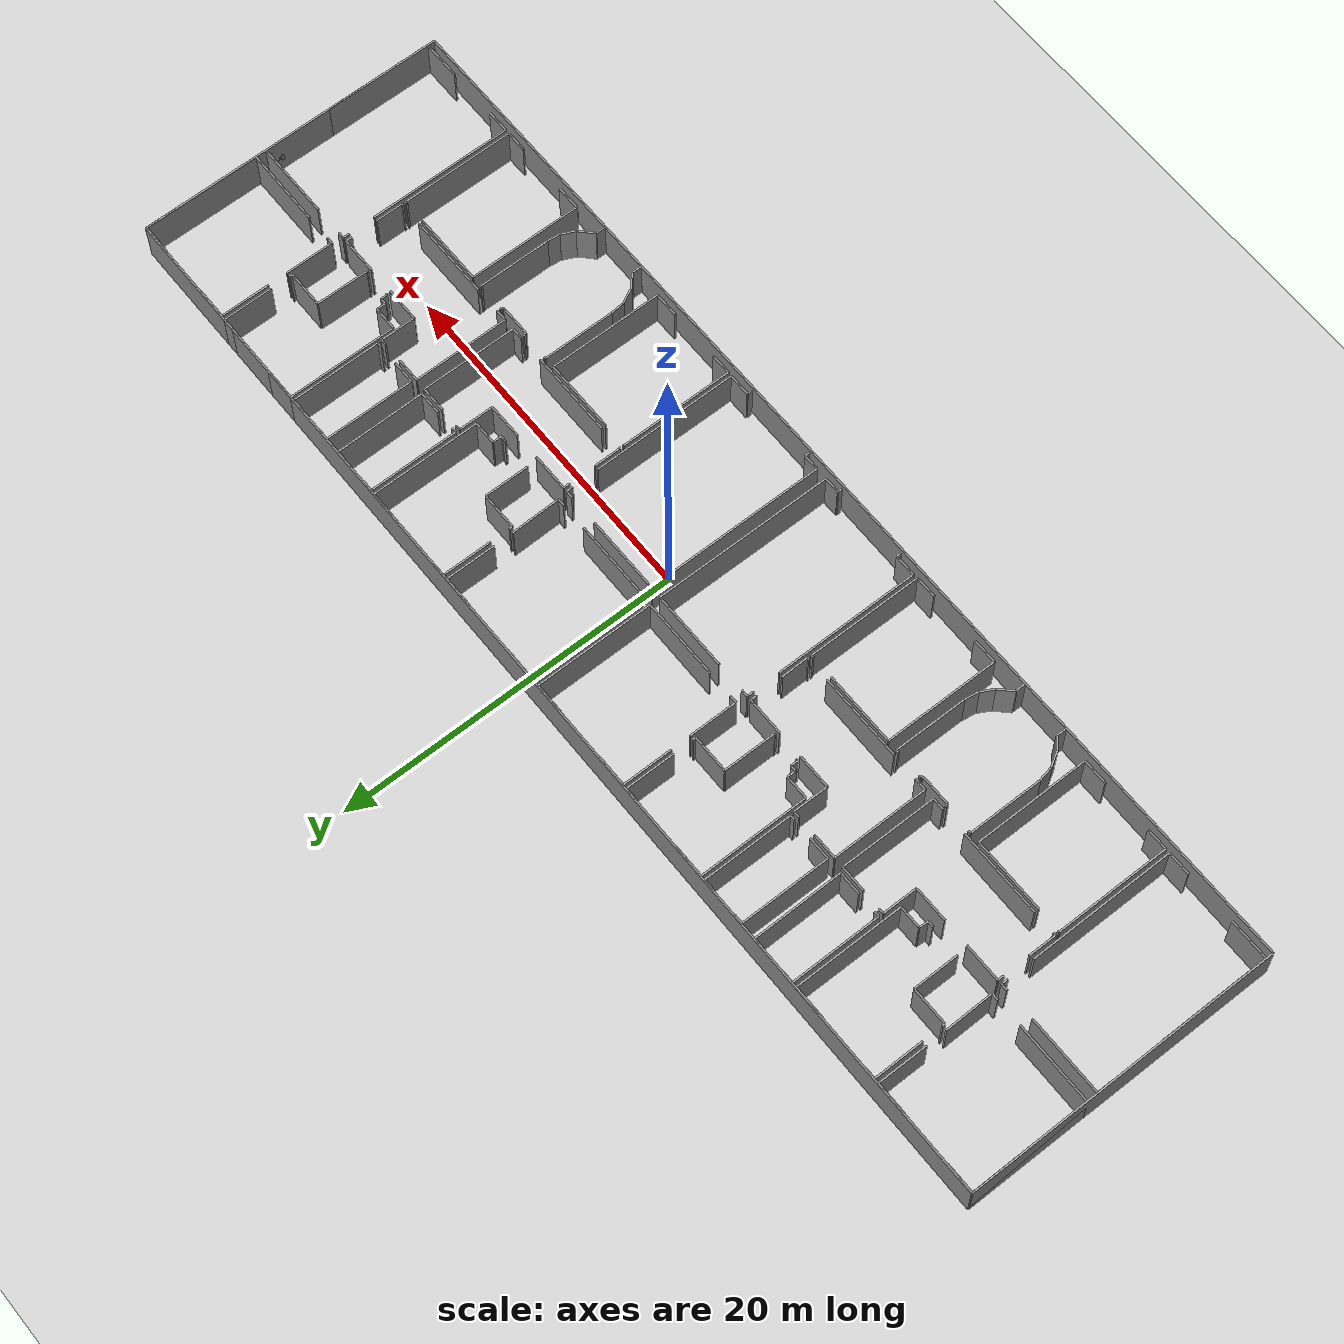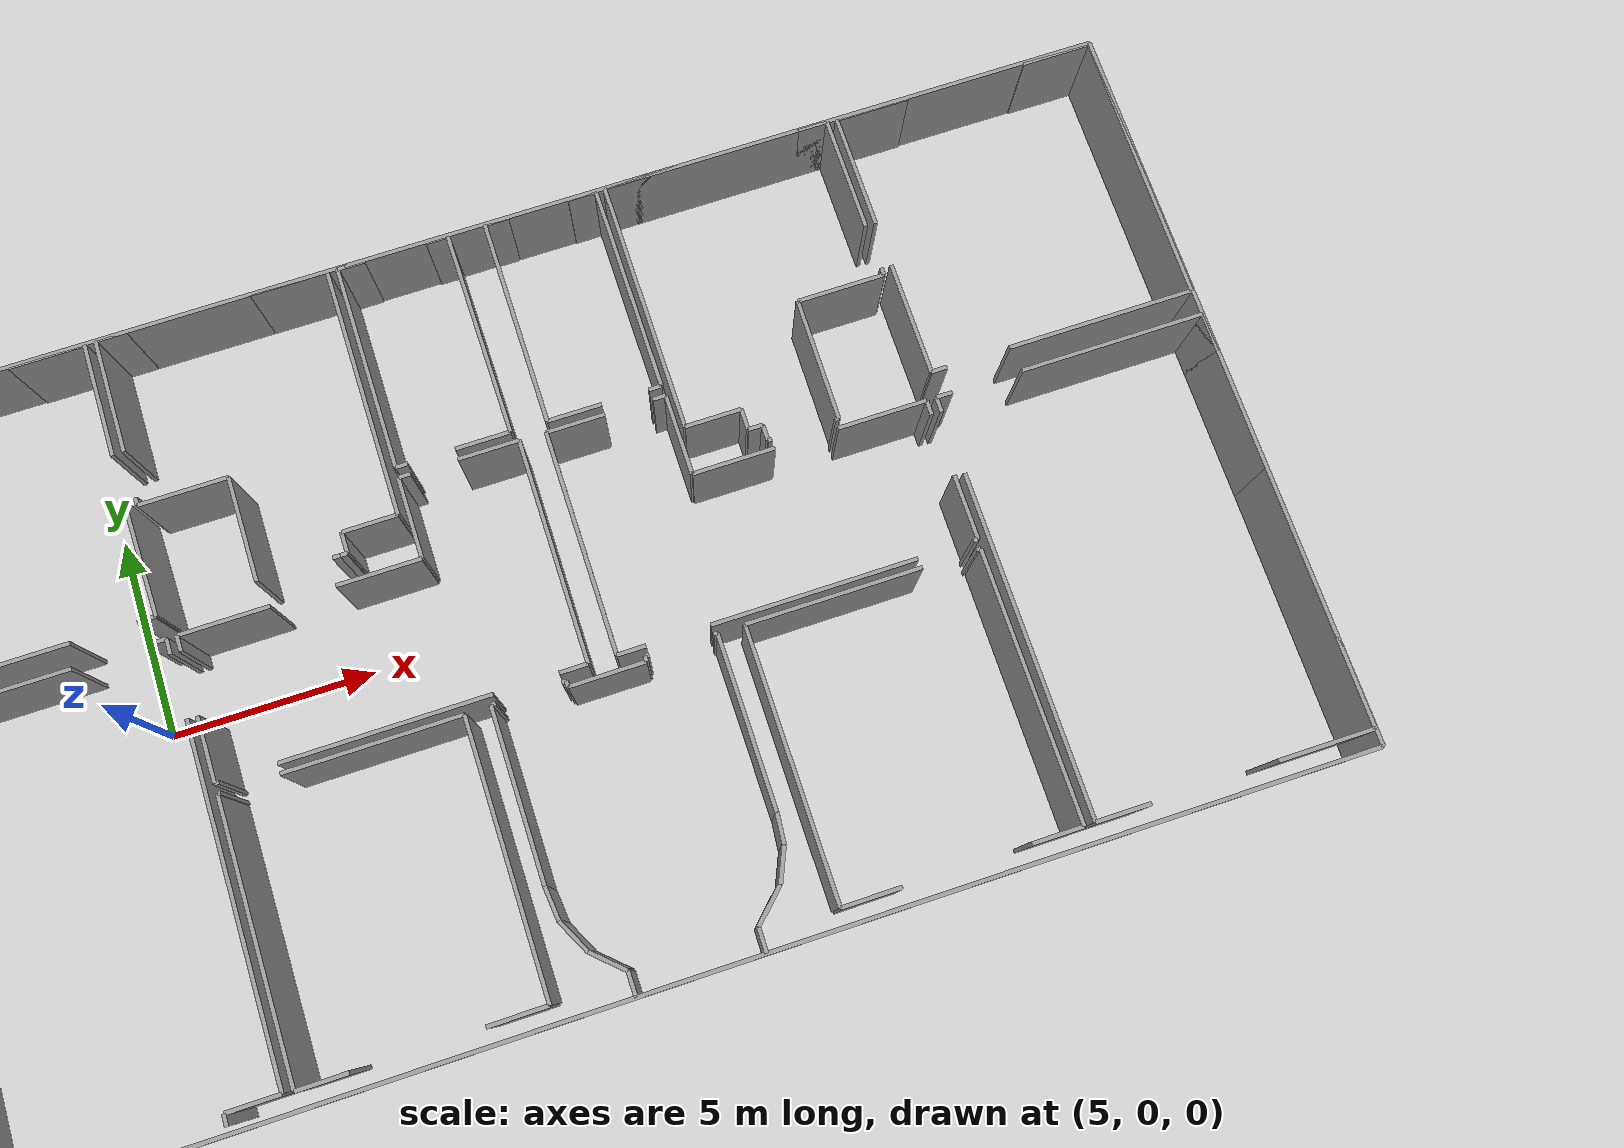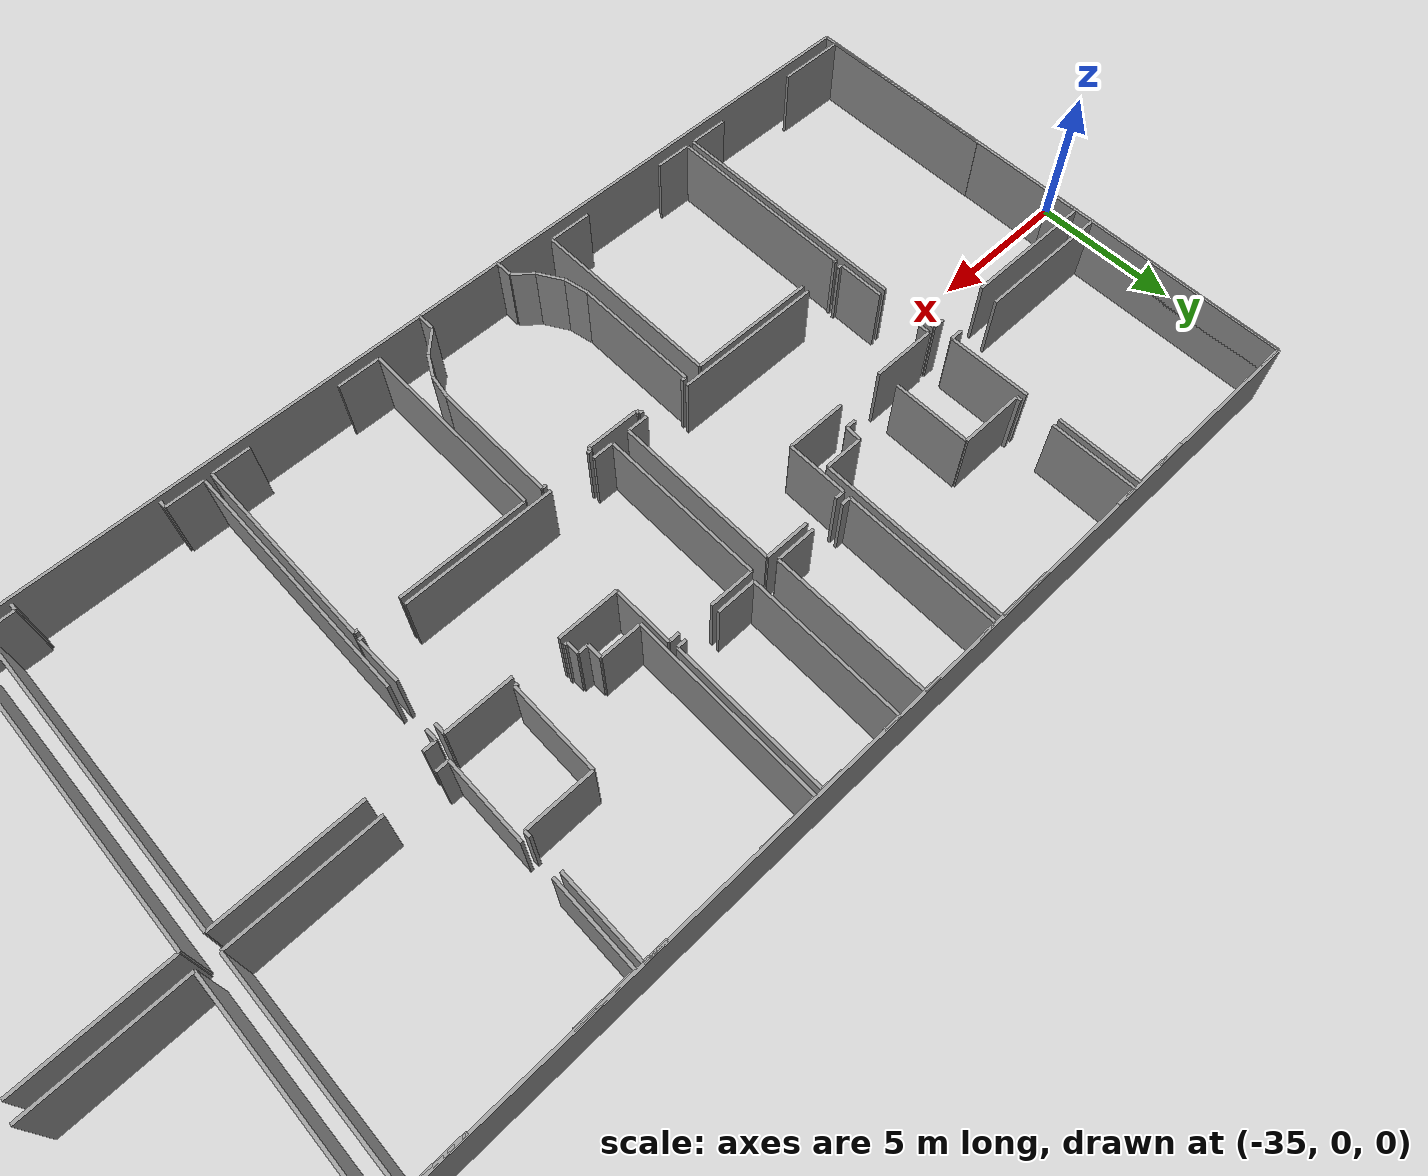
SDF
<sdf version="1.6">
  <world name="default">
    <light name="sun" type="directional">
      <cast_shadows>1</cast_shadows>
      <pose frame="">0 0 10 0 -0 0</pose>
      <diffuse>0.8 0.8 0.8 1</diffuse>
      <specular>0.1 0.1 0.1 1</specular>
      <attenuation>
        <range>1000</range>
        <constant>0.9</constant>
        <linear>0.01</linear>
        <quadratic>0.001</quadratic>
      </attenuation>
      <direction>-0.5 0.5 -1</direction>
    </light>
    <model name="ground_plane">
      <static>1</static>
      <link name="link">
        <collision name="collision">
          <geometry>
            <plane>
              <normal>0 0 1</normal>
              <size>100 100</size>
            </plane>
          </geometry>
          <surface>
            <friction>
              <ode>
                <mu>100</mu>
                <mu2>50</mu2>
              </ode>
              <torsional>
                <ode />
              </torsional>
            </friction>
            <contact>
              <ode />
            </contact>
            <bounce />
          </surface>
          <max_contacts>10</max_contacts>
        </collision>
        <visual name="visual">
          <cast_shadows>0</cast_shadows>
          <geometry>
            <plane>
              <normal>0 0 1</normal>
              <size>100 100</size>
            </plane>
          </geometry>
          <material>
            <script>
              <uri>file://media/materials/scripts/gazebo.material</uri>
              <name>Gazebo/Grey</name>
            </script>
          </material>
        </visual>
        <self_collide>0</self_collide>
        <kinematic>0</kinematic>
        <gravity>1</gravity>
      </link>
    </model>
    <gravity>0 0 -9.8</gravity>
    <magnetic_field>6e-06 2.3e-05 -4.2e-05</magnetic_field>
    <atmosphere type="adiabatic" />
    <physics default="0" name="default_physics" type="ode">
      <max_step_size>0.001</max_step_size>
      <real_time_factor>1</real_time_factor>
      <real_time_update_rate>1000</real_time_update_rate>
    </physics>
    <scene>
      <ambient>0.4 0.4 0.4 1</ambient>
      <background>0.7 0.7 0.7 1</background>
      <shadows>1</shadows>
    </scene>
    <spherical_coordinates>
      <surface_model>EARTH_WGS84</surface_model>
      <latitude_deg>0</latitude_deg>
      <longitude_deg>0</longitude_deg>
      <elevation>0</elevation>
      <heading_deg>0</heading_deg>
    </spherical_coordinates>
  <model name="0510034870_A-40">
		<static>1</static>
		<link name="Wall_0">
			<collision name="Wall_0_Collision">
				<geometry>
					<box>
						<size>0.423984310042 0.1 2.5</size>
					</box>
				</geometry>
				<pose frame="">0.211992155021 0 1.25 0 0 0</pose>
			</collision>
			<visual name="Wall_0_Visual">
				<pose frame="">0.211992155021 0 1.25 0 0 0</pose>
				<geometry>
					<box>
						<size>0.423984310042 0.1 2.5</size>
					</box>
				</geometry>
				<material>
					<script>
						<uri>file://media/materials/scripts/gazebo.material</uri>
						<name>Gazebo/Grey</name>
					</script>
					<ambient>1 1 1 1</ambient>
				</material>
			</visual>
			<pose frame="">6.64944494868 -6.91932238675 0 0 0 3.14159265359</pose>
		</link>
		<link name="Wall_1">
			<collision name="Wall_1_Collision">
				<geometry>
					<box>
						<size>4.67449048891 0.1 2.5</size>
					</box>
				</geometry>
				<pose frame="">2.33724524446 0 1.25 0 0 0</pose>
			</collision>
			<visual name="Wall_1_Visual">
				<pose frame="">2.33724524446 0 1.25 0 0 0</pose>
				<geometry>
					<box>
						<size>4.67449048891 0.1 2.5</size>
					</box>
				</geometry>
				<material>
					<script>
						<uri>file://media/materials/scripts/gazebo.material</uri>
						<name>Gazebo/Grey</name>
					</script>
					<ambient>1 1 1 1</ambient>
				</material>
			</visual>
			<pose frame="">4.67449048891 -6.91932238675 0 0 0 3.14159265359</pose>
		</link>
		<link name="Wall_2">
			<collision name="Wall_2_Collision">
				<geometry>
					<box>
						<size>6.8962190501 0.1 2.5</size>
					</box>
				</geometry>
				<pose frame="">3.44810952505 0 1.25 0 0 0</pose>
			</collision>
			<visual name="Wall_2_Visual">
				<pose frame="">3.44810952505 0 1.25 0 0 0</pose>
				<geometry>
					<box>
						<size>6.8962190501 0.1 2.5</size>
					</box>
				</geometry>
				<material>
					<script>
						<uri>file://media/materials/scripts/gazebo.material</uri>
						<name>Gazebo/Grey</name>
					</script>
					<ambient>1 1 1 1</ambient>
				</material>
			</visual>
			<pose frame="">0.0 -6.91932238675 0 0 0 1.57079632679</pose>
		</link>
		<link name="Wall_3">
			<collision name="Wall_3_Collision">
				<geometry>
					<box>
						<size>1.73833567117 0.1 2.5</size>
					</box>
				</geometry>
				<pose frame="">0.869167835585 0 1.25 0 0 0</pose>
			</collision>
			<visual name="Wall_3_Visual">
				<pose frame="">0.869167835585 0 1.25 0 0 0</pose>
				<geometry>
					<box>
						<size>1.73833567117 0.1 2.5</size>
					</box>
				</geometry>
				<material>
					<script>
						<uri>file://media/materials/scripts/gazebo.material</uri>
						<name>Gazebo/Grey</name>
					</script>
					<ambient>1 1 1 1</ambient>
				</material>
			</visual>
			<pose frame="">0.0 -0.023103336655 0 0 0 0.0</pose>
		</link>
		<link name="Wall_4">
			<collision name="Wall_4_Collision">
				<geometry>
					<box>
						<size>1.85804142098 0.1 2.5</size>
					</box>
				</geometry>
				<pose frame="">0.929020710491 0 1.25 0 0 0</pose>
			</collision>
			<visual name="Wall_4_Visual">
				<pose frame="">0.929020710491 0 1.25 0 0 0</pose>
				<geometry>
					<box>
						<size>1.85804142098 0.1 2.5</size>
					</box>
				</geometry>
				<material>
					<script>
						<uri>file://media/materials/scripts/gazebo.material</uri>
						<name>Gazebo/Grey</name>
					</script>
					<ambient>1 1 1 1</ambient>
				</material>
			</visual>
			<pose frame="">4.75040145221 -0.023103336655 0 0 0 0.0</pose>
		</link>
		<link name="Wall_5">
			<collision name="Wall_5_Collision">
				<geometry>
					<box>
						<size>2.88918649597 0.1 2.5</size>
					</box>
				</geometry>
				<pose frame="">1.44459324799 0 1.25 0 0 0</pose>
			</collision>
			<visual name="Wall_5_Visual">
				<pose frame="">1.44459324799 0 1.25 0 0 0</pose>
				<geometry>
					<box>
						<size>2.88918649597 0.1 2.5</size>
					</box>
				</geometry>
				<material>
					<script>
						<uri>file://media/materials/scripts/gazebo.material</uri>
						<name>Gazebo/Grey</name>
					</script>
					<ambient>1 1 1 1</ambient>
				</material>
			</visual>
			<pose frame="">6.60844287319 -0.023103336655 0 0 0 -1.57079632679</pose>
		</link>
		<link name="Wall_6">
			<collision name="Wall_6_Collision">
				<geometry>
					<box>
						<size>2.83350200904 0.1 2.5</size>
					</box>
				</geometry>
				<pose frame="">1.41675100452 0 1.25 0 0 0</pose>
			</collision>
			<visual name="Wall_6_Visual">
				<pose frame="">1.41675100452 0 1.25 0 0 0</pose>
				<geometry>
					<box>
						<size>2.83350200904 0.1 2.5</size>
					</box>
				</geometry>
				<material>
					<script>
						<uri>file://media/materials/scripts/gazebo.material</uri>
						<name>Gazebo/Grey</name>
					</script>
					<ambient>1 1 1 1</ambient>
				</material>
			</visual>
			<pose frame="">6.60844287319 -4.08611705267 0 0 0 -1.55632536244</pose>
		</link>
		<link name="Wall_7">
			<collision name="Wall_7_Collision">
				<geometry>
					<box>
						<size>0.341980159058 0.1 2.5</size>
					</box>
				</geometry>
				<pose frame="">0.170990079529 0 1.25 0 0 0</pose>
			</collision>
			<visual name="Wall_7_Visual">
				<pose frame="">0.170990079529 0 1.25 0 0 0</pose>
				<geometry>
					<box>
						<size>0.341980159058 0.1 2.5</size>
					</box>
				</geometry>
				<material>
					<script>
						<uri>file://media/materials/scripts/gazebo.material</uri>
						<name>Gazebo/Grey</name>
					</script>
					<ambient>1 1 1 1</ambient>
				</material>
			</visual>
			<pose frame="">11.1978826173 -6.90066199945 0 0 0 3.14159265359</pose>
		</link>
		<link name="Wall_8">
			<collision name="Wall_8_Collision">
				<geometry>
					<box>
						<size>2.6478708752 0.1 2.5</size>
					</box>
				</geometry>
				<pose frame="">1.3239354376 0 1.25 0 0 0</pose>
			</collision>
			<visual name="Wall_8_Visual">
				<pose frame="">1.3239354376 0 1.25 0 0 0</pose>
				<geometry>
					<box>
						<size>2.6478708752 0.1 2.5</size>
					</box>
				</geometry>
				<material>
					<script>
						<uri>file://media/materials/scripts/gazebo.material</uri>
						<name>Gazebo/Grey</name>
					</script>
					<ambient>1 1 1 1</ambient>
				</material>
			</visual>
			<pose frame="">9.07643777015 -6.90066199945 0 0 0 1.57079632679</pose>
		</link>
		<link name="Wall_9">
			<collision name="Wall_9_Collision">
				<geometry>
					<box>
						<size>2.19532474786 0.1 2.5</size>
					</box>
				</geometry>
				<pose frame="">1.09766237393 0 1.25 0 0 0</pose>
			</collision>
			<visual name="Wall_9_Visual">
				<pose frame="">1.09766237393 0 1.25 0 0 0</pose>
				<geometry>
					<box>
						<size>2.19532474786 0.1 2.5</size>
					</box>
				</geometry>
				<material>
					<script>
						<uri>file://media/materials/scripts/gazebo.material</uri>
						<name>Gazebo/Grey</name>
					</script>
					<ambient>1 1 1 1</ambient>
				</material>
			</visual>
			<pose frame="">9.07643777015 -4.25279112426 0 0 0 3.14159265359</pose>
		</link>
		<link name="Wall_10">
			<collision name="Wall_10_Collision">
				<geometry>
					<box>
						<size>0.173275024912 0.1 2.5</size>
					</box>
				</geometry>
				<pose frame="">0.0866375124561 0 1.25 0 0 0</pose>
			</collision>
			<visual name="Wall_10_Visual">
				<pose frame="">0.0866375124561 0 1.25 0 0 0</pose>
				<geometry>
					<box>
						<size>0.173275024912 0.1 2.5</size>
					</box>
				</geometry>
				<material>
					<script>
						<uri>file://media/materials/scripts/gazebo.material</uri>
						<name>Gazebo/Grey</name>
					</script>
					<ambient>1 1 1 1</ambient>
				</material>
			</visual>
			<pose frame="">6.88111302228 -4.25279112426 0 0 0 1.57079632679</pose>
		</link>
		<link name="Wall_11">
			<collision name="Wall_11_Collision">
				<geometry>
					<box>
						<size>2.89629521494 0.1 2.5</size>
					</box>
				</geometry>
				<pose frame="">1.44814760747 0 1.25 0 0 0</pose>
			</collision>
			<visual name="Wall_11_Visual">
				<pose frame="">1.44814760747 0 1.25 0 0 0</pose>
				<geometry>
					<box>
						<size>2.89629521494 0.1 2.5</size>
					</box>
				</geometry>
				<material>
					<script>
						<uri>file://media/materials/scripts/gazebo.material</uri>
						<name>Gazebo/Grey</name>
					</script>
					<ambient>1 1 1 1</ambient>
				</material>
			</visual>
			<pose frame="">6.88111302228 -2.91724054763 0 0 0 1.57079632679</pose>
		</link>
		<link name="Wall_12">
			<collision name="Wall_12_Collision">
				<geometry>
					<box>
						<size>0.745273019238 0.1 2.5</size>
					</box>
				</geometry>
				<pose frame="">0.372636509619 0 1.25 0 0 0</pose>
			</collision>
			<visual name="Wall_12_Visual">
				<pose frame="">0.372636509619 0 1.25 0 0 0</pose>
				<geometry>
					<box>
						<size>0.745273019238 0.1 2.5</size>
					</box>
				</geometry>
				<material>
					<script>
						<uri>file://media/materials/scripts/gazebo.material</uri>
						<name>Gazebo/Grey</name>
					</script>
					<ambient>1 1 1 1</ambient>
				</material>
			</visual>
			<pose frame="">6.88111302228 -0.0209453326817 0 0 0 0.0</pose>
		</link>
		<link name="Wall_13">
			<collision name="Wall_13_Collision">
				<geometry>
					<box>
						<size>1.89333113302 0.1 2.5</size>
					</box>
				</geometry>
				<pose frame="">0.946665566508 0 1.25 0 0 0</pose>
			</collision>
			<visual name="Wall_13_Visual">
				<pose frame="">0.946665566508 0 1.25 0 0 0</pose>
				<geometry>
					<box>
						<size>1.89333113302 0.1 2.5</size>
					</box>
				</geometry>
				<material>
					<script>
						<uri>file://media/materials/scripts/gazebo.material</uri>
						<name>Gazebo/Grey</name>
					</script>
					<ambient>1 1 1 1</ambient>
				</material>
			</visual>
			<pose frame="">10.6502573737 -0.0209453326817 0 0 0 0.0</pose>
		</link>
		<link name="Wall_14">
			<collision name="Wall_14_Collision">
				<geometry>
					<box>
						<size>6.34960933781 0.1 2.5</size>
					</box>
				</geometry>
				<pose frame="">3.17480466891 0 1.25 0 0 0</pose>
			</collision>
			<visual name="Wall_14_Visual">
				<pose frame="">3.17480466891 0 1.25 0 0 0</pose>
				<geometry>
					<box>
						<size>6.34960933781 0.1 2.5</size>
					</box>
				</geometry>
				<material>
					<script>
						<uri>file://media/materials/scripts/gazebo.material</uri>
						<name>Gazebo/Grey</name>
					</script>
					<ambient>1 1 1 1</ambient>
				</material>
			</visual>
			<pose frame="">12.5435885067 -0.0209453326817 0 0 0 -1.57079632679</pose>
		</link>
		<link name="Wall_15">
			<collision name="Wall_15_Collision">
				<geometry>
					<box>
						<size>1.3077504078 0.1 2.5</size>
					</box>
				</geometry>
				<pose frame="">0.6538752039 0 1.25 0 0 0</pose>
			</collision>
			<visual name="Wall_15_Visual">
				<pose frame="">0.6538752039 0 1.25 0 0 0</pose>
				<geometry>
					<box>
						<size>1.3077504078 0.1 2.5</size>
					</box>
				</geometry>
				<material>
					<script>
						<uri>file://media/materials/scripts/gazebo.material</uri>
						<name>Gazebo/Grey</name>
					</script>
					<ambient>1 1 1 1</ambient>
				</material>
			</visual>
			<pose frame="">12.5435885067 -6.37055467049 0 0 0 3.14159265359</pose>
		</link>
		<link name="Wall_16">
			<collision name="Wall_16_Collision">
				<geometry>
					<box>
						<size>0.531464390911 0.1 2.5</size>
					</box>
				</geometry>
				<pose frame="">0.265732195456 0 1.25 0 0 0</pose>
			</collision>
			<visual name="Wall_16_Visual">
				<pose frame="">0.265732195456 0 1.25 0 0 0</pose>
				<geometry>
					<box>
						<size>0.531464390911 0.1 2.5</size>
					</box>
				</geometry>
				<material>
					<script>
						<uri>file://media/materials/scripts/gazebo.material</uri>
						<name>Gazebo/Grey</name>
					</script>
					<ambient>1 1 1 1</ambient>
				</material>
			</visual>
			<pose frame="">11.2358380989 -6.37055467049 0 0 0 -1.64227396669</pose>
		</link>
		<link name="Wall_17">
			<collision name="Wall_17_Collision">
				<geometry>
					<box>
						<size>1.35560731944 0.1 2.5</size>
					</box>
				</geometry>
				<pose frame="">0.677803659721 0 1.25 0 0 0</pose>
			</collision>
			<visual name="Wall_17_Visual">
				<pose frame="">0.677803659721 0 1.25 0 0 0</pose>
				<geometry>
					<box>
						<size>1.35560731944 0.1 2.5</size>
					</box>
				</geometry>
				<material>
					<script>
						<uri>file://media/materials/scripts/gazebo.material</uri>
						<name>Gazebo/Grey</name>
					</script>
					<ambient>1 1 1 1</ambient>
				</material>
			</visual>
			<pose frame="">6.73728840454 -18.0051157388 0 0 0 3.14159265359</pose>
		</link>
		<link name="Wall_18">
			<collision name="Wall_18_Collision">
				<geometry>
					<box>
						<size>2.34333843215 0.1 2.5</size>
					</box>
				</geometry>
				<pose frame="">1.17166921607 0 1.25 0 0 0</pose>
			</collision>
			<visual name="Wall_18_Visual">
				<pose frame="">1.17166921607 0 1.25 0 0 0</pose>
				<geometry>
					<box>
						<size>2.34333843215 0.1 2.5</size>
					</box>
				</geometry>
				<material>
					<script>
						<uri>file://media/materials/scripts/gazebo.material</uri>
						<name>Gazebo/Grey</name>
					</script>
					<ambient>1 1 1 1</ambient>
				</material>
			</visual>
			<pose frame="">2.35780975291 -18.0051157388 0 0 0 3.14159265359</pose>
		</link>
		<link name="Wall_19">
			<collision name="Wall_19_Collision">
				<geometry>
					<box>
						<size>6.41523804688 0.1 2.5</size>
					</box>
				</geometry>
				<pose frame="">3.20761902344 0 1.25 0 0 0</pose>
			</collision>
			<visual name="Wall_19_Visual">
				<pose frame="">3.20761902344 0 1.25 0 0 0</pose>
				<geometry>
					<box>
						<size>6.41523804688 0.1 2.5</size>
					</box>
				</geometry>
				<material>
					<script>
						<uri>file://media/materials/scripts/gazebo.material</uri>
						<name>Gazebo/Grey</name>
					</script>
					<ambient>1 1 1 1</ambient>
				</material>
			</visual>
			<pose frame="">0.0144713207619 -18.0051157388 0 0 0 1.57079632679</pose>
		</link>
		<link name="Wall_20">
			<collision name="Wall_20_Collision">
				<geometry>
					<box>
						<size>0.971990377841 0.1 2.5</size>
					</box>
				</geometry>
				<pose frame="">0.485995188921 0 1.25 0 0 0</pose>
			</collision>
			<visual name="Wall_20_Visual">
				<pose frame="">0.485995188921 0 1.25 0 0 0</pose>
				<geometry>
					<box>
						<size>0.971990377841 0.1 2.5</size>
					</box>
				</geometry>
				<material>
					<script>
						<uri>file://media/materials/scripts/gazebo.material</uri>
						<name>Gazebo/Grey</name>
					</script>
					<ambient>1 1 1 1</ambient>
				</material>
			</visual>
			<pose frame="">0.0144713207619 -8.5352865385 0 0 0 1.57079632679</pose>
		</link>
		<link name="Wall_21">
			<collision name="Wall_21_Collision">
				<geometry>
					<box>
						<size>4.54399471924 0.1 2.5</size>
					</box>
				</geometry>
				<pose frame="">2.27199735962 0 1.25 0 0 0</pose>
			</collision>
			<visual name="Wall_21_Visual">
				<pose frame="">2.27199735962 0 1.25 0 0 0</pose>
				<geometry>
					<box>
						<size>4.54399471924 0.1 2.5</size>
					</box>
				</geometry>
				<material>
					<script>
						<uri>file://media/materials/scripts/gazebo.material</uri>
						<name>Gazebo/Grey</name>
					</script>
					<ambient>1 1 1 1</ambient>
				</material>
			</visual>
			<pose frame="">0.0144713207619 -7.56329616066 0 0 0 0.0</pose>
		</link>
		<link name="Wall_22">
			<collision name="Wall_22_Collision">
				<geometry>
					<box>
						<size>0.392248957494 0.1 2.5</size>
					</box>
				</geometry>
				<pose frame="">0.196124478747 0 1.25 0 0 0</pose>
			</collision>
			<visual name="Wall_22_Visual">
				<pose frame="">0.196124478747 0 1.25 0 0 0</pose>
				<geometry>
					<box>
						<size>0.392248957494 0.1 2.5</size>
					</box>
				</geometry>
				<material>
					<script>
						<uri>file://media/materials/scripts/gazebo.material</uri>
						<name>Gazebo/Grey</name>
					</script>
					<ambient>1 1 1 1</ambient>
				</material>
			</visual>
			<pose frame="">6.33044118487 -7.56329616066 0 0 0 0.0</pose>
		</link>
		<link name="Wall_23">
			<collision name="Wall_23_Collision">
				<geometry>
					<box>
						<size>0.37028809353 0.1 2.5</size>
					</box>
				</geometry>
				<pose frame="">0.185144046765 0 1.25 0 0 0</pose>
			</collision>
			<visual name="Wall_23_Visual">
				<pose frame="">0.185144046765 0 1.25 0 0 0</pose>
				<geometry>
					<box>
						<size>0.37028809353 0.1 2.5</size>
					</box>
				</geometry>
				<material>
					<script>
						<uri>file://media/materials/scripts/gazebo.material</uri>
						<name>Gazebo/Grey</name>
					</script>
					<ambient>1 1 1 1</ambient>
				</material>
			</visual>
			<pose frame="">6.72269014236 -7.56329616066 0 0 0 -1.57079632679</pose>
		</link>
		<link name="Wall_24">
			<collision name="Wall_24_Collision">
				<geometry>
					<box>
						<size>8.48896547592 0.1 2.5</size>
					</box>
				</geometry>
				<pose frame="">4.24448273796 0 1.25 0 0 0</pose>
			</collision>
			<visual name="Wall_24_Visual">
				<pose frame="">4.24448273796 0 1.25 0 0 0</pose>
				<geometry>
					<box>
						<size>8.48896547592 0.1 2.5</size>
					</box>
				</geometry>
				<material>
					<script>
						<uri>file://media/materials/scripts/gazebo.material</uri>
						<name>Gazebo/Grey</name>
					</script>
					<ambient>1 1 1 1</ambient>
				</material>
			</visual>
			<pose frame="">6.72269014236 -9.51616281505 0 0 0 -1.56907665089</pose>
		</link>
		<link name="Wall_25">
			<collision name="Wall_25_Collision">
				<geometry>
					<box>
						<size>1.48242178822 0.1 2.5</size>
					</box>
				</geometry>
				<pose frame="">0.741210894112 0 1.25 0 0 0</pose>
			</collision>
			<visual name="Wall_25_Visual">
				<pose frame="">0.741210894112 0 1.25 0 0 0</pose>
				<geometry>
					<box>
						<size>1.48242178822 0.1 2.5</size>
					</box>
				</geometry>
				<material>
					<script>
						<uri>file://media/materials/scripts/gazebo.material</uri>
						<name>Gazebo/Grey</name>
					</script>
					<ambient>1 1 1 1</ambient>
				</material>
			</visual>
			<pose frame="">12.7630702049 -18.0068929186 0 0 0 3.14159265359</pose>
		</link>
		<link name="Wall_26">
			<collision name="Wall_26_Collision">
				<geometry>
					<box>
						<size>1.25024594898 0.1 2.5</size>
					</box>
				</geometry>
				<pose frame="">0.625122974491 0 1.25 0 0 0</pose>
			</collision>
			<visual name="Wall_26_Visual">
				<pose frame="">0.625122974491 0 1.25 0 0 0</pose>
				<geometry>
					<box>
						<size>1.25024594898 0.1 2.5</size>
					</box>
				</geometry>
				<material>
					<script>
						<uri>file://media/materials/scripts/gazebo.material</uri>
						<name>Gazebo/Grey</name>
					</script>
					<ambient>1 1 1 1</ambient>
				</material>
			</visual>
			<pose frame="">8.24547929903 -18.0068929186 0 0 0 3.14159265359</pose>
		</link>
		<link name="Wall_27">
			<collision name="Wall_27_Collision">
				<geometry>
					<box>
						<size>6.67064416419 0.1 2.5</size>
					</box>
				</geometry>
				<pose frame="">3.33532208209 0 1.25 0 0 0</pose>
			</collision>
			<visual name="Wall_27_Visual">
				<pose frame="">3.33532208209 0 1.25 0 0 0</pose>
				<geometry>
					<box>
						<size>6.67064416419 0.1 2.5</size>
					</box>
				</geometry>
				<material>
					<script>
						<uri>file://media/materials/scripts/gazebo.material</uri>
						<name>Gazebo/Grey</name>
					</script>
					<ambient>1 1 1 1</ambient>
				</material>
			</visual>
			<pose frame="">6.99523335005 -18.0068929186 0 0 0 1.57079632679</pose>
		</link>
		<link name="Wall_28">
			<collision name="Wall_28_Collision">
				<geometry>
					<box>
						<size>0.0954599404645 0.1 2.5</size>
					</box>
				</geometry>
				<pose frame="">0.0477299702322 0 1.25 0 0 0</pose>
			</collision>
			<visual name="Wall_28_Visual">
				<pose frame="">0.0477299702322 0 1.25 0 0 0</pose>
				<geometry>
					<box>
						<size>0.0954599404645 0.1 2.5</size>
					</box>
				</geometry>
				<material>
					<script>
						<uri>file://media/materials/scripts/gazebo.material</uri>
						<name>Gazebo/Grey</name>
					</script>
					<ambient>1 1 1 1</ambient>
				</material>
			</visual>
			<pose frame="">6.99523335005 -11.3362487544 0 0 0 0.0</pose>
		</link>
		<link name="Wall_29">
			<collision name="Wall_29_Collision">
				<geometry>
					<box>
						<size>4.32019701307 0.1 2.5</size>
					</box>
				</geometry>
				<pose frame="">2.16009850653 0 1.25 0 0 0</pose>
			</collision>
			<visual name="Wall_29_Visual">
				<pose frame="">2.16009850653 0 1.25 0 0 0</pose>
				<geometry>
					<box>
						<size>4.32019701307 0.1 2.5</size>
					</box>
				</geometry>
				<material>
					<script>
						<uri>file://media/materials/scripts/gazebo.material</uri>
						<name>Gazebo/Grey</name>
					</script>
					<ambient>1 1 1 1</ambient>
				</material>
			</visual>
			<pose frame="">8.43741471124 -11.3362487544 0 0 0 0.0</pose>
		</link>
		<link name="Wall_30">
			<collision name="Wall_30_Collision">
				<geometry>
					<box>
						<size>6.67064639748 0.1 2.5</size>
					</box>
				</geometry>
				<pose frame="">3.33532319874 0 1.25 0 0 0</pose>
			</collision>
			<visual name="Wall_30_Visual">
				<pose frame="">3.33532319874 0 1.25 0 0 0</pose>
				<geometry>
					<box>
						<size>6.67064639748 0.1 2.5</size>
					</box>
				</geometry>
				<material>
					<script>
						<uri>file://media/materials/scripts/gazebo.material</uri>
						<name>Gazebo/Grey</name>
					</script>
					<ambient>1 1 1 1</ambient>
				</material>
			</visual>
			<pose frame="">12.7576117243 -11.3362487544 0 0 0 -1.56997804309</pose>
		</link>
		<link name="Wall_31">
			<collision name="Wall_31_Collision">
				<geometry>
					<box>
						<size>0.70706365477 0.1 2.5</size>
					</box>
				</geometry>
				<pose frame="">0.353531827385 0 1.25 0 0 0</pose>
			</collision>
			<visual name="Wall_31_Visual">
				<pose frame="">0.353531827385 0 1.25 0 0 0</pose>
				<geometry>
					<box>
						<size>0.70706365477 0.1 2.5</size>
					</box>
				</geometry>
				<material>
					<script>
						<uri>file://media/materials/scripts/gazebo.material</uri>
						<name>Gazebo/Grey</name>
					</script>
					<ambient>1 1 1 1</ambient>
				</material>
			</visual>
			<pose frame="">15.780086701 -11.0998838486 0 0 0 3.14159265359</pose>
		</link>
		<link name="Wall_32">
			<collision name="Wall_32_Collision">
				<geometry>
					<box>
						<size>5.05886907898 0.1 2.5</size>
					</box>
				</geometry>
				<pose frame="">2.52943453949 0 1.25 0 0 0</pose>
			</collision>
			<visual name="Wall_32_Visual">
				<pose frame="">2.52943453949 0 1.25 0 0 0</pose>
				<geometry>
					<box>
						<size>5.05886907898 0.1 2.5</size>
					</box>
				</geometry>
				<material>
					<script>
						<uri>file://media/materials/scripts/gazebo.material</uri>
						<name>Gazebo/Grey</name>
					</script>
					<ambient>1 1 1 1</ambient>
				</material>
			</visual>
			<pose frame="">13.510755111 -11.0998838486 0 0 0 3.14159265359</pose>
		</link>
		<link name="Wall_33">
			<collision name="Wall_33_Collision">
				<geometry>
					<box>
						<size>0.154487696204 0.1 2.5</size>
					</box>
				</geometry>
				<pose frame="">0.0772438481019 0 1.25 0 0 0</pose>
			</collision>
			<visual name="Wall_33_Visual">
				<pose frame="">0.0772438481019 0 1.25 0 0 0</pose>
				<geometry>
					<box>
						<size>0.154487696204 0.1 2.5</size>
					</box>
				</geometry>
				<material>
					<script>
						<uri>file://media/materials/scripts/gazebo.material</uri>
						<name>Gazebo/Grey</name>
					</script>
					<ambient>1 1 1 1</ambient>
				</material>
			</visual>
			<pose frame="">7.13220313164 -11.0998838486 0 0 0 3.14159265359</pose>
		</link>
		<link name="Wall_34">
			<collision name="Wall_34_Collision">
				<geometry>
					<box>
						<size>1.61380614777 0.1 2.5</size>
					</box>
				</geometry>
				<pose frame="">0.806903073886 0 1.25 0 0 0</pose>
			</collision>
			<visual name="Wall_34_Visual">
				<pose frame="">0.806903073886 0 1.25 0 0 0</pose>
				<geometry>
					<box>
						<size>1.61380614777 0.1 2.5</size>
					</box>
				</geometry>
				<material>
					<script>
						<uri>file://media/materials/scripts/gazebo.material</uri>
						<name>Gazebo/Grey</name>
					</script>
					<ambient>1 1 1 1</ambient>
				</material>
			</visual>
			<pose frame="">6.97771543544 -11.0998838486 0 0 0 1.57079632679</pose>
		</link>
		<link name="Wall_35">
			<collision name="Wall_35_Collision">
				<geometry>
					<box>
						<size>0.367241499686 0.1 2.5</size>
					</box>
				</geometry>
				<pose frame="">0.183620749843 0 1.25 0 0 0</pose>
			</collision>
			<visual name="Wall_35_Visual">
				<pose frame="">0.183620749843 0 1.25 0 0 0</pose>
				<geometry>
					<box>
						<size>0.367241499686 0.1 2.5</size>
					</box>
				</geometry>
				<material>
					<script>
						<uri>file://media/materials/scripts/gazebo.material</uri>
						<name>Gazebo/Grey</name>
					</script>
					<ambient>1 1 1 1</ambient>
				</material>
			</visual>
			<pose frame="">6.97771543544 -7.90857679638 0 0 0 1.57079632679</pose>
		</link>
		<link name="Wall_36">
			<collision name="Wall_36_Collision">
				<geometry>
					<box>
						<size>2.19887910735 0.1 2.5</size>
					</box>
				</geometry>
				<pose frame="">1.09943955367 0 1.25 0 0 0</pose>
			</collision>
			<visual name="Wall_36_Visual">
				<pose frame="">1.09943955367 0 1.25 0 0 0</pose>
				<geometry>
					<box>
						<size>2.19887910735 0.1 2.5</size>
					</box>
				</geometry>
				<material>
					<script>
						<uri>file://media/materials/scripts/gazebo.material</uri>
						<name>Gazebo/Grey</name>
					</script>
					<ambient>1 1 1 1</ambient>
				</material>
			</visual>
			<pose frame="">6.97771543544 -7.54133529669 0 0 0 0.0</pose>
		</link>
		<link name="Wall_37">
			<collision name="Wall_37_Collision">
				<geometry>
					<box>
						<size>2.05645084511 0.1 2.5</size>
					</box>
				</geometry>
				<pose frame="">1.02822542256 0 1.25 0 0 0</pose>
			</collision>
			<visual name="Wall_37_Visual">
				<pose frame="">1.02822542256 0 1.25 0 0 0</pose>
				<geometry>
					<box>
						<size>2.05645084511 0.1 2.5</size>
					</box>
				</geometry>
				<material>
					<script>
						<uri>file://media/materials/scripts/gazebo.material</uri>
						<name>Gazebo/Grey</name>
					</script>
					<ambient>1 1 1 1</ambient>
				</material>
			</visual>
			<pose frame="">10.7533337988 -7.54133529669 0 0 0 0.0</pose>
		</link>
		<link name="Wall_38">
			<collision name="Wall_38_Collision">
				<geometry>
					<box>
						<size>2.03258586 0.1 2.5</size>
					</box>
				</geometry>
				<pose frame="">1.01629293 0 1.25 0 0 0</pose>
			</collision>
			<visual name="Wall_38_Visual">
				<pose frame="">1.01629293 0 1.25 0 0 0</pose>
				<geometry>
					<box>
						<size>2.03258586 0.1 2.5</size>
					</box>
				</geometry>
				<material>
					<script>
						<uri>file://media/materials/scripts/gazebo.material</uri>
						<name>Gazebo/Grey</name>
					</script>
					<ambient>1 1 1 1</ambient>
				</material>
			</visual>
			<pose frame="">12.8097846439 -7.54133529669 0 0 0 1.57079632679</pose>
		</link>
		<link name="Wall_39">
			<collision name="Wall_39_Collision">
				<geometry>
					<box>
						<size>0.32344671317 0.1 2.5</size>
					</box>
				</geometry>
				<pose frame="">0.161723356585 0 1.25 0 0 0</pose>
			</collision>
			<visual name="Wall_39_Visual">
				<pose frame="">0.161723356585 0 1.25 0 0 0</pose>
				<geometry>
					<box>
						<size>0.32344671317 0.1 2.5</size>
					</box>
				</geometry>
				<material>
					<script>
						<uri>file://media/materials/scripts/gazebo.material</uri>
						<name>Gazebo/Grey</name>
					</script>
					<ambient>1 1 1 1</ambient>
				</material>
			</visual>
			<pose frame="">12.8097846439 -5.5087494367 0 0 0 0.0</pose>
		</link>
		<link name="Wall_40">
			<collision name="Wall_40_Collision">
				<geometry>
					<box>
						<size>1.52101197692 0.1 2.5</size>
					</box>
				</geometry>
				<pose frame="">0.760505988461 0 1.25 0 0 0</pose>
			</collision>
			<visual name="Wall_40_Visual">
				<pose frame="">0.760505988461 0 1.25 0 0 0</pose>
				<geometry>
					<box>
						<size>1.52101197692 0.1 2.5</size>
					</box>
				</geometry>
				<material>
					<script>
						<uri>file://media/materials/scripts/gazebo.material</uri>
						<name>Gazebo/Grey</name>
					</script>
					<ambient>1 1 1 1</ambient>
				</material>
			</visual>
			<pose frame="">14.2651679118 -5.5087494367 0 0 0 0.0</pose>
		</link>
		<link name="Wall_41">
			<collision name="Wall_41_Collision">
				<geometry>
					<box>
						<size>5.59113773207 0.1 2.5</size>
					</box>
				</geometry>
				<pose frame="">2.79556886604 0 1.25 0 0 0</pose>
			</collision>
			<visual name="Wall_41_Visual">
				<pose frame="">2.79556886604 0 1.25 0 0 0</pose>
				<geometry>
					<box>
						<size>5.59113773207 0.1 2.5</size>
					</box>
				</geometry>
				<material>
					<script>
						<uri>file://media/materials/scripts/gazebo.material</uri>
						<name>Gazebo/Grey</name>
					</script>
					<ambient>1 1 1 1</ambient>
				</material>
			</visual>
			<pose frame="">15.7861798887 -5.5087494367 0 0 0 -1.57188612089</pose>
		</link>
		<link name="Wall_42">
			<collision name="Wall_42_Collision">
				<geometry>
					<box>
						<size>1.34240541278 0.1 2.5</size>
					</box>
				</geometry>
				<pose frame="">0.671202706391 0 1.25 0 0 0</pose>
			</collision>
			<visual name="Wall_42_Visual">
				<pose frame="">0.671202706391 0 1.25 0 0 0</pose>
				<geometry>
					<box>
						<size>1.34240541278 0.1 2.5</size>
					</box>
				</geometry>
				<material>
					<script>
						<uri>file://media/materials/scripts/gazebo.material</uri>
						<name>Gazebo/Grey</name>
					</script>
					<ambient>1 1 1 1</ambient>
				</material>
			</visual>
			<pose frame="">15.6202674656 -5.25435885067 0 0 0 3.14159265359</pose>
		</link>
		<link name="Wall_43">
			<collision name="Wall_43_Collision">
				<geometry>
					<box>
						<size>0.31709964266 0.1 2.5</size>
					</box>
				</geometry>
				<pose frame="">0.15854982133 0 1.25 0 0 0</pose>
			</collision>
			<visual name="Wall_43_Visual">
				<pose frame="">0.15854982133 0 1.25 0 0 0</pose>
				<geometry>
					<box>
						<size>0.31709964266 0.1 2.5</size>
					</box>
				</geometry>
				<material>
					<script>
						<uri>file://media/materials/scripts/gazebo.material</uri>
						<name>Gazebo/Grey</name>
					</script>
					<ambient>1 1 1 1</ambient>
				</material>
			</visual>
			<pose frame="">13.1412286659 -5.25435885067 0 0 0 3.14159265359</pose>
		</link>
		<link name="Wall_44">
			<collision name="Wall_44_Collision">
				<geometry>
					<box>
						<size>5.23341351799 0.1 2.5</size>
					</box>
				</geometry>
				<pose frame="">2.616706759 0 1.25 0 0 0</pose>
			</collision>
			<visual name="Wall_44_Visual">
				<pose frame="">2.616706759 0 1.25 0 0 0</pose>
				<geometry>
					<box>
						<size>5.23341351799 0.1 2.5</size>
					</box>
				</geometry>
				<material>
					<script>
						<uri>file://media/materials/scripts/gazebo.material</uri>
						<name>Gazebo/Grey</name>
					</script>
					<ambient>1 1 1 1</ambient>
				</material>
			</visual>
			<pose frame="">12.8241290232 -5.25435885067 0 0 0 1.57079632679</pose>
		</link>
		<link name="Wall_45">
			<collision name="Wall_45_Collision">
				<geometry>
					<box>
						<size>0.679898192989 0.1 2.5</size>
					</box>
				</geometry>
				<pose frame="">0.339949096495 0 1.25 0 0 0</pose>
			</collision>
			<visual name="Wall_45_Visual">
				<pose frame="">0.339949096495 0 1.25 0 0 0</pose>
				<geometry>
					<box>
						<size>0.679898192989 0.1 2.5</size>
					</box>
				</geometry>
				<material>
					<script>
						<uri>file://media/materials/scripts/gazebo.material</uri>
						<name>Gazebo/Grey</name>
					</script>
					<ambient>1 1 1 1</ambient>
				</material>
			</visual>
			<pose frame="">12.8241290232 -0.0209453326817 0 0 0 0.0</pose>
		</link>
		<link name="Wall_46">
			<collision name="Wall_46_Collision">
				<geometry>
					<box>
						<size>0.558415263435 0.1 2.5</size>
					</box>
				</geometry>
				<pose frame="">0.279207631718 0 1.25 0 0 0</pose>
			</collision>
			<visual name="Wall_46_Visual">
				<pose frame="">0.279207631718 0 1.25 0 0 0</pose>
				<geometry>
					<box>
						<size>0.558415263435 0.1 2.5</size>
					</box>
				</geometry>
				<material>
					<script>
						<uri>file://media/materials/scripts/gazebo.material</uri>
						<name>Gazebo/Grey</name>
					</script>
					<ambient>1 1 1 1</ambient>
				</material>
			</visual>
			<pose frame="">15.0363369787 -0.0209453326817 0 0 0 0.0</pose>
		</link>
		<link name="Wall_47">
			<collision name="Wall_47_Collision">
				<geometry>
					<box>
						<size>5.23347571666 0.1 2.5</size>
					</box>
				</geometry>
				<pose frame="">2.61673785833 0 1.25 0 0 0</pose>
			</collision>
			<visual name="Wall_47_Visual">
				<pose frame="">2.61673785833 0 1.25 0 0 0</pose>
				<geometry>
					<box>
						<size>5.23347571666 0.1 2.5</size>
					</box>
				</geometry>
				<material>
					<script>
						<uri>file://media/materials/scripts/gazebo.material</uri>
						<name>Gazebo/Grey</name>
					</script>
					<ambient>1 1 1 1</ambient>
				</material>
			</visual>
			<pose frame="">15.5947522421 -0.0209453326817 0 0 0 -1.56592091972</pose>
		</link>
		<link name="Wall_48">
			<collision name="Wall_48_Collision">
				<geometry>
					<box>
						<size>0.612238421357 0.1 2.5</size>
					</box>
				</geometry>
				<pose frame="">0.306119210678 0 1.25 0 0 0</pose>
			</collision>
			<visual name="Wall_48_Visual">
				<pose frame="">0.306119210678 0 1.25 0 0 0</pose>
				<geometry>
					<box>
						<size>0.612238421357 0.1 2.5</size>
					</box>
				</geometry>
				<material>
					<script>
						<uri>file://media/materials/scripts/gazebo.material</uri>
						<name>Gazebo/Grey</name>
					</script>
					<ambient>1 1 1 1</ambient>
				</material>
			</visual>
			<pose frame="">14.587091328 -18.4376051234 0 0 0 1.57079632679</pose>
		</link>
		<link name="Wall_49">
			<collision name="Wall_49_Collision">
				<geometry>
					<box>
						<size>0.774941752337 0.1 2.5</size>
					</box>
				</geometry>
				<pose frame="">0.387470876168 0 1.25 0 0 0</pose>
			</collision>
			<visual name="Wall_49_Visual">
				<pose frame="">0.387470876168 0 1.25 0 0 0</pose>
				<geometry>
					<box>
						<size>0.774941752337 0.1 2.5</size>
					</box>
				</geometry>
				<material>
					<script>
						<uri>file://media/materials/scripts/gazebo.material</uri>
						<name>Gazebo/Grey</name>
					</script>
					<ambient>1 1 1 1</ambient>
				</material>
			</visual>
			<pose frame="">14.587091328 -17.825366702 0 0 0 2.44282746906</pose>
		</link>
		<link name="Wall_50">
			<collision name="Wall_50_Collision">
				<geometry>
					<box>
						<size>0.942740448398 0.1 2.5</size>
					</box>
				</geometry>
				<pose frame="">0.471370224199 0 1.25 0 0 0</pose>
			</collision>
			<visual name="Wall_50_Visual">
				<pose frame="">0.471370224199 0 1.25 0 0 0</pose>
				<geometry>
					<box>
						<size>0.942740448398 0.1 2.5</size>
					</box>
				</geometry>
				<material>
					<script>
						<uri>file://media/materials/scripts/gazebo.material</uri>
						<name>Gazebo/Grey</name>
					</script>
					<ambient>1 1 1 1</ambient>
				</material>
			</visual>
			<pose frame="">13.9937671768 -17.3268677842 0 0 0 2.11232426925</pose>
		</link>
		<link name="Wall_51">
			<collision name="Wall_51_Collision">
				<geometry>
					<box>
						<size>0.875119093296 0.1 2.5</size>
					</box>
				</geometry>
				<pose frame="">0.437559546648 0 1.25 0 0 0</pose>
			</collision>
			<visual name="Wall_51_Visual">
				<pose frame="">0.437559546648 0 1.25 0 0 0</pose>
				<geometry>
					<box>
						<size>0.875119093296 0.1 2.5</size>
					</box>
				</geometry>
				<material>
					<script>
						<uri>file://media/materials/scripts/gazebo.material</uri>
						<name>Gazebo/Grey</name>
					</script>
					<ambient>1 1 1 1</ambient>
				</material>
			</visual>
			<pose frame="">13.5078354585 -16.5190126497 0 0 0 1.76671259778</pose>
		</link>
		<link name="Wall_52">
			<collision name="Wall_52_Collision">
				<geometry>
					<box>
						<size>4.33390668537 0.1 2.5</size>
					</box>
				</geometry>
				<pose frame="">2.16695334268 0 1.25 0 0 0</pose>
			</collision>
			<visual name="Wall_52_Visual">
				<pose frame="">2.16695334268 0 1.25 0 0 0</pose>
				<geometry>
					<box>
						<size>4.33390668537 0.1 2.5</size>
					</box>
				</geometry>
				<material>
					<script>
						<uri>file://media/materials/scripts/gazebo.material</uri>
						<name>Gazebo/Grey</name>
					</script>
					<ambient>1 1 1 1</ambient>
				</material>
			</visual>
			<pose frame="">13.3374800861 -15.660634834 0 0 0 1.57079632679</pose>
		</link>
		<link name="Wall_53">
			<collision name="Wall_53_Collision">
				<geometry>
					<box>
						<size>0.157407348638 0.1 2.5</size>
					</box>
				</geometry>
				<pose frame="">0.0787036743191 0 1.25 0 0 0</pose>
			</collision>
			<visual name="Wall_53_Visual">
				<pose frame="">0.0787036743191 0 1.25 0 0 0</pose>
				<geometry>
					<box>
						<size>0.157407348638 0.1 2.5</size>
					</box>
				</geometry>
				<material>
					<script>
						<uri>file://media/materials/scripts/gazebo.material</uri>
						<name>Gazebo/Grey</name>
					</script>
					<ambient>1 1 1 1</ambient>
				</material>
			</visual>
			<pose frame="">13.3374800861 -11.3267281486 0 0 0 0.0</pose>
		</link>
		<link name="Wall_54">
			<collision name="Wall_54_Collision">
				<geometry>
					<box>
						<size>0.126179761731 0.1 2.5</size>
					</box>
				</geometry>
				<pose frame="">0.0630898808655 0 1.25 0 0 0</pose>
			</collision>
			<visual name="Wall_54_Visual">
				<pose frame="">0.0630898808655 0 1.25 0 0 0</pose>
				<geometry>
					<box>
						<size>0.126179761731 0.1 2.5</size>
					</box>
				</geometry>
				<material>
					<script>
						<uri>file://media/materials/scripts/gazebo.material</uri>
						<name>Gazebo/Grey</name>
					</script>
					<ambient>1 1 1 1</ambient>
				</material>
			</visual>
			<pose frame="">15.0297360253 -11.3267281486 0 0 0 0.0</pose>
		</link>
		<link name="Wall_55">
			<collision name="Wall_55_Collision">
				<geometry>
					<box>
						<size>0.114755034814 0.1 2.5</size>
					</box>
				</geometry>
				<pose frame="">0.0573775174068 0 1.25 0 0 0</pose>
			</collision>
			<visual name="Wall_55_Visual">
				<pose frame="">0.0573775174068 0 1.25 0 0 0</pose>
				<geometry>
					<box>
						<size>0.114755034814 0.1 2.5</size>
					</box>
				</geometry>
				<material>
					<script>
						<uri>file://media/materials/scripts/gazebo.material</uri>
						<name>Gazebo/Grey</name>
					</script>
					<ambient>1 1 1 1</ambient>
				</material>
			</visual>
			<pose frame="">15.1559157871 -11.3267281486 0 0 0 -1.57079632679</pose>
		</link>
		<link name="Wall_56">
			<collision name="Wall_56_Collision">
				<geometry>
					<box>
						<size>1.82744854113 0.1 2.5</size>
					</box>
				</geometry>
				<pose frame="">0.913724270563 0 1.25 0 0 0</pose>
			</collision>
			<visual name="Wall_56_Visual">
				<pose frame="">0.913724270563 0 1.25 0 0 0</pose>
				<geometry>
					<box>
						<size>1.82744854113 0.1 2.5</size>
					</box>
				</geometry>
				<material>
					<script>
						<uri>file://media/materials/scripts/gazebo.material</uri>
						<name>Gazebo/Grey</name>
					</script>
					<ambient>1 1 1 1</ambient>
				</material>
			</visual>
			<pose frame="">15.1559157871 -11.4414831834 0 0 0 0.0</pose>
		</link>
		<link name="Wall_57">
			<collision name="Wall_57_Collision">
				<geometry>
					<box>
						<size>0.109804319816 0.1 2.5</size>
					</box>
				</geometry>
				<pose frame="">0.0549021599081 0 1.25 0 0 0</pose>
			</collision>
			<visual name="Wall_57_Visual">
				<pose frame="">0.0549021599081 0 1.25 0 0 0</pose>
				<geometry>
					<box>
						<size>0.109804319816 0.1 2.5</size>
					</box>
				</geometry>
				<material>
					<script>
						<uri>file://media/materials/scripts/gazebo.material</uri>
						<name>Gazebo/Grey</name>
					</script>
					<ambient>1 1 1 1</ambient>
				</material>
			</visual>
			<pose frame="">16.9833643282 -11.4414831834 0 0 0 1.57079632679</pose>
		</link>
		<link name="Wall_58">
			<collision name="Wall_58_Collision">
				<geometry>
					<box>
						<size>0.131765183779 0.1 2.5</size>
					</box>
				</geometry>
				<pose frame="">0.0658825918897 0 1.25 0 0 0</pose>
			</collision>
			<visual name="Wall_58_Visual">
				<pose frame="">0.0658825918897 0 1.25 0 0 0</pose>
				<geometry>
					<box>
						<size>0.131765183779 0.1 2.5</size>
					</box>
				</geometry>
				<material>
					<script>
						<uri>file://media/materials/scripts/gazebo.material</uri>
						<name>Gazebo/Grey</name>
					</script>
					<ambient>1 1 1 1</ambient>
				</material>
			</visual>
			<pose frame="">16.9833643282 -11.3316788636 0 0 0 0.0</pose>
		</link>
		<link name="Wall_59">
			<collision name="Wall_59_Collision">
				<geometry>
					<box>
						<size>0.14522097326 0.1 2.5</size>
					</box>
				</geometry>
				<pose frame="">0.0726104866299 0 1.25 0 0 0</pose>
			</collision>
			<visual name="Wall_59_Visual">
				<pose frame="">0.0726104866299 0 1.25 0 0 0</pose>
				<geometry>
					<box>
						<size>0.14522097326 0.1 2.5</size>
					</box>
				</geometry>
				<material>
					<script>
						<uri>file://media/materials/scripts/gazebo.material</uri>
						<name>Gazebo/Grey</name>
					</script>
					<ambient>1 1 1 1</ambient>
				</material>
			</visual>
			<pose frame="">18.6419807938 -11.3316788636 0 0 0 0.0</pose>
		</link>
		<link name="Wall_60">
			<collision name="Wall_60_Collision">
				<geometry>
					<box>
						<size>4.24771346785 0.1 2.5</size>
					</box>
				</geometry>
				<pose frame="">2.12385673392 0 1.25 0 0 0</pose>
			</collision>
			<visual name="Wall_60_Visual">
				<pose frame="">2.12385673392 0 1.25 0 0 0</pose>
				<geometry>
					<box>
						<size>4.24771346785 0.1 2.5</size>
					</box>
				</geometry>
				<material>
					<script>
						<uri>file://media/materials/scripts/gazebo.material</uri>
						<name>Gazebo/Grey</name>
					</script>
					<ambient>1 1 1 1</ambient>
				</material>
			</visual>
			<pose frame="">18.787201767 -11.3316788636 0 0 0 -1.57079632679</pose>
		</link>
		<link name="Wall_61">
			<collision name="Wall_61_Collision">
				<geometry>
					<box>
						<size>0.838932116164 0.1 2.5</size>
					</box>
				</geometry>
				<pose frame="">0.419466058082 0 1.25 0 0 0</pose>
			</collision>
			<visual name="Wall_61_Visual">
				<pose frame="">0.419466058082 0 1.25 0 0 0</pose>
				<geometry>
					<box>
						<size>0.838932116164 0.1 2.5</size>
					</box>
				</geometry>
				<material>
					<script>
						<uri>file://media/materials/scripts/gazebo.material</uri>
						<name>Gazebo/Grey</name>
					</script>
					<ambient>1 1 1 1</ambient>
				</material>
			</visual>
			<pose frame="">18.787201767 -15.5793923315 0 0 0 -1.72636770612</pose>
		</link>
		<link name="Wall_62">
			<collision name="Wall_62_Collision">
				<geometry>
					<box>
						<size>0.819879496161 0.1 2.5</size>
					</box>
				</geometry>
				<pose frame="">0.409939748081 0 1.25 0 0 0</pose>
			</collision>
			<visual name="Wall_62_Visual">
				<pose frame="">0.409939748081 0 1.25 0 0 0</pose>
				<geometry>
					<box>
						<size>0.819879496161 0.1 2.5</size>
					</box>
				</geometry>
				<material>
					<script>
						<uri>file://media/materials/scripts/gazebo.material</uri>
						<name>Gazebo/Grey</name>
					</script>
					<ambient>1 1 1 1</ambient>
				</material>
			</visual>
			<pose frame="">18.657213763 -16.4081927986 0 0 0 -2.0584038878</pose>
		</link>
		<link name="Wall_63">
			<collision name="Wall_63_Collision">
				<geometry>
					<box>
						<size>0.989534600481 0.1 2.5</size>
					</box>
				</geometry>
				<pose frame="">0.494767300241 0 1.25 0 0 0</pose>
			</collision>
			<visual name="Wall_63_Visual">
				<pose frame="">0.494767300241 0 1.25 0 0 0</pose>
				<geometry>
					<box>
						<size>0.989534600481 0.1 2.5</size>
					</box>
				</geometry>
				<material>
					<script>
						<uri>file://media/materials/scripts/gazebo.material</uri>
						<name>Gazebo/Grey</name>
					</script>
					<ambient>1 1 1 1</ambient>
				</material>
			</visual>
			<pose frame="">18.2730890557 -17.1325204852 0 0 0 -2.35220321966</pose>
		</link>
		<link name="Wall_64">
			<collision name="Wall_64_Collision">
				<geometry>
					<box>
						<size>0.602654528715 0.1 2.5</size>
					</box>
				</geometry>
				<pose frame="">0.301327264357 0 1.25 0 0 0</pose>
			</collision>
			<visual name="Wall_64_Visual">
				<pose frame="">0.301327264357 0 1.25 0 0 0</pose>
				<geometry>
					<box>
						<size>0.602654528715 0.1 2.5</size>
					</box>
				</geometry>
				<material>
					<script>
						<uri>file://media/materials/scripts/gazebo.material</uri>
						<name>Gazebo/Grey</name>
					</script>
					<ambient>1 1 1 1</ambient>
				</material>
			</visual>
			<pose frame="">17.5761807138 -17.8350142492 0 0 0 -1.55626185425</pose>
		</link>
		<link name="Wall_65">
			<collision name="Wall_65_Collision">
				<geometry>
					<box>
						<size>0.132526832241 0.1 2.5</size>
					</box>
				</geometry>
				<pose frame="">0.0662634161203 0 1.25 0 0 0</pose>
			</collision>
			<visual name="Wall_65_Visual">
				<pose frame="">0.0662634161203 0 1.25 0 0 0</pose>
				<geometry>
					<box>
						<size>0.132526832241 0.1 2.5</size>
					</box>
				</geometry>
				<material>
					<script>
						<uri>file://media/materials/scripts/gazebo.material</uri>
						<name>Gazebo/Grey</name>
					</script>
					<ambient>1 1 1 1</ambient>
				</material>
			</visual>
			<pose frame="">25.1962196848 -11.0975989032 0 0 0 3.14159265359</pose>
		</link>
		<link name="Wall_66">
			<collision name="Wall_66_Collision">
				<geometry>
					<box>
						<size>5.04884070757 0.1 2.5</size>
					</box>
				</geometry>
				<pose frame="">2.52442035379 0 1.25 0 0 0</pose>
			</collision>
			<visual name="Wall_66_Visual">
				<pose frame="">2.52442035379 0 1.25 0 0 0</pose>
				<geometry>
					<box>
						<size>5.04884070757 0.1 2.5</size>
					</box>
				</geometry>
				<material>
					<script>
						<uri>file://media/materials/scripts/gazebo.material</uri>
						<name>Gazebo/Grey</name>
					</script>
					<ambient>1 1 1 1</ambient>
				</material>
			</visual>
			<pose frame="">23.7084663574 -11.0975989032 0 0 0 3.14159265359</pose>
		</link>
		<link name="Wall_67">
			<collision name="Wall_67_Collision">
				<geometry>
					<box>
						<size>0.717599791816 0.1 2.5</size>
					</box>
				</geometry>
				<pose frame="">0.358799895908 0 1.25 0 0 0</pose>
			</collision>
			<visual name="Wall_67_Visual">
				<pose frame="">0.358799895908 0 1.25 0 0 0</pose>
				<geometry>
					<box>
						<size>0.717599791816 0.1 2.5</size>
					</box>
				</geometry>
				<material>
					<script>
						<uri>file://media/materials/scripts/gazebo.material</uri>
						<name>Gazebo/Grey</name>
					</script>
					<ambient>1 1 1 1</ambient>
				</material>
			</visual>
			<pose frame="">17.0998965428 -11.0975989032 0 0 0 3.14159265359</pose>
		</link>
		<link name="Wall_68">
			<collision name="Wall_68_Collision">
				<geometry>
					<box>
						<size>5.58884946653 0.1 2.5</size>
					</box>
				</geometry>
				<pose frame="">2.79442473326 0 1.25 0 0 0</pose>
			</collision>
			<visual name="Wall_68_Visual">
				<pose frame="">2.79442473326 0 1.25 0 0 0</pose>
				<geometry>
					<box>
						<size>5.58884946653 0.1 2.5</size>
					</box>
				</geometry>
				<material>
					<script>
						<uri>file://media/materials/scripts/gazebo.material</uri>
						<name>Gazebo/Grey</name>
					</script>
					<ambient>1 1 1 1</ambient>
				</material>
			</visual>
			<pose frame="">16.3822967509 -11.0975989032 0 0 0 1.57079632679</pose>
		</link>
		<link name="Wall_69">
			<collision name="Wall_69_Collision">
				<geometry>
					<box>
						<size>1.49041909707 0.1 2.5</size>
					</box>
				</geometry>
				<pose frame="">0.745209548533 0 1.25 0 0 0</pose>
			</collision>
			<visual name="Wall_69_Visual">
				<pose frame="">0.745209548533 0 1.25 0 0 0</pose>
				<geometry>
					<box>
						<size>1.49041909707 0.1 2.5</size>
					</box>
				</geometry>
				<material>
					<script>
						<uri>file://media/materials/scripts/gazebo.material</uri>
						<name>Gazebo/Grey</name>
					</script>
					<ambient>1 1 1 1</ambient>
				</material>
			</visual>
			<pose frame="">16.3822967509 -5.5087494367 0 0 0 0.0</pose>
		</link>
		<link name="Wall_70">
			<collision name="Wall_70_Collision">
				<geometry>
					<box>
						<size>0.367241499686 0.1 2.5</size>
					</box>
				</geometry>
				<pose frame="">0.183620749843 0 1.25 0 0 0</pose>
			</collision>
			<visual name="Wall_70_Visual">
				<pose frame="">0.183620749843 0 1.25 0 0 0</pose>
				<geometry>
					<box>
						<size>0.367241499686 0.1 2.5</size>
					</box>
				</geometry>
				<material>
					<script>
						<uri>file://media/materials/scripts/gazebo.material</uri>
						<name>Gazebo/Grey</name>
					</script>
					<ambient>1 1 1 1</ambient>
				</material>
			</visual>
			<pose frame="">19.0255977354 -5.5087494367 0 0 0 0.0</pose>
		</link>
		<link name="Wall_71">
			<collision name="Wall_71_Collision">
				<geometry>
					<box>
						<size>2.04096399307 0.1 2.5</size>
					</box>
				</geometry>
				<pose frame="">1.02048199653 0 1.25 0 0 0</pose>
			</collision>
			<visual name="Wall_71_Visual">
				<pose frame="">1.02048199653 0 1.25 0 0 0</pose>
				<geometry>
					<box>
						<size>2.04096399307 0.1 2.5</size>
					</box>
				</geometry>
				<material>
					<script>
						<uri>file://media/materials/scripts/gazebo.material</uri>
						<name>Gazebo/Grey</name>
					</script>
					<ambient>1 1 1 1</ambient>
				</material>
			</visual>
			<pose frame="">19.3928392351 -5.5087494367 0 0 0 -1.57079632679</pose>
		</link>
		<link name="Wall_72">
			<collision name="Wall_72_Collision">
				<geometry>
					<box>
						<size>2.0115135859 0.1 2.5</size>
					</box>
				</geometry>
				<pose frame="">1.00575679295 0 1.25 0 0 0</pose>
			</collision>
			<visual name="Wall_72_Visual">
				<pose frame="">1.00575679295 0 1.25 0 0 0</pose>
				<geometry>
					<box>
						<size>2.0115135859 0.1 2.5</size>
					</box>
				</geometry>
				<material>
					<script>
						<uri>file://media/materials/scripts/gazebo.material</uri>
						<name>Gazebo/Grey</name>
					</script>
					<ambient>1 1 1 1</ambient>
				</material>
			</visual>
			<pose frame="">19.3928392351 -7.54971342977 0 0 0 0.0</pose>
		</link>
		<link name="Wall_73">
			<collision name="Wall_73_Collision">
				<geometry>
					<box>
						<size>2.21360431093 0.1 2.5</size>
					</box>
				</geometry>
				<pose frame="">1.10680215547 0 1.25 0 0 0</pose>
			</collision>
			<visual name="Wall_73_Visual">
				<pose frame="">1.10680215547 0 1.25 0 0 0</pose>
				<geometry>
					<box>
						<size>2.21360431093 0.1 2.5</size>
					</box>
				</geometry>
				<material>
					<script>
						<uri>file://media/materials/scripts/gazebo.material</uri>
						<name>Gazebo/Grey</name>
					</script>
					<ambient>1 1 1 1</ambient>
				</material>
			</visual>
			<pose frame="">22.9532919081 -7.54971342977 0 0 0 0.0</pose>
		</link>
		<link name="Wall_74">
			<collision name="Wall_74_Collision">
				<geometry>
					<box>
						<size>0.375873515579 0.1 2.5</size>
					</box>
				</geometry>
				<pose frame="">0.187936757789 0 1.25 0 0 0</pose>
			</collision>
			<visual name="Wall_74_Visual">
				<pose frame="">0.187936757789 0 1.25 0 0 0</pose>
				<geometry>
					<box>
						<size>0.375873515579 0.1 2.5</size>
					</box>
				</geometry>
				<material>
					<script>
						<uri>file://media/materials/scripts/gazebo.material</uri>
						<name>Gazebo/Grey</name>
					</script>
					<ambient>1 1 1 1</ambient>
				</material>
			</visual>
			<pose frame="">25.1668962191 -7.54971342977 0 0 0 -1.57079632679</pose>
		</link>
		<link name="Wall_75">
			<collision name="Wall_75_Collision">
				<geometry>
					<box>
						<size>1.61178796726 0.1 2.5</size>
					</box>
				</geometry>
				<pose frame="">0.805893983628 0 1.25 0 0 0</pose>
			</collision>
			<visual name="Wall_75_Visual">
				<pose frame="">0.805893983628 0 1.25 0 0 0</pose>
				<geometry>
					<box>
						<size>1.61178796726 0.1 2.5</size>
					</box>
				</geometry>
				<material>
					<script>
						<uri>file://media/materials/scripts/gazebo.material</uri>
						<name>Gazebo/Grey</name>
					</script>
					<ambient>1 1 1 1</ambient>
				</material>
			</visual>
			<pose frame="">25.1668962191 -9.48607770084 0 0 0 -1.55260219443</pose>
		</link>
		<link name="Wall_76">
			<collision name="Wall_76_Collision">
				<geometry>
					<box>
						<size>0.308086802536 0.1 2.5</size>
					</box>
				</geometry>
				<pose frame="">0.154043401268 0 1.25 0 0 0</pose>
			</collision>
			<visual name="Wall_76_Visual">
				<pose frame="">0.154043401268 0 1.25 0 0 0</pose>
				<geometry>
					<box>
						<size>0.308086802536 0.1 2.5</size>
					</box>
				</geometry>
				<material>
					<script>
						<uri>file://media/materials/scripts/gazebo.material</uri>
						<name>Gazebo/Grey</name>
					</script>
					<ambient>1 1 1 1</ambient>
				</material>
			</visual>
			<pose frame="">19.3387621943 -5.24750401452 0 0 0 3.14159265359</pose>
		</link>
		<link name="Wall_77">
			<collision name="Wall_77_Collision">
				<geometry>
					<box>
						<size>1.32095231446 0.1 2.5</size>
					</box>
				</geometry>
				<pose frame="">0.66047615723 0 1.25 0 0 0</pose>
			</collision>
			<visual name="Wall_77_Visual">
				<pose frame="">0.66047615723 0 1.25 0 0 0</pose>
				<geometry>
					<box>
						<size>1.32095231446 0.1 2.5</size>
					</box>
				</geometry>
				<material>
					<script>
						<uri>file://media/materials/scripts/gazebo.material</uri>
						<name>Gazebo/Grey</name>
					</script>
					<ambient>1 1 1 1</ambient>
				</material>
			</visual>
			<pose frame="">17.872715848 -5.24750401452 0 0 0 3.14159265359</pose>
		</link>
		<link name="Wall_78">
			<collision name="Wall_78_Collision">
				<geometry>
					<box>
						<size>5.21970384569 0.1 2.5</size>
					</box>
				</geometry>
				<pose frame="">2.60985192285 0 1.25 0 0 0</pose>
			</collision>
			<visual name="Wall_78_Visual">
				<pose frame="">2.60985192285 0 1.25 0 0 0</pose>
				<geometry>
					<box>
						<size>5.21970384569 0.1 2.5</size>
					</box>
				</geometry>
				<material>
					<script>
						<uri>file://media/materials/scripts/gazebo.material</uri>
						<name>Gazebo/Grey</name>
					</script>
					<ambient>1 1 1 1</ambient>
				</material>
			</visual>
			<pose frame="">16.5517635335 -5.24750401452 0 0 0 1.57079632679</pose>
		</link>
		<link name="Wall_79">
			<collision name="Wall_79_Collision">
				<geometry>
					<box>
						<size>0.566158689457 0.1 2.5</size>
					</box>
				</geometry>
				<pose frame="">0.283079344728 0 1.25 0 0 0</pose>
			</collision>
			<visual name="Wall_79_Visual">
				<pose frame="">0.283079344728 0 1.25 0 0 0</pose>
				<geometry>
					<box>
						<size>0.566158689457 0.1 2.5</size>
					</box>
				</geometry>
				<material>
					<script>
						<uri>file://media/materials/scripts/gazebo.material</uri>
						<name>Gazebo/Grey</name>
					</script>
					<ambient>1 1 1 1</ambient>
				</material>
			</visual>
			<pose frame="">16.5517635335 -0.0278001688321 0 0 0 0.0</pose>
		</link>
		<link name="Wall_80">
			<collision name="Wall_80_Collision">
				<geometry>
					<box>
						<size>0.715822612073 0.1 2.5</size>
					</box>
				</geometry>
				<pose frame="">0.357911306037 0 1.25 0 0 0</pose>
			</collision>
			<visual name="Wall_80_Visual">
				<pose frame="">0.357911306037 0 1.25 0 0 0</pose>
				<geometry>
					<box>
						<size>0.715822612073 0.1 2.5</size>
					</box>
				</geometry>
				<material>
					<script>
						<uri>file://media/materials/scripts/gazebo.material</uri>
						<name>Gazebo/Grey</name>
					</script>
					<ambient>1 1 1 1</ambient>
				</material>
			</visual>
			<pose frame="">18.6250975862 -0.0278001688321 0 0 0 0.0</pose>
		</link>
		<link name="Wall_81">
			<collision name="Wall_81_Collision">
				<geometry>
					<box>
						<size>5.21970429179 0.1 2.5</size>
					</box>
				</geometry>
				<pose frame="">2.60985214589 0 1.25 0 0 0</pose>
			</collision>
			<visual name="Wall_81_Visual">
				<pose frame="">2.60985214589 0 1.25 0 0 0</pose>
				<geometry>
					<box>
						<size>5.21970429179 0.1 2.5</size>
					</box>
				</geometry>
				<material>
					<script>
						<uri>file://media/materials/scripts/gazebo.material</uri>
						<name>Gazebo/Grey</name>
					</script>
					<ambient>1 1 1 1</ambient>
				</material>
			</visual>
			<pose frame="">19.3409201983 -0.0278001688321 0 0 0 -1.57120976095</pose>
		</link>
		<link name="Wall_82">
			<collision name="Wall_82_Collision">
				<geometry>
					<box>
						<size>2.20357593953 0.1 2.5</size>
					</box>
				</geometry>
				<pose frame="">1.10178796976 0 1.25 0 0 0</pose>
			</collision>
			<visual name="Wall_82_Visual">
				<pose frame="">1.10178796976 0 1.25 0 0 0</pose>
				<geometry>
					<box>
						<size>2.20357593953 0.1 2.5</size>
					</box>
				</geometry>
				<material>
					<script>
						<uri>file://media/materials/scripts/gazebo.material</uri>
						<name>Gazebo/Grey</name>
					</script>
					<ambient>1 1 1 1</ambient>
				</material>
			</visual>
			<pose frame="">25.2855864376 -4.26104231592 0 0 0 3.14159265359</pose>
		</link>
		<link name="Wall_83">
			<collision name="Wall_83_Collision">
				<geometry>
					<box>
						<size>3.05611445038 0.1 2.5</size>
					</box>
				</geometry>
				<pose frame="">1.52805722519 0 1.25 0 0 0</pose>
			</collision>
			<visual name="Wall_83_Visual">
				<pose frame="">1.52805722519 0 1.25 0 0 0</pose>
				<geometry>
					<box>
						<size>3.05611445038 0.1 2.5</size>
					</box>
				</geometry>
				<material>
					<script>
						<uri>file://media/materials/scripts/gazebo.material</uri>
						<name>Gazebo/Grey</name>
					</script>
					<ambient>1 1 1 1</ambient>
				</material>
			</visual>
			<pose frame="">23.0820104981 -4.26104231592 0 0 0 -1.57079632679</pose>
		</link>
		<link name="Wall_84">
			<collision name="Wall_84_Collision">
				<geometry>
					<box>
						<size>0.101045362513 0.1 2.5</size>
					</box>
				</geometry>
				<pose frame="">0.0505226812565 0 1.25 0 0 0</pose>
			</collision>
			<visual name="Wall_84_Visual">
				<pose frame="">0.0505226812565 0 1.25 0 0 0</pose>
				<geometry>
					<box>
						<size>0.101045362513 0.1 2.5</size>
					</box>
				</geometry>
				<material>
					<script>
						<uri>file://media/materials/scripts/gazebo.material</uri>
						<name>Gazebo/Grey</name>
					</script>
					<ambient>1 1 1 1</ambient>
				</material>
			</visual>
			<pose frame="">23.0820104981 -7.31715676629 0 0 0 3.14159265359</pose>
		</link>
		<link name="Wall_85">
			<collision name="Wall_85_Collision">
				<geometry>
					<box>
						<size>0.115135859044 0.1 2.5</size>
					</box>
				</geometry>
				<pose frame="">0.0575679295221 0 1.25 0 0 0</pose>
			</collision>
			<visual name="Wall_85_Visual">
				<pose frame="">0.0575679295221 0 1.25 0 0 0</pose>
				<geometry>
					<box>
						<size>0.115135859044 0.1 2.5</size>
					</box>
				</geometry>
				<material>
					<script>
						<uri>file://media/materials/scripts/gazebo.material</uri>
						<name>Gazebo/Grey</name>
					</script>
					<ambient>1 1 1 1</ambient>
				</material>
			</visual>
			<pose frame="">21.4240287395 -7.31715676629 0 0 0 3.14159265359</pose>
		</link>
		<link name="Wall_86">
			<collision name="Wall_86_Collision">
				<geometry>
					<box>
						<size>0.421445481838 0.1 2.5</size>
					</box>
				</geometry>
				<pose frame="">0.210722740919 0 1.25 0 0 0</pose>
			</collision>
			<visual name="Wall_86_Visual">
				<pose frame="">0.210722740919 0 1.25 0 0 0</pose>
				<geometry>
					<box>
						<size>0.421445481838 0.1 2.5</size>
					</box>
				</geometry>
				<material>
					<script>
						<uri>file://media/materials/scripts/gazebo.material</uri>
						<name>Gazebo/Grey</name>
					</script>
					<ambient>1 1 1 1</ambient>
				</material>
			</visual>
			<pose frame="">21.3088928805 -7.31715676629 0 0 0 1.57079632679</pose>
		</link>
		<link name="Wall_87">
			<collision name="Wall_87_Collision">
				<geometry>
					<box>
						<size>0.345661459953 0.1 2.5</size>
					</box>
				</geometry>
				<pose frame="">0.172830729977 0 1.25 0 0 0</pose>
			</collision>
			<visual name="Wall_87_Visual">
				<pose frame="">0.172830729977 0 1.25 0 0 0</pose>
				<geometry>
					<box>
						<size>0.345661459953 0.1 2.5</size>
					</box>
				</geometry>
				<material>
					<script>
						<uri>file://media/materials/scripts/gazebo.material</uri>
						<name>Gazebo/Grey</name>
					</script>
					<ambient>1 1 1 1</ambient>
				</material>
			</visual>
			<pose frame="">21.3088928805 -6.89571128446 0 0 0 3.14159265359</pose>
		</link>
		<link name="Wall_88">
			<collision name="Wall_88_Collision">
				<geometry>
					<box>
						<size>0.499133624875 0.1 2.5</size>
					</box>
				</geometry>
				<pose frame="">0.249566812438 0 1.25 0 0 0</pose>
			</collision>
			<visual name="Wall_88_Visual">
				<pose frame="">0.249566812438 0 1.25 0 0 0</pose>
				<geometry>
					<box>
						<size>0.499133624875 0.1 2.5</size>
					</box>
				</geometry>
				<material>
					<script>
						<uri>file://media/materials/scripts/gazebo.material</uri>
						<name>Gazebo/Grey</name>
					</script>
					<ambient>1 1 1 1</ambient>
				</material>
			</visual>
			<pose frame="">20.9632314205 -6.89571128446 0 0 0 1.57079632679</pose>
		</link>
		<link name="Wall_89">
			<collision name="Wall_89_Collision">
				<geometry>
					<box>
						<size>1.37832983187 0.1 2.5</size>
					</box>
				</geometry>
				<pose frame="">0.689164915933 0 1.25 0 0 0</pose>
			</collision>
			<visual name="Wall_89_Visual">
				<pose frame="">0.689164915933 0 1.25 0 0 0</pose>
				<geometry>
					<box>
						<size>1.37832983187 0.1 2.5</size>
					</box>
				</geometry>
				<material>
					<script>
						<uri>file://media/materials/scripts/gazebo.material</uri>
						<name>Gazebo/Grey</name>
					</script>
					<ambient>1 1 1 1</ambient>
				</material>
			</visual>
			<pose frame="">20.9632314205 -6.39657765958 0 0 0 3.14159265359</pose>
		</link>
		<link name="Wall_90">
			<collision name="Wall_90_Collision">
				<geometry>
					<box>
						<size>6.37487067844 0.1 2.5</size>
					</box>
				</geometry>
				<pose frame="">3.18743533922 0 1.25 0 0 0</pose>
			</collision>
			<visual name="Wall_90_Visual">
				<pose frame="">3.18743533922 0 1.25 0 0 0</pose>
				<geometry>
					<box>
						<size>6.37487067844 0.1 2.5</size>
					</box>
				</geometry>
				<material>
					<script>
						<uri>file://media/materials/scripts/gazebo.material</uri>
						<name>Gazebo/Grey</name>
					</script>
					<ambient>1 1 1 1</ambient>
				</material>
			</visual>
			<pose frame="">19.5849015887 -6.39657765958 0 0 0 1.57079632679</pose>
		</link>
		<link name="Wall_91">
			<collision name="Wall_91_Collision">
				<geometry>
					<box>
						<size>1.90945269211 0.1 2.5</size>
					</box>
				</geometry>
				<pose frame="">0.954726346055 0 1.25 0 0 0</pose>
			</collision>
			<visual name="Wall_91_Visual">
				<pose frame="">0.954726346055 0 1.25 0 0 0</pose>
				<geometry>
					<box>
						<size>1.90945269211 0.1 2.5</size>
					</box>
				</geometry>
				<material>
					<script>
						<uri>file://media/materials/scripts/gazebo.material</uri>
						<name>Gazebo/Grey</name>
					</script>
					<ambient>1 1 1 1</ambient>
				</material>
			</visual>
			<pose frame="">19.5849015887 -0.0217069811429 0 0 0 0.0</pose>
		</link>
		<link name="Wall_92">
			<collision name="Wall_92_Collision">
				<geometry>
					<box>
						<size>0.769391887174 0.1 2.5</size>
					</box>
				</geometry>
				<pose frame="">0.384695943587 0 1.25 0 0 0</pose>
			</collision>
			<visual name="Wall_92_Visual">
				<pose frame="">0.384695943587 0 1.25 0 0 0</pose>
				<geometry>
					<box>
						<size>0.769391887174 0.1 2.5</size>
					</box>
				</geometry>
				<material>
					<script>
						<uri>file://media/materials/scripts/gazebo.material</uri>
						<name>Gazebo/Grey</name>
					</script>
					<ambient>1 1 1 1</ambient>
				</material>
			</visual>
			<pose frame="">24.5064200618 -0.0217069811429 0 0 0 0.0</pose>
		</link>
		<link name="Wall_93">
			<collision name="Wall_93_Collision">
				<geometry>
					<box>
						<size>2.90023039866 0.1 2.5</size>
					</box>
				</geometry>
				<pose frame="">1.45011519933 0 1.25 0 0 0</pose>
			</collision>
			<visual name="Wall_93_Visual">
				<pose frame="">1.45011519933 0 1.25 0 0 0</pose>
				<geometry>
					<box>
						<size>2.90023039866 0.1 2.5</size>
					</box>
				</geometry>
				<material>
					<script>
						<uri>file://media/materials/scripts/gazebo.material</uri>
						<name>Gazebo/Grey</name>
					</script>
					<ambient>1 1 1 1</ambient>
				</material>
			</visual>
			<pose frame="">25.275811949 -0.0217069811429 0 0 0 -1.57079632679</pose>
		</link>
		<link name="Wall_94">
			<collision name="Wall_94_Collision">
				<geometry>
					<box>
						<size>0.201185836339 0.1 2.5</size>
					</box>
				</geometry>
				<pose frame="">0.100592918169 0 1.25 0 0 0</pose>
			</collision>
			<visual name="Wall_94_Visual">
				<pose frame="">0.100592918169 0 1.25 0 0 0</pose>
				<geometry>
					<box>
						<size>0.201185836339 0.1 2.5</size>
					</box>
				</geometry>
				<material>
					<script>
						<uri>file://media/materials/scripts/gazebo.material</uri>
						<name>Gazebo/Grey</name>
					</script>
					<ambient>1 1 1 1</ambient>
				</material>
			</visual>
			<pose frame="">25.275811949 -4.06009406358 0 0 0 -1.52219281571</pose>
		</link>
		<link name="Wall_95">
			<collision name="Wall_95_Collision">
				<geometry>
					<box>
						<size>4.65405292187 0.1 2.5</size>
					</box>
				</geometry>
				<pose frame="">2.32702646094 0 1.25 0 0 0</pose>
			</collision>
			<visual name="Wall_95_Visual">
				<pose frame="">2.32702646094 0 1.25 0 0 0</pose>
				<geometry>
					<box>
						<size>4.65405292187 0.1 2.5</size>
					</box>
				</geometry>
				<material>
					<script>
						<uri>file://media/materials/scripts/gazebo.material</uri>
						<name>Gazebo/Grey</name>
					</script>
					<ambient>1 1 1 1</ambient>
				</material>
			</visual>
			<pose frame="">32.1635259246 -6.91678355855 0 0 0 3.14159265359</pose>
		</link>
		<link name="Wall_96">
			<collision name="Wall_96_Collision">
				<geometry>
					<box>
						<size>0.422334071709 0.1 2.5</size>
					</box>
				</geometry>
				<pose frame="">0.211167035855 0 1.25 0 0 0</pose>
			</collision>
			<visual name="Wall_96_Visual">
				<pose frame="">0.211167035855 0 1.25 0 0 0</pose>
				<geometry>
					<box>
						<size>0.422334071709 0.1 2.5</size>
					</box>
				</geometry>
				<material>
					<script>
						<uri>file://media/materials/scripts/gazebo.material</uri>
						<name>Gazebo/Grey</name>
					</script>
					<ambient>1 1 1 1</ambient>
				</material>
			</visual>
			<pose frame="">25.9353995164 -6.91678355855 0 0 0 3.14159265359</pose>
		</link>
		<link name="Wall_97">
			<collision name="Wall_97_Collision">
				<geometry>
					<box>
						<size>2.82381166972 0.1 2.5</size>
					</box>
				</geometry>
				<pose frame="">1.41190583486 0 1.25 0 0 0</pose>
			</collision>
			<visual name="Wall_97_Visual">
				<pose frame="">1.41190583486 0 1.25 0 0 0</pose>
				<geometry>
					<box>
						<size>2.82381166972 0.1 2.5</size>
					</box>
				</geometry>
				<material>
					<script>
						<uri>file://media/materials/scripts/gazebo.material</uri>
						<name>Gazebo/Grey</name>
					</script>
					<ambient>1 1 1 1</ambient>
				</material>
			</visual>
			<pose frame="">25.5130654446 -6.91678355855 0 0 0 1.57079632679</pose>
		</link>
		<link name="Wall_98">
			<collision name="Wall_98_Collision">
				<geometry>
					<box>
						<size>2.91165512558 0.1 2.5</size>
					</box>
				</geometry>
				<pose frame="">1.45582756279 0 1.25 0 0 0</pose>
			</collision>
			<visual name="Wall_98_Visual">
				<pose frame="">1.45582756279 0 1.25 0 0 0</pose>
				<geometry>
					<box>
						<size>2.91165512558 0.1 2.5</size>
					</box>
				</geometry>
				<material>
					<script>
						<uri>file://media/materials/scripts/gazebo.material</uri>
						<name>Gazebo/Grey</name>
					</script>
					<ambient>1 1 1 1</ambient>
				</material>
			</visual>
			<pose frame="">25.5130654446 -2.93945529441 0 0 0 1.57079632679</pose>
		</link>
		<link name="Wall_99">
			<collision name="Wall_99_Collision">
				<geometry>
					<box>
						<size>1.86058024919 0.1 2.5</size>
					</box>
				</geometry>
				<pose frame="">0.930290124593 0 1.25 0 0 0</pose>
			</collision>
			<visual name="Wall_99_Visual">
				<pose frame="">0.930290124593 0 1.25 0 0 0</pose>
				<geometry>
					<box>
						<size>1.86058024919 0.1 2.5</size>
					</box>
				</geometry>
				<material>
					<script>
						<uri>file://media/materials/scripts/gazebo.material</uri>
						<name>Gazebo/Grey</name>
					</script>
					<ambient>1 1 1 1</ambient>
				</material>
			</visual>
			<pose frame="">25.5130654446 -0.0278001688321 0 0 0 0.0</pose>
		</link>
		<link name="Wall_100">
			<collision name="Wall_100_Collision">
				<geometry>
					<box>
						<size>1.74189003066 0.1 2.5</size>
					</box>
				</geometry>
				<pose frame="">0.870945015328 0 1.25 0 0 0</pose>
			</collision>
			<visual name="Wall_100_Visual">
				<pose frame="">0.870945015328 0 1.25 0 0 0</pose>
				<geometry>
					<box>
						<size>1.74189003066 0.1 2.5</size>
					</box>
				</geometry>
				<material>
					<script>
						<uri>file://media/materials/scripts/gazebo.material</uri>
						<name>Gazebo/Grey</name>
					</script>
					<ambient>1 1 1 1</ambient>
				</material>
			</visual>
			<pose frame="">30.4093225772 -0.0278001688321 0 0 0 0.0</pose>
		</link>
		<link name="Wall_101">
			<collision name="Wall_101_Collision">
				<geometry>
					<box>
						<size>6.88899439407 0.1 2.5</size>
					</box>
				</geometry>
				<pose frame="">3.44449719704 0 1.25 0 0 0</pose>
			</collision>
			<visual name="Wall_101_Visual">
				<pose frame="">3.44449719704 0 1.25 0 0 0</pose>
				<geometry>
					<box>
						<size>6.88899439407 0.1 2.5</size>
					</box>
				</geometry>
				<material>
					<script>
						<uri>file://media/materials/scripts/gazebo.material</uri>
						<name>Gazebo/Grey</name>
					</script>
					<ambient>1 1 1 1</ambient>
				</material>
			</visual>
			<pose frame="">32.1512126078 -0.0278001688321 0 0 0 -1.56900893626</pose>
		</link>
		<link name="Wall_102">
			<collision name="Wall_102_Collision">
				<geometry>
					<box>
						<size>0.935050427475 0.1 2.5</size>
					</box>
				</geometry>
				<pose frame="">0.467525213738 0 1.25 0 0 0</pose>
			</collision>
			<visual name="Wall_102_Visual">
				<pose frame="">0.467525213738 0 1.25 0 0 0</pose>
				<geometry>
					<box>
						<size>0.935050427475 0.1 2.5</size>
					</box>
				</geometry>
				<material>
					<script>
						<uri>file://media/materials/scripts/gazebo.material</uri>
						<name>Gazebo/Grey</name>
					</script>
					<ambient>1 1 1 1</ambient>
				</material>
			</visual>
			<pose frame="">32.1647953387 -18.0108281023 0 0 0 3.14159265359</pose>
		</link>
		<link name="Wall_103">
			<collision name="Wall_103_Collision">
				<geometry>
					<box>
						<size>0.243727507569 0.1 2.5</size>
					</box>
				</geometry>
				<pose frame="">0.121863753784 0 1.25 0 0 0</pose>
			</collision>
			<visual name="Wall_103_Visual">
				<pose frame="">0.121863753784 0 1.25 0 0 0</pose>
				<geometry>
					<box>
						<size>0.243727507569 0.1 2.5</size>
					</box>
				</geometry>
				<material>
					<script>
						<uri>file://media/materials/scripts/gazebo.material</uri>
						<name>Gazebo/Grey</name>
					</script>
					<ambient>1 1 1 1</ambient>
				</material>
			</visual>
			<pose frame="">31.2297449112 -18.0108281023 0 0 0 -1.57079632679</pose>
		</link>
		<link name="Wall_104">
			<collision name="Wall_104_Collision">
				<geometry>
					<box>
						<size>0.258706593972 0.1 2.5</size>
					</box>
				</geometry>
				<pose frame="">0.129353296986 0 1.25 0 0 0</pose>
			</collision>
			<visual name="Wall_104_Visual">
				<pose frame="">0.129353296986 0 1.25 0 0 0</pose>
				<geometry>
					<box>
						<size>0.258706593972 0.1 2.5</size>
					</box>
				</geometry>
				<material>
					<script>
						<uri>file://media/materials/scripts/gazebo.material</uri>
						<name>Gazebo/Grey</name>
					</script>
					<ambient>1 1 1 1</ambient>
				</material>
			</visual>
			<pose frame="">26.685750192 -18.2545556099 0 0 0 1.57079632679</pose>
		</link>
		<link name="Wall_105">
			<collision name="Wall_105_Collision">
				<geometry>
					<box>
						<size>1.26230538295 0.1 2.5</size>
					</box>
				</geometry>
				<pose frame="">0.631152691475 0 1.25 0 0 0</pose>
			</collision>
			<visual name="Wall_105_Visual">
				<pose frame="">0.631152691475 0 1.25 0 0 0</pose>
				<geometry>
					<box>
						<size>1.26230538295 0.1 2.5</size>
					</box>
				</geometry>
				<material>
					<script>
						<uri>file://media/materials/scripts/gazebo.material</uri>
						<name>Gazebo/Grey</name>
					</script>
					<ambient>1 1 1 1</ambient>
				</material>
			</visual>
			<pose frame="">26.685750192 -17.9958490159 0 0 0 3.14159265359</pose>
		</link>
		<link name="Wall_106">
			<collision name="Wall_106_Collision">
				<geometry>
					<box>
						<size>8.47968620083 0.1 2.5</size>
					</box>
				</geometry>
				<pose frame="">4.23984310042 0 1.25 0 0 0</pose>
			</collision>
			<visual name="Wall_106_Visual">
				<pose frame="">4.23984310042 0 1.25 0 0 0</pose>
				<geometry>
					<box>
						<size>8.47968620083 0.1 2.5</size>
					</box>
				</geometry>
				<material>
					<script>
						<uri>file://media/materials/scripts/gazebo.material</uri>
						<name>Gazebo/Grey</name>
					</script>
					<ambient>1 1 1 1</ambient>
				</material>
			</visual>
			<pose frame="">25.423444809 -17.9958490159 0 0 0 1.57079632679</pose>
		</link>
		<link name="Wall_107">
			<collision name="Wall_107_Collision">
				<geometry>
					<box>
						<size>0.410147696331 0.1 2.5</size>
					</box>
				</geometry>
				<pose frame="">0.205073848165 0 1.25 0 0 0</pose>
			</collision>
			<visual name="Wall_107_Visual">
				<pose frame="">0.205073848165 0 1.25 0 0 0</pose>
				<geometry>
					<box>
						<size>0.410147696331 0.1 2.5</size>
					</box>
				</geometry>
				<material>
					<script>
						<uri>file://media/materials/scripts/gazebo.material</uri>
						<name>Gazebo/Grey</name>
					</script>
					<ambient>1 1 1 1</ambient>
				</material>
			</visual>
			<pose frame="">25.423444809 -7.94830945777 0 0 0 1.57079632679</pose>
		</link>
		<link name="Wall_108">
			<collision name="Wall_108_Collision">
				<geometry>
					<box>
						<size>0.42284183735 0.1 2.5</size>
					</box>
				</geometry>
				<pose frame="">0.211420918675 0 1.25 0 0 0</pose>
			</collision>
			<visual name="Wall_108_Visual">
				<pose frame="">0.211420918675 0 1.25 0 0 0</pose>
				<geometry>
					<box>
						<size>0.42284183735 0.1 2.5</size>
					</box>
				</geometry>
				<material>
					<script>
						<uri>file://media/materials/scripts/gazebo.material</uri>
						<name>Gazebo/Grey</name>
					</script>
					<ambient>1 1 1 1</ambient>
				</material>
			</visual>
			<pose frame="">25.423444809 -7.53816176144 0 0 0 0.0</pose>
		</link>
		<link name="Wall_109">
			<collision name="Wall_109_Collision">
				<geometry>
					<box>
						<size>4.59197857229 0.1 2.5</size>
					</box>
				</geometry>
				<pose frame="">2.29598928614 0 1.25 0 0 0</pose>
			</collision>
			<visual name="Wall_109_Visual">
				<pose frame="">2.29598928614 0 1.25 0 0 0</pose>
				<geometry>
					<box>
						<size>4.59197857229 0.1 2.5</size>
					</box>
				</geometry>
				<material>
					<script>
						<uri>file://media/materials/scripts/gazebo.material</uri>
						<name>Gazebo/Grey</name>
					</script>
					<ambient>1 1 1 1</ambient>
				</material>
			</visual>
			<pose frame="">27.5862725559 -7.53816176144 0 0 0 0.0</pose>
		</link>
		<link name="Wall_110">
			<collision name="Wall_110_Collision">
				<geometry>
					<box>
						<size>10.4726749852 0.1 2.5</size>
					</box>
				</geometry>
				<pose frame="">5.23633749259 0 1.25 0 0 0</pose>
			</collision>
			<visual name="Wall_110_Visual">
				<pose frame="">5.23633749259 0 1.25 0 0 0</pose>
				<geometry>
					<box>
						<size>10.4726749852 0.1 2.5</size>
					</box>
				</geometry>
				<material>
					<script>
						<uri>file://media/materials/scripts/gazebo.material</uri>
						<name>Gazebo/Grey</name>
					</script>
					<ambient>1 1 1 1</ambient>
				</material>
			</visual>
			<pose frame="">32.1782511282 -7.53816176144 0 0 0 -1.57208117457</pose>
		</link>
		<link name="Wall_111">
			<collision name="Wall_111_Collision">
				<geometry>
					<box>
						<size>1.26433644551 0.1 2.5</size>
					</box>
				</geometry>
				<pose frame="">0.632168222757 0 1.25 0 0 0</pose>
			</collision>
			<visual name="Wall_111_Visual">
				<pose frame="">0.632168222757 0 1.25 0 0 0</pose>
				<geometry>
					<box>
						<size>1.26433644551 0.1 2.5</size>
					</box>
				</geometry>
				<material>
					<script>
						<uri>file://media/materials/scripts/gazebo.material</uri>
						<name>Gazebo/Grey</name>
					</script>
					<ambient>1 1 1 1</ambient>
				</material>
			</visual>
			<pose frame="">25.1604222071 -18.024664716 0 0 0 3.14159265359</pose>
		</link>
		<link name="Wall_112">
			<collision name="Wall_112_Collision">
				<geometry>
					<box>
						<size>1.46414222516 0.1 2.5</size>
					</box>
				</geometry>
				<pose frame="">0.732071112578 0 1.25 0 0 0</pose>
			</collision>
			<visual name="Wall_112_Visual">
				<pose frame="">0.732071112578 0 1.25 0 0 0</pose>
				<geometry>
					<box>
						<size>1.46414222516 0.1 2.5</size>
					</box>
				</geometry>
				<material>
					<script>
						<uri>file://media/materials/scripts/gazebo.material</uri>
						<name>Gazebo/Grey</name>
					</script>
					<ambient>1 1 1 1</ambient>
				</material>
			</visual>
			<pose frame="">20.8604088783 -18.024664716 0 0 0 3.14159265359</pose>
		</link>
		<link name="Wall_113">
			<collision name="Wall_113_Collision">
				<geometry>
					<box>
						<size>6.68752737174 0.1 2.5</size>
					</box>
				</geometry>
				<pose frame="">3.34376368587 0 1.25 0 0 0</pose>
			</collision>
			<visual name="Wall_113_Visual">
				<pose frame="">3.34376368587 0 1.25 0 0 0</pose>
				<geometry>
					<box>
						<size>6.68752737174 0.1 2.5</size>
					</box>
				</geometry>
				<material>
					<script>
						<uri>file://media/materials/scripts/gazebo.material</uri>
						<name>Gazebo/Grey</name>
					</script>
					<ambient>1 1 1 1</ambient>
				</material>
			</visual>
			<pose frame="">19.3962666531 -18.024664716 0 0 0 1.57079632679</pose>
		</link>
		<link name="Wall_114">
			<collision name="Wall_114_Collision">
				<geometry>
					<box>
						<size>4.3044562782 0.1 2.5</size>
					</box>
				</geometry>
				<pose frame="">2.1522281391 0 1.25 0 0 0</pose>
			</collision>
			<visual name="Wall_114_Visual">
				<pose frame="">2.1522281391 0 1.25 0 0 0</pose>
				<geometry>
					<box>
						<size>4.3044562782 0.1 2.5</size>
					</box>
				</geometry>
				<material>
					<script>
						<uri>file://media/materials/scripts/gazebo.material</uri>
						<name>Gazebo/Grey</name>
					</script>
					<ambient>1 1 1 1</ambient>
				</material>
			</visual>
			<pose frame="">19.3962666531 -11.3371373443 0 0 0 0.0</pose>
		</link>
		<link name="Wall_115">
			<collision name="Wall_115_Collision">
				<geometry>
					<box>
						<size>0.123387050707 0.1 2.5</size>
					</box>
				</geometry>
				<pose frame="">0.0616935253534 0 1.25 0 0 0</pose>
			</collision>
			<visual name="Wall_115_Visual">
				<pose frame="">0.0616935253534 0 1.25 0 0 0</pose>
				<geometry>
					<box>
						<size>0.123387050707 0.1 2.5</size>
					</box>
				</geometry>
				<material>
					<script>
						<uri>file://media/materials/scripts/gazebo.material</uri>
						<name>Gazebo/Grey</name>
					</script>
					<ambient>1 1 1 1</ambient>
				</material>
			</visual>
			<pose frame="">25.0435091683 -11.3371373443 0 0 0 0.0</pose>
		</link>
		<link name="Wall_116">
			<collision name="Wall_116_Collision">
				<geometry>
					<box>
						<size>6.6875305054 0.1 2.5</size>
					</box>
				</geometry>
				<pose frame="">3.3437652527 0 1.25 0 0 0</pose>
			</collision>
			<visual name="Wall_116_Visual">
				<pose frame="">3.3437652527 0 1.25 0 0 0</pose>
				<geometry>
					<box>
						<size>6.6875305054 0.1 2.5</size>
					</box>
				</geometry>
				<material>
					<script>
						<uri>file://media/materials/scripts/gazebo.material</uri>
						<name>Gazebo/Grey</name>
					</script>
					<ambient>1 1 1 1</ambient>
				</material>
			</visual>
			<pose frame="">25.1668962191 -11.3371373443 0 0 0 -1.57176439908</pose>
		</link>
		<link name="Wall_117">
			<collision name="Wall_117_Collision">
				<geometry>
					<box>
						<size>0.439725044906 0.1 2.5</size>
					</box>
				</geometry>
				<pose frame="">0.219862522453 0 1.25 0 0 0</pose>
			</collision>
			<visual name="Wall_117_Visual">
				<pose frame="">0.219862522453 0 1.25 0 0 0</pose>
				<geometry>
					<box>
						<size>0.439725044906 0.1 2.5</size>
					</box>
				</geometry>
				<material>
					<script>
						<uri>file://media/materials/scripts/gazebo.material</uri>
						<name>Gazebo/Grey</name>
					</script>
					<ambient>1 1 1 1</ambient>
				</material>
			</visual>
			<pose frame="">39.5055632073 -6.96425964596 0 0 0 3.14159265359</pose>
		</link>
		<link name="Wall_118">
			<collision name="Wall_118_Collision">
				<geometry>
					<box>
						<size>4.65595704303 0.1 2.5</size>
					</box>
				</geometry>
				<pose frame="">2.32797852151 0 1.25 0 0 0</pose>
			</collision>
			<visual name="Wall_118_Visual">
				<pose frame="">2.32797852151 0 1.25 0 0 0</pose>
				<geometry>
					<box>
						<size>4.65595704303 0.1 2.5</size>
					</box>
				</geometry>
				<material>
					<script>
						<uri>file://media/materials/scripts/gazebo.material</uri>
						<name>Gazebo/Grey</name>
					</script>
					<ambient>1 1 1 1</ambient>
				</material>
			</visual>
			<pose frame="">37.4970962152 -6.96425964596 0 0 0 3.14159265359</pose>
		</link>
		<link name="Wall_119">
			<collision name="Wall_119_Collision">
				<geometry>
					<box>
						<size>6.94318737187 0.1 2.5</size>
					</box>
				</geometry>
				<pose frame="">3.47159368593 0 1.25 0 0 0</pose>
			</collision>
			<visual name="Wall_119_Visual">
				<pose frame="">3.47159368593 0 1.25 0 0 0</pose>
				<geometry>
					<box>
						<size>6.94318737187 0.1 2.5</size>
					</box>
				</geometry>
				<material>
					<script>
						<uri>file://media/materials/scripts/gazebo.material</uri>
						<name>Gazebo/Grey</name>
					</script>
					<ambient>1 1 1 1</ambient>
				</material>
			</visual>
			<pose frame="">32.8411391722 -6.96425964596 0 0 0 1.57079632679</pose>
		</link>
		<link name="Wall_120">
			<collision name="Wall_120_Collision">
				<geometry>
					<box>
						<size>1.74252473771 0.1 2.5</size>
					</box>
				</geometry>
				<pose frame="">0.871262368854 0 1.25 0 0 0</pose>
			</collision>
			<visual name="Wall_120_Visual">
				<pose frame="">0.871262368854 0 1.25 0 0 0</pose>
				<geometry>
					<box>
						<size>1.74252473771 0.1 2.5</size>
					</box>
				</geometry>
				<material>
					<script>
						<uri>file://media/materials/scripts/gazebo.material</uri>
						<name>Gazebo/Grey</name>
					</script>
					<ambient>1 1 1 1</ambient>
				</material>
			</visual>
			<pose frame="">32.8411391722 -0.0210722740919 0 0 0 0.0</pose>
		</link>
		<link name="Wall_121">
			<collision name="Wall_121_Collision">
				<geometry>
					<box>
						<size>1.84940940509 0.1 2.5</size>
					</box>
				</geometry>
				<pose frame="">0.924704702545 0 1.25 0 0 0</pose>
			</collision>
			<visual name="Wall_121_Visual">
				<pose frame="">0.924704702545 0 1.25 0 0 0</pose>
				<geometry>
					<box>
						<size>1.84940940509 0.1 2.5</size>
					</box>
				</geometry>
				<material>
					<script>
						<uri>file://media/materials/scripts/gazebo.material</uri>
						<name>Gazebo/Grey</name>
					</script>
					<ambient>1 1 1 1</ambient>
				</material>
			</visual>
			<pose frame="">37.5964913394 -0.0210722740919 0 0 0 0.0</pose>
		</link>
		<link name="Wall_122">
			<collision name="Wall_122_Collision">
				<geometry>
					<box>
						<size>2.89654909776 0.1 2.5</size>
					</box>
				</geometry>
				<pose frame="">1.44827454888 0 1.25 0 0 0</pose>
			</collision>
			<visual name="Wall_122_Visual">
				<pose frame="">1.44827454888 0 1.25 0 0 0</pose>
				<geometry>
					<box>
						<size>2.89654909776 0.1 2.5</size>
					</box>
				</geometry>
				<material>
					<script>
						<uri>file://media/materials/scripts/gazebo.material</uri>
						<name>Gazebo/Grey</name>
					</script>
					<ambient>1 1 1 1</ambient>
				</material>
			</visual>
			<pose frame="">39.4459007445 -0.0210722740919 0 0 0 -1.57079632679</pose>
		</link>
		<link name="Wall_123">
			<collision name="Wall_123_Collision">
				<geometry>
					<box>
						<size>2.89386371361 0.1 2.5</size>
					</box>
				</geometry>
				<pose frame="">1.44693185681 0 1.25 0 0 0</pose>
			</collision>
			<visual name="Wall_123_Visual">
				<pose frame="">1.44693185681 0 1.25 0 0 0</pose>
				<geometry>
					<box>
						<size>2.89386371361 0.1 2.5</size>
					</box>
				</geometry>
				<material>
					<script>
						<uri>file://media/materials/scripts/gazebo.material</uri>
						<name>Gazebo/Grey</name>
					</script>
					<ambient>1 1 1 1</ambient>
				</material>
			</visual>
			<pose frame="">39.4459007445 -4.07101102486 0 0 0 -1.5501779784</pose>
		</link>
		<link name="Wall_124">
			<collision name="Wall_124_Collision">
				<geometry>
					<box>
						<size>0.183049513497 0.1 2.5</size>
					</box>
				</geometry>
				<pose frame="">0.0915247567485 0 1.25 0 0 0</pose>
			</collision>
			<visual name="Wall_124_Visual">
				<pose frame="">0.0915247567485 0 1.25 0 0 0</pose>
				<geometry>
					<box>
						<size>0.183049513497 0.1 2.5</size>
					</box>
				</geometry>
				<material>
					<script>
						<uri>file://media/materials/scripts/gazebo.material</uri>
						<name>Gazebo/Grey</name>
					</script>
					<ambient>1 1 1 1</ambient>
				</material>
			</visual>
			<pose frame="">43.8901195153 -6.88809479985 0 0 0 3.14159265359</pose>
		</link>
		<link name="Wall_125">
			<collision name="Wall_125_Collision">
				<geometry>
					<box>
						<size>2.62235565175 0.1 2.5</size>
					</box>
				</geometry>
				<pose frame="">1.31117782587 0 1.25 0 0 0</pose>
			</collision>
			<visual name="Wall_125_Visual">
				<pose frame="">1.31117782587 0 1.25 0 0 0</pose>
				<geometry>
					<box>
						<size>2.62235565175 0.1 2.5</size>
					</box>
				</geometry>
				<material>
					<script>
						<uri>file://media/materials/scripts/gazebo.material</uri>
						<name>Gazebo/Grey</name>
					</script>
					<ambient>1 1 1 1</ambient>
				</material>
			</visual>
			<pose frame="">41.8977740824 -6.88809479985 0 0 0 1.57079632679</pose>
		</link>
		<link name="Wall_126">
			<collision name="Wall_126_Collision">
				<geometry>
					<box>
						<size>2.17933013018 0.1 2.5</size>
					</box>
				</geometry>
				<pose frame="">1.08966506509 0 1.25 0 0 0</pose>
			</collision>
			<visual name="Wall_126_Visual">
				<pose frame="">1.08966506509 0 1.25 0 0 0</pose>
				<geometry>
					<box>
						<size>2.17933013018 0.1 2.5</size>
					</box>
				</geometry>
				<material>
					<script>
						<uri>file://media/materials/scripts/gazebo.material</uri>
						<name>Gazebo/Grey</name>
					</script>
					<ambient>1 1 1 1</ambient>
				</material>
			</visual>
			<pose frame="">41.8977740824 -4.2657391481 0 0 0 3.14159265359</pose>
		</link>
		<link name="Wall_127">
			<collision name="Wall_127_Collision">
				<geometry>
					<box>
						<size>0.198790248361 0.1 2.5</size>
					</box>
				</geometry>
				<pose frame="">0.0993951241804 0 1.25 0 0 0</pose>
			</collision>
			<visual name="Wall_127_Visual">
				<pose frame="">0.0993951241804 0 1.25 0 0 0</pose>
				<geometry>
					<box>
						<size>0.198790248361 0.1 2.5</size>
					</box>
				</geometry>
				<material>
					<script>
						<uri>file://media/materials/scripts/gazebo.material</uri>
						<name>Gazebo/Grey</name>
					</script>
					<ambient>1 1 1 1</ambient>
				</material>
			</visual>
			<pose frame="">39.7184439522 -4.2657391481 0 0 0 1.57079632679</pose>
		</link>
		<link name="Wall_128">
			<collision name="Wall_128_Collision">
				<geometry>
					<box>
						<size>2.89870710174 0.1 2.5</size>
					</box>
				</geometry>
				<pose frame="">1.44935355087 0 1.25 0 0 0</pose>
			</collision>
			<visual name="Wall_128_Visual">
				<pose frame="">1.44935355087 0 1.25 0 0 0</pose>
				<geometry>
					<box>
						<size>2.89870710174 0.1 2.5</size>
					</box>
				</geometry>
				<material>
					<script>
						<uri>file://media/materials/scripts/gazebo.material</uri>
						<name>Gazebo/Grey</name>
					</script>
					<ambient>1 1 1 1</ambient>
				</material>
			</visual>
			<pose frame="">39.7184439522 -2.90264228545 0 0 0 1.57079632679</pose>
		</link>
		<link name="Wall_129">
			<collision name="Wall_129_Collision">
				<geometry>
					<box>
						<size>0.758728808718 0.1 2.5</size>
					</box>
				</geometry>
				<pose frame="">0.379364404359 0 1.25 0 0 0</pose>
			</collision>
			<visual name="Wall_129_Visual">
				<pose frame="">0.379364404359 0 1.25 0 0 0</pose>
				<geometry>
					<box>
						<size>0.758728808718 0.1 2.5</size>
					</box>
				</geometry>
				<material>
					<script>
						<uri>file://media/materials/scripts/gazebo.material</uri>
						<name>Gazebo/Grey</name>
					</script>
					<ambient>1 1 1 1</ambient>
				</material>
			</visual>
			<pose frame="">39.7184439522 -0.00393518371595 0 0 0 0.0</pose>
		</link>
		<link name="Wall_130">
			<collision name="Wall_130_Collision">
				<geometry>
					<box>
						<size>1.91237234454 0.1 2.5</size>
					</box>
				</geometry>
				<pose frame="">0.956186172272 0 1.25 0 0 0</pose>
			</collision>
			<visual name="Wall_130_Visual">
				<pose frame="">0.956186172272 0 1.25 0 0 0</pose>
				<geometry>
					<box>
						<size>1.91237234454 0.1 2.5</size>
					</box>
				</geometry>
				<material>
					<script>
						<uri>file://media/materials/scripts/gazebo.material</uri>
						<name>Gazebo/Grey</name>
					</script>
					<ambient>1 1 1 1</ambient>
				</material>
			</visual>
			<pose frame="">43.5051062182 -0.00393518371595 0 0 0 0.0</pose>
		</link>
		<link name="Wall_131">
			<collision name="Wall_131_Collision">
				<geometry>
					<box>
						<size>6.36052629909 0.1 2.5</size>
					</box>
				</geometry>
				<pose frame="">3.18026314954 0 1.25 0 0 0</pose>
			</collision>
			<visual name="Wall_131_Visual">
				<pose frame="">3.18026314954 0 1.25 0 0 0</pose>
				<geometry>
					<box>
						<size>6.36052629909 0.1 2.5</size>
					</box>
				</geometry>
				<material>
					<script>
						<uri>file://media/materials/scripts/gazebo.material</uri>
						<name>Gazebo/Grey</name>
					</script>
					<ambient>1 1 1 1</ambient>
				</material>
			</visual>
			<pose frame="">45.4174785628 -0.00393518371595 0 0 0 -1.57079632679</pose>
		</link>
		<link name="Wall_132">
			<collision name="Wall_132_Collision">
				<geometry>
					<box>
						<size>1.35611508508 0.1 2.5</size>
					</box>
				</geometry>
				<pose frame="">0.678057542541 0 1.25 0 0 0</pose>
			</collision>
			<visual name="Wall_132_Visual">
				<pose frame="">0.678057542541 0 1.25 0 0 0</pose>
				<geometry>
					<box>
						<size>1.35611508508 0.1 2.5</size>
					</box>
				</geometry>
				<material>
					<script>
						<uri>file://media/materials/scripts/gazebo.material</uri>
						<name>Gazebo/Grey</name>
					</script>
					<ambient>1 1 1 1</ambient>
				</material>
			</visual>
			<pose frame="">45.4174785628 -6.3644614828 0 0 0 3.14159265359</pose>
		</link>
		<link name="Wall_133">
			<collision name="Wall_133_Collision">
				<geometry>
					<box>
						<size>0.527441559348 0.1 2.5</size>
					</box>
				</geometry>
				<pose frame="">0.263720779674 0 1.25 0 0 0</pose>
			</collision>
			<visual name="Wall_133_Visual">
				<pose frame="">0.263720779674 0 1.25 0 0 0</pose>
				<geometry>
					<box>
						<size>0.527441559348 0.1 2.5</size>
					</box>
				</geometry>
				<material>
					<script>
						<uri>file://media/materials/scripts/gazebo.material</uri>
						<name>Gazebo/Grey</name>
					</script>
					<ambient>1 1 1 1</ambient>
				</material>
			</visual>
			<pose frame="">44.0613634777 -6.3644614828 0 0 0 -1.57079632679</pose>
		</link>
		<link name="Wall_134">
			<collision name="Wall_134_Collision">
				<geometry>
					<box>
						<size>0.171286302285 0.1 2.5</size>
					</box>
				</geometry>
				<pose frame="">0.0856431511426 0 1.25 0 0 0</pose>
			</collision>
			<visual name="Wall_134_Visual">
				<pose frame="">0.0856431511426 0 1.25 0 0 0</pose>
				<geometry>
					<box>
						<size>0.171286302285 0.1 2.5</size>
					</box>
				</geometry>
				<material>
					<script>
						<uri>file://media/materials/scripts/gazebo.material</uri>
						<name>Gazebo/Grey</name>
					</script>
					<ambient>1 1 1 1</ambient>
				</material>
			</visual>
			<pose frame="">44.0613634777 -6.89190304215 0 0 0 3.11935762329</pose>
		</link>
		<link name="Wall_135">
			<collision name="Wall_135_Collision">
				<geometry>
					<box>
						<size>1.2927713214 0.1 2.5</size>
					</box>
				</geometry>
				<pose frame="">0.646385660698 0 1.25 0 0 0</pose>
			</collision>
			<visual name="Wall_135_Visual">
				<pose frame="">0.646385660698 0 1.25 0 0 0</pose>
				<geometry>
					<box>
						<size>1.2927713214 0.1 2.5</size>
					</box>
				</geometry>
				<material>
					<script>
						<uri>file://media/materials/scripts/gazebo.material</uri>
						<name>Gazebo/Grey</name>
					</script>
					<ambient>1 1 1 1</ambient>
				</material>
			</visual>
			<pose frame="">39.6038158588 -17.9916599494 0 0 0 3.14159265359</pose>
		</link>
		<link name="Wall_136">
			<collision name="Wall_136_Collision">
				<geometry>
					<box>
						<size>0.281809930627 0.1 2.5</size>
					</box>
				</geometry>
				<pose frame="">0.140904965313 0 1.25 0 0 0</pose>
			</collision>
			<visual name="Wall_136_Visual">
				<pose frame="">0.140904965313 0 1.25 0 0 0</pose>
				<geometry>
					<box>
						<size>0.281809930627 0.1 2.5</size>
					</box>
				</geometry>
				<material>
					<script>
						<uri>file://media/materials/scripts/gazebo.material</uri>
						<name>Gazebo/Grey</name>
					</script>
					<ambient>1 1 1 1</ambient>
				</material>
			</visual>
			<pose frame="">38.3110445374 -17.9916599494 0 0 0 -1.57079632679</pose>
		</link>
		<link name="Wall_137">
			<collision name="Wall_137_Collision">
				<geometry>
					<box>
						<size>0.257310238459 0.1 2.5</size>
					</box>
				</geometry>
				<pose frame="">0.12865511923 0 1.25 0 0 0</pose>
			</collision>
			<visual name="Wall_137_Visual">
				<pose frame="">0.12865511923 0 1.25 0 0 0</pose>
				<geometry>
					<box>
						<size>0.257310238459 0.1 2.5</size>
					</box>
				</geometry>
				<material>
					<script>
						<uri>file://media/materials/scripts/gazebo.material</uri>
						<name>Gazebo/Grey</name>
					</script>
					<ambient>1 1 1 1</ambient>
				</material>
			</visual>
			<pose frame="">33.7822827874 -18.27346988 0 0 0 1.57079632679</pose>
		</link>
		<link name="Wall_138">
			<collision name="Wall_138_Collision">
				<geometry>
					<box>
						<size>0.921975462225 0.1 2.5</size>
					</box>
				</geometry>
				<pose frame="">0.460987731113 0 1.25 0 0 0</pose>
			</collision>
			<visual name="Wall_138_Visual">
				<pose frame="">0.460987731113 0 1.25 0 0 0</pose>
				<geometry>
					<box>
						<size>0.921975462225 0.1 2.5</size>
					</box>
				</geometry>
				<material>
					<script>
						<uri>file://media/materials/scripts/gazebo.material</uri>
						<name>Gazebo/Grey</name>
					</script>
					<ambient>1 1 1 1</ambient>
				</material>
			</visual>
			<pose frame="">33.7822827874 -18.0161596415 0 0 0 3.14159265359</pose>
		</link>
		<link name="Wall_139">
			<collision name="Wall_139_Collision">
				<geometry>
					<box>
						<size>10.4654306805 0.1 2.5</size>
					</box>
				</geometry>
				<pose frame="">5.23271534023 0 1.25 0 0 0</pose>
			</collision>
			<visual name="Wall_139_Visual">
				<pose frame="">5.23271534023 0 1.25 0 0 0</pose>
				<geometry>
					<box>
						<size>10.4654306805 0.1 2.5</size>
					</box>
				</geometry>
				<material>
					<script>
						<uri>file://media/materials/scripts/gazebo.material</uri>
						<name>Gazebo/Grey</name>
					</script>
					<ambient>1 1 1 1</ambient>
				</material>
			</visual>
			<pose frame="">32.8603073252 -18.0161596415 0 0 0 1.57079632679</pose>
		</link>
		<link name="Wall_140">
			<collision name="Wall_140_Collision">
				<geometry>
					<box>
						<size>4.52926951566 0.1 2.5</size>
					</box>
				</geometry>
				<pose frame="">2.26463475783 0 1.25 0 0 0</pose>
			</collision>
			<visual name="Wall_140_Visual">
				<pose frame="">2.26463475783 0 1.25 0 0 0</pose>
				<geometry>
					<box>
						<size>4.52926951566 0.1 2.5</size>
					</box>
				</geometry>
				<material>
					<script>
						<uri>file://media/materials/scripts/gazebo.material</uri>
						<name>Gazebo/Grey</name>
					</script>
					<ambient>1 1 1 1</ambient>
				</material>
			</visual>
			<pose frame="">32.8603073252 -7.55072896105 0 0 0 0.0</pose>
		</link>
		<link name="Wall_141">
			<collision name="Wall_141_Collision">
				<geometry>
					<box>
						<size>0.44239081452 0.1 2.5</size>
					</box>
				</geometry>
				<pose frame="">0.22119540726 0 1.25 0 0 0</pose>
			</collision>
			<visual name="Wall_141_Visual">
				<pose frame="">0.22119540726 0 1.25 0 0 0</pose>
				<geometry>
					<box>
						<size>0.44239081452 0.1 2.5</size>
					</box>
				</geometry>
				<material>
					<script>
						<uri>file://media/materials/scripts/gazebo.material</uri>
						<name>Gazebo/Grey</name>
					</script>
					<ambient>1 1 1 1</ambient>
				</material>
			</visual>
			<pose frame="">39.165994935 -7.55072896105 0 0 0 0.0</pose>
		</link>
		<link name="Wall_142">
			<collision name="Wall_142_Collision">
				<geometry>
					<box>
						<size>0.382855293139 0.1 2.5</size>
					</box>
				</geometry>
				<pose frame="">0.19142764657 0 1.25 0 0 0</pose>
			</collision>
			<visual name="Wall_142_Visual">
				<pose frame="">0.19142764657 0 1.25 0 0 0</pose>
				<geometry>
					<box>
						<size>0.382855293139 0.1 2.5</size>
					</box>
				</geometry>
				<material>
					<script>
						<uri>file://media/materials/scripts/gazebo.material</uri>
						<name>Gazebo/Grey</name>
					</script>
					<ambient>1 1 1 1</ambient>
				</material>
			</visual>
			<pose frame="">39.6083857496 -7.55072896105 0 0 0 -1.57079632679</pose>
		</link>
		<link name="Wall_143">
			<collision name="Wall_143_Collision">
				<geometry>
					<box>
						<size>8.51396160804 0.1 2.5</size>
					</box>
				</geometry>
				<pose frame="">4.25698080402 0 1.25 0 0 0</pose>
			</collision>
			<visual name="Wall_143_Visual">
				<pose frame="">4.25698080402 0 1.25 0 0 0</pose>
				<geometry>
					<box>
						<size>8.51396160804 0.1 2.5</size>
					</box>
				</geometry>
				<material>
					<script>
						<uri>file://media/materials/scripts/gazebo.material</uri>
						<name>Gazebo/Grey</name>
					</script>
					<ambient>1 1 1 1</ambient>
				</material>
			</visual>
			<pose frame="">39.6083857496 -9.47769956776 0 0 0 -1.57133307939</pose>
		</link>
		<link name="Wall_144">
			<collision name="Wall_144_Collision">
				<geometry>
					<box>
						<size>1.44370465812 0.1 2.5</size>
					</box>
				</geometry>
				<pose frame="">0.721852329058 0 1.25 0 0 0</pose>
			</collision>
			<visual name="Wall_144_Visual">
				<pose frame="">0.721852329058 0 1.25 0 0 0</pose>
				<geometry>
					<box>
						<size>1.44370465812 0.1 2.5</size>
					</box>
				</geometry>
				<material>
					<script>
						<uri>file://media/materials/scripts/gazebo.material</uri>
						<name>Gazebo/Grey</name>
					</script>
					<ambient>1 1 1 1</ambient>
				</material>
			</visual>
			<pose frame="">45.5929115917 -18.0162865829 0 0 0 3.14159265359</pose>
		</link>
		<link name="Wall_145">
			<collision name="Wall_145_Collision">
				<geometry>
					<box>
						<size>1.23577462822 0.1 2.5</size>
					</box>
				</geometry>
				<pose frame="">0.61788731411 0 1.25 0 0 0</pose>
			</collision>
			<visual name="Wall_145_Visual">
				<pose frame="">0.61788731411 0 1.25 0 0 0</pose>
				<geometry>
					<box>
						<size>1.23577462822 0.1 2.5</size>
					</box>
				</geometry>
				<material>
					<script>
						<uri>file://media/materials/scripts/gazebo.material</uri>
						<name>Gazebo/Grey</name>
					</script>
					<ambient>1 1 1 1</ambient>
				</material>
			</visual>
			<pose frame="">41.0923308347 -18.0162865829 0 0 0 3.14159265359</pose>
		</link>
		<link name="Wall_146">
			<collision name="Wall_146_Collision">
				<geometry>
					<box>
						<size>6.68676572328 0.1 2.5</size>
					</box>
				</geometry>
				<pose frame="">3.34338286164 0 1.25 0 0 0</pose>
			</collision>
			<visual name="Wall_146_Visual">
				<pose frame="">3.34338286164 0 1.25 0 0 0</pose>
				<geometry>
					<box>
						<size>6.68676572328 0.1 2.5</size>
					</box>
				</geometry>
				<material>
					<script>
						<uri>file://media/materials/scripts/gazebo.material</uri>
						<name>Gazebo/Grey</name>
					</script>
					<ambient>1 1 1 1</ambient>
				</material>
			</visual>
			<pose frame="">39.8565562065 -18.0162865829 0 0 0 1.57079632679</pose>
		</link>
		<link name="Wall_147">
			<collision name="Wall_147_Collision">
				<geometry>
					<box>
						<size>0.0729913108605 0.1 2.5</size>
					</box>
				</geometry>
				<pose frame="">0.0364956554302 0 1.25 0 0 0</pose>
			</collision>
			<visual name="Wall_147_Visual">
				<pose frame="">0.0364956554302 0 1.25 0 0 0</pose>
				<geometry>
					<box>
						<size>0.0729913108605 0.1 2.5</size>
					</box>
				</geometry>
				<material>
					<script>
						<uri>file://media/materials/scripts/gazebo.material</uri>
						<name>Gazebo/Grey</name>
					</script>
					<ambient>1 1 1 1</ambient>
				</material>
			</visual>
			<pose frame="">39.8565562065 -11.3295208596 0 0 0 0.0</pose>
		</link>
		<link name="Wall_148">
			<collision name="Wall_148_Collision">
				<geometry>
					<box>
						<size>4.29620508654 0.1 2.5</size>
					</box>
				</geometry>
				<pose frame="">2.14810254327 0 1.25 0 0 0</pose>
			</collision>
			<visual name="Wall_148_Visual">
				<pose frame="">2.14810254327 0 1.25 0 0 0</pose>
				<geometry>
					<box>
						<size>4.29620508654 0.1 2.5</size>
					</box>
				</geometry>
				<material>
					<script>
						<uri>file://media/materials/scripts/gazebo.material</uri>
						<name>Gazebo/Grey</name>
					</script>
					<ambient>1 1 1 1</ambient>
				</material>
			</visual>
			<pose frame="">41.2944215597 -11.3295208596 0 0 0 0.0</pose>
		</link>
		<link name="Wall_149">
			<collision name="Wall_149_Collision">
				<geometry>
					<box>
						<size>6.68676611368 0.1 2.5</size>
					</box>
				</geometry>
				<pose frame="">3.34338305684 0 1.25 0 0 0</pose>
			</collision>
			<visual name="Wall_149_Visual">
				<pose frame="">3.34338305684 0 1.25 0 0 0</pose>
				<geometry>
					<box>
						<size>6.68676611368 0.1 2.5</size>
					</box>
				</geometry>
				<material>
					<script>
						<uri>file://media/materials/scripts/gazebo.material</uri>
						<name>Gazebo/Grey</name>
					</script>
					<ambient>1 1 1 1</ambient>
				</material>
			</visual>
			<pose frame="">45.5906266463 -11.3295208596 0 0 0 -1.57045461521</pose>
		</link>
		<link name="Wall_150">
			<collision name="Wall_150_Collision">
				<geometry>
					<box>
						<size>1.35217990137 0.1 2.5</size>
					</box>
				</geometry>
				<pose frame="">0.676089950683 0 1.25 0 0 0</pose>
			</collision>
			<visual name="Wall_150_Visual">
				<pose frame="">0.676089950683 0 1.25 0 0 0</pose>
				<geometry>
					<box>
						<size>1.35217990137 0.1 2.5</size>
					</box>
				</geometry>
				<material>
					<script>
						<uri>file://media/materials/scripts/gazebo.material</uri>
						<name>Gazebo/Grey</name>
					</script>
					<ambient>1 1 1 1</ambient>
				</material>
			</visual>
			<pose frame="">48.4724505405 -5.2459807176 0 0 0 3.14159265359</pose>
		</link>
		<link name="Wall_151">
			<collision name="Wall_151_Collision">
				<geometry>
					<box>
						<size>0.296789017029 0.1 2.5</size>
					</box>
				</geometry>
				<pose frame="">0.148394508515 0 1.25 0 0 0</pose>
			</collision>
			<visual name="Wall_151_Visual">
				<pose frame="">0.148394508515 0 1.25 0 0 0</pose>
				<geometry>
					<box>
						<size>0.296789017029 0.1 2.5</size>
					</box>
				</geometry>
				<material>
					<script>
						<uri>file://media/materials/scripts/gazebo.material</uri>
						<name>Gazebo/Grey</name>
					</script>
					<ambient>1 1 1 1</ambient>
				</material>
			</visual>
			<pose frame="">45.9668809861 -5.2459807176 0 0 0 3.14159265359</pose>
		</link>
		<link name="Wall_152">
			<collision name="Wall_152_Collision">
				<geometry>
					<box>
						<size>5.21818054877 0.1 2.5</size>
					</box>
				</geometry>
				<pose frame="">2.60909027438 0 1.25 0 0 0</pose>
			</collision>
			<visual name="Wall_152_Visual">
				<pose frame="">2.60909027438 0 1.25 0 0 0</pose>
				<geometry>
					<box>
						<size>5.21818054877 0.1 2.5</size>
					</box>
				</geometry>
				<material>
					<script>
						<uri>file://media/materials/scripts/gazebo.material</uri>
						<name>Gazebo/Grey</name>
					</script>
					<ambient>1 1 1 1</ambient>
				</material>
			</visual>
			<pose frame="">45.6700919691 -5.2459807176 0 0 0 1.57079632679</pose>
		</link>
		<link name="Wall_153">
			<collision name="Wall_153_Collision">
				<geometry>
					<box>
						<size>0.681421489911 0.1 2.5</size>
					</box>
				</geometry>
				<pose frame="">0.340710744956 0 1.25 0 0 0</pose>
			</collision>
			<visual name="Wall_153_Visual">
				<pose frame="">0.340710744956 0 1.25 0 0 0</pose>
				<geometry>
					<box>
						<size>0.681421489911 0.1 2.5</size>
					</box>
				</geometry>
				<material>
					<script>
						<uri>file://media/materials/scripts/gazebo.material</uri>
						<name>Gazebo/Grey</name>
					</script>
					<ambient>1 1 1 1</ambient>
				</material>
			</visual>
			<pose frame="">45.6700919691 -0.0278001688321 0 0 0 0.0</pose>
		</link>
		<link name="Wall_154">
			<collision name="Wall_154_Collision">
				<geometry>
					<box>
						<size>0.555368669591 0.1 2.5</size>
					</box>
				</geometry>
				<pose frame="">0.277684334795 0 1.25 0 0 0</pose>
			</collision>
			<visual name="Wall_154_Visual">
				<pose frame="">0.277684334795 0 1.25 0 0 0</pose>
				<geometry>
					<box>
						<size>0.555368669591 0.1 2.5</size>
					</box>
				</geometry>
				<material>
					<script>
						<uri>file://media/materials/scripts/gazebo.material</uri>
						<name>Gazebo/Grey</name>
					</script>
					<ambient>1 1 1 1</ambient>
				</material>
			</visual>
			<pose frame="">47.8725254359 -0.0278001688321 0 0 0 0.0</pose>
		</link>
		<link name="Wall_155">
			<collision name="Wall_155_Collision">
				<geometry>
					<box>
						<size>5.21837077213 0.1 2.5</size>
					</box>
				</geometry>
				<pose frame="">2.60918538607 0 1.25 0 0 0</pose>
			</collision>
			<visual name="Wall_155_Visual">
				<pose frame="">2.60918538607 0 1.25 0 0 0</pose>
				<geometry>
					<box>
						<size>5.21837077213 0.1 2.5</size>
					</box>
				</geometry>
				<material>
					<script>
						<uri>file://media/materials/scripts/gazebo.material</uri>
						<name>Gazebo/Grey</name>
					</script>
					<ambient>1 1 1 1</ambient>
				</material>
			</visual>
			<pose frame="">48.4278941055 -0.0278001688321 0 0 0 -1.5622578426</pose>
		</link>
		<link name="Wall_156">
			<collision name="Wall_156_Collision">
				<geometry>
					<box>
						<size>0.691449861317 0.1 2.5</size>
					</box>
				</geometry>
				<pose frame="">0.345724930658 0 1.25 0 0 0</pose>
			</collision>
			<visual name="Wall_156_Visual">
				<pose frame="">0.345724930658 0 1.25 0 0 0</pose>
				<geometry>
					<box>
						<size>0.691449861317 0.1 2.5</size>
					</box>
				</geometry>
				<material>
					<script>
						<uri>file://media/materials/scripts/gazebo.material</uri>
						<name>Gazebo/Grey</name>
					</script>
					<ambient>1 1 1 1</ambient>
				</material>
			</visual>
			<pose frame="">48.5892366378 -11.0885860631 0 0 0 3.14159265359</pose>
		</link>
		<link name="Wall_157">
			<collision name="Wall_157_Collision">
				<geometry>
					<box>
						<size>5.03779680488 0.1 2.5</size>
					</box>
				</geometry>
				<pose frame="">2.51889840244 0 1.25 0 0 0</pose>
			</collision>
			<visual name="Wall_157_Visual">
				<pose frame="">2.51889840244 0 1.25 0 0 0</pose>
				<geometry>
					<box>
						<size>5.03779680488 0.1 2.5</size>
					</box>
				</geometry>
				<material>
					<script>
						<uri>file://media/materials/scripts/gazebo.material</uri>
						<name>Gazebo/Grey</name>
					</script>
					<ambient>1 1 1 1</ambient>
				</material>
			</visual>
			<pose frame="">46.3404695563 -11.0885860631 0 0 0 3.14159265359</pose>
		</link>
		<link name="Wall_158">
			<collision name="Wall_158_Collision">
				<geometry>
					<box>
						<size>0.100283714052 0.1 2.5</size>
					</box>
				</geometry>
				<pose frame="">0.0501418570259 0 1.25 0 0 0</pose>
			</collision>
			<visual name="Wall_158_Visual">
				<pose frame="">0.0501418570259 0 1.25 0 0 0</pose>
				<geometry>
					<box>
						<size>0.100283714052 0.1 2.5</size>
					</box>
				</geometry>
				<material>
					<script>
						<uri>file://media/materials/scripts/gazebo.material</uri>
						<name>Gazebo/Grey</name>
					</script>
					<ambient>1 1 1 1</ambient>
				</material>
			</visual>
			<pose frame="">39.9506197914 -11.0885860631 0 0 0 3.14159265359</pose>
		</link>
		<link name="Wall_159">
			<collision name="Wall_159_Collision">
				<geometry>
					<box>
						<size>1.60250836227 0.1 2.5</size>
					</box>
				</geometry>
				<pose frame="">0.801254181133 0 1.25 0 0 0</pose>
			</collision>
			<visual name="Wall_159_Visual">
				<pose frame="">0.801254181133 0 1.25 0 0 0</pose>
				<geometry>
					<box>
						<size>1.60250836227 0.1 2.5</size>
					</box>
				</geometry>
				<material>
					<script>
						<uri>file://media/materials/scripts/gazebo.material</uri>
						<name>Gazebo/Grey</name>
					</script>
					<ambient>1 1 1 1</ambient>
				</material>
			</visual>
			<pose frame="">39.8503360774 -11.0885860631 0 0 0 1.57079632679</pose>
		</link>
		<link name="Wall_160">
			<collision name="Wall_160_Collision">
				<geometry>
					<box>
						<size>0.383870824421 0.1 2.5</size>
					</box>
				</geometry>
				<pose frame="">0.19193541221 0 1.25 0 0 0</pose>
			</collision>
			<visual name="Wall_160_Visual">
				<pose frame="">0.19193541221 0 1.25 0 0 0</pose>
				<geometry>
					<box>
						<size>0.383870824421 0.1 2.5</size>
					</box>
				</geometry>
				<material>
					<script>
						<uri>file://media/materials/scripts/gazebo.material</uri>
						<name>Gazebo/Grey</name>
					</script>
					<ambient>1 1 1 1</ambient>
				</material>
			</visual>
			<pose frame="">39.8503360774 -7.93231484009 0 0 0 1.57079632679</pose>
		</link>
		<link name="Wall_161">
			<collision name="Wall_161_Collision">
				<geometry>
					<box>
						<size>2.20103711132 0.1 2.5</size>
					</box>
				</geometry>
				<pose frame="">1.10051855566 0 1.25 0 0 0</pose>
			</collision>
			<visual name="Wall_161_Visual">
				<pose frame="">1.10051855566 0 1.25 0 0 0</pose>
				<geometry>
					<box>
						<size>2.20103711132 0.1 2.5</size>
					</box>
				</geometry>
				<material>
					<script>
						<uri>file://media/materials/scripts/gazebo.material</uri>
						<name>Gazebo/Grey</name>
					</script>
					<ambient>1 1 1 1</ambient>
				</material>
			</visual>
			<pose frame="">39.8503360774 -7.54844401566 0 0 0 0.0</pose>
		</link>
		<link name="Wall_162">
			<collision name="Wall_162_Collision">
				<geometry>
					<box>
						<size>2.05683166934 0.1 2.5</size>
					</box>
				</geometry>
				<pose frame="">1.02841583467 0 1.25 0 0 0</pose>
			</collision>
			<visual name="Wall_162_Visual">
				<pose frame="">1.02841583467 0 1.25 0 0 0</pose>
				<geometry>
					<box>
						<size>2.05683166934 0.1 2.5</size>
					</box>
				</geometry>
				<material>
					<script>
						<uri>file://media/materials/scripts/gazebo.material</uri>
						<name>Gazebo/Grey</name>
					</script>
					<ambient>1 1 1 1</ambient>
				</material>
			</visual>
			<pose frame="">43.6064054636 -7.54844401566 0 0 0 0.0</pose>
		</link>
		<link name="Wall_163">
			<collision name="Wall_163_Collision">
				<geometry>
					<box>
						<size>2.0438836455 0.1 2.5</size>
					</box>
				</geometry>
				<pose frame="">1.02194182275 0 1.25 0 0 0</pose>
			</collision>
			<visual name="Wall_163_Visual">
				<pose frame="">1.02194182275 0 1.25 0 0 0</pose>
				<geometry>
					<box>
						<size>2.0438836455 0.1 2.5</size>
					</box>
				</geometry>
				<material>
					<script>
						<uri>file://media/materials/scripts/gazebo.material</uri>
						<name>Gazebo/Grey</name>
					</script>
					<ambient>1 1 1 1</ambient>
				</material>
			</visual>
			<pose frame="">45.6632371329 -7.54844401566 0 0 0 1.57079632679</pose>
		</link>
		<link name="Wall_164">
			<collision name="Wall_164_Collision">
				<geometry>
					<box>
						<size>0.301739732027 0.1 2.5</size>
					</box>
				</geometry>
				<pose frame="">0.150869866013 0 1.25 0 0 0</pose>
			</collision>
			<visual name="Wall_164_Visual">
				<pose frame="">0.150869866013 0 1.25 0 0 0</pose>
				<geometry>
					<box>
						<size>0.301739732027 0.1 2.5</size>
					</box>
				</geometry>
				<material>
					<script>
						<uri>file://media/materials/scripts/gazebo.material</uri>
						<name>Gazebo/Grey</name>
					</script>
					<ambient>1 1 1 1</ambient>
				</material>
			</visual>
			<pose frame="">45.6632371329 -5.50456037016 0 0 0 0.0</pose>
		</link>
		<link name="Wall_165">
			<collision name="Wall_165_Collision">
				<geometry>
					<box>
						<size>1.5020977068 0.1 2.5</size>
					</box>
				</geometry>
				<pose frame="">0.751048853402 0 1.25 0 0 0</pose>
			</collision>
			<visual name="Wall_165_Visual">
				<pose frame="">0.751048853402 0 1.25 0 0 0</pose>
				<geometry>
					<box>
						<size>1.5020977068 0.1 2.5</size>
					</box>
				</geometry>
				<material>
					<script>
						<uri>file://media/materials/scripts/gazebo.material</uri>
						<name>Gazebo/Grey</name>
					</script>
					<ambient>1 1 1 1</ambient>
				</material>
			</visual>
			<pose frame="">47.1024988417 -5.50456037016 0 0 0 0.0</pose>
		</link>
		<link name="Wall_166">
			<collision name="Wall_166_Collision">
				<geometry>
					<box>
						<size>5.58404681806 0.1 2.5</size>
					</box>
				</geometry>
				<pose frame="">2.79202340903 0 1.25 0 0 0</pose>
			</collision>
			<visual name="Wall_166_Visual">
				<pose frame="">2.79202340903 0 1.25 0 0 0</pose>
				<geometry>
					<box>
						<size>5.58404681806 0.1 2.5</size>
					</box>
				</geometry>
				<material>
					<script>
						<uri>file://media/materials/scripts/gazebo.material</uri>
						<name>Gazebo/Grey</name>
					</script>
					<ambient>1 1 1 1</ambient>
				</material>
			</visual>
			<pose frame="">48.6045965485 -5.50456037016 0 0 0 -1.57354700753</pose>
		</link>
		<link name="Wall_167">
			<collision name="Wall_167_Collision">
				<geometry>
					<box>
						<size>0.595609096621 0.1 2.5</size>
					</box>
				</geometry>
				<pose frame="">0.297804548311 0 1.25 0 0 0</pose>
			</collision>
			<visual name="Wall_167_Visual">
				<pose frame="">0.297804548311 0 1.25 0 0 0</pose>
				<geometry>
					<box>
						<size>0.595609096621 0.1 2.5</size>
					</box>
				</geometry>
				<material>
					<script>
						<uri>file://media/materials/scripts/gazebo.material</uri>
						<name>Gazebo/Grey</name>
					</script>
					<ambient>1 1 1 1</ambient>
				</material>
			</visual>
			<pose frame="">47.4244222579 -18.4336699396 0 0 0 1.57079632679</pose>
		</link>
		<link name="Wall_168">
			<collision name="Wall_168_Collision">
				<geometry>
					<box>
						<size>0.960295323471 0.1 2.5</size>
					</box>
				</geometry>
				<pose frame="">0.480147661735 0 1.25 0 0 0</pose>
			</collision>
			<visual name="Wall_168_Visual">
				<pose frame="">0.480147661735 0 1.25 0 0 0</pose>
				<geometry>
					<box>
						<size>0.960295323471 0.1 2.5</size>
					</box>
				</geometry>
				<material>
					<script>
						<uri>file://media/materials/scripts/gazebo.material</uri>
						<name>Gazebo/Grey</name>
					</script>
					<ambient>1 1 1 1</ambient>
				</material>
			</visual>
			<pose frame="">47.4244222579 -17.838060843 0 0 0 2.3979888303</pose>
		</link>
		<link name="Wall_169">
			<collision name="Wall_169_Collision">
				<geometry>
					<box>
						<size>0.925808455426 0.1 2.5</size>
					</box>
				</geometry>
				<pose frame="">0.462904227713 0 1.25 0 0 0</pose>
			</collision>
			<visual name="Wall_169_Visual">
				<pose frame="">0.462904227713 0 1.25 0 0 0</pose>
				<geometry>
					<box>
						<size>0.925808455426 0.1 2.5</size>
					</box>
				</geometry>
				<material>
					<script>
						<uri>file://media/materials/scripts/gazebo.material</uri>
						<name>Gazebo/Grey</name>
					</script>
					<ambient>1 1 1 1</ambient>
				</material>
			</visual>
			<pose frame="">46.717612486 -17.1879938814 0 0 0 2.03757122509</pose>
		</link>
		<link name="Wall_170">
			<collision name="Wall_170_Collision">
				<geometry>
					<box>
						<size>0.824510452949 0.1 2.5</size>
					</box>
				</geometry>
				<pose frame="">0.412255226475 0 1.25 0 0 0</pose>
			</collision>
			<visual name="Wall_170_Visual">
				<pose frame="">0.412255226475 0 1.25 0 0 0</pose>
				<geometry>
					<box>
						<size>0.824510452949 0.1 2.5</size>
					</box>
				</geometry>
				<material>
					<script>
						<uri>file://media/materials/scripts/gazebo.material</uri>
						<name>Gazebo/Grey</name>
					</script>
					<ambient>1 1 1 1</ambient>
				</material>
			</visual>
			<pose frame="">46.3009907777 -16.3612244768 0 0 0 1.67041902059</pose>
		</link>
		<link name="Wall_171">
			<collision name="Wall_171_Collision">
				<geometry>
					<box>
						<size>4.23108414311 0.1 2.5</size>
					</box>
				</geometry>
				<pose frame="">2.11554207156 0 1.25 0 0 0</pose>
			</collision>
			<visual name="Wall_171_Visual">
				<pose frame="">2.11554207156 0 1.25 0 0 0</pose>
				<geometry>
					<box>
						<size>4.23108414311 0.1 2.5</size>
					</box>
				</geometry>
				<material>
					<script>
						<uri>file://media/materials/scripts/gazebo.material</uri>
						<name>Gazebo/Grey</name>
					</script>
					<ambient>1 1 1 1</ambient>
				</material>
			</visual>
			<pose frame="">46.2189866267 -15.5408021428 0 0 0 1.57079632679</pose>
		</link>
		<link name="Wall_172">
			<collision name="Wall_172_Collision">
				<geometry>
					<box>
						<size>0.119832691221 0.1 2.5</size>
					</box>
				</geometry>
				<pose frame="">0.0599163456107 0 1.25 0 0 0</pose>
			</collision>
			<visual name="Wall_172_Visual">
				<pose frame="">0.0599163456107 0 1.25 0 0 0</pose>
				<geometry>
					<box>
						<size>0.119832691221 0.1 2.5</size>
					</box>
				</geometry>
				<material>
					<script>
						<uri>file://media/materials/scripts/gazebo.material</uri>
						<name>Gazebo/Grey</name>
					</script>
					<ambient>1 1 1 1</ambient>
				</material>
			</visual>
			<pose frame="">46.2189866267 -11.3097179997 0 0 0 0.0</pose>
		</link>
		<link name="Wall_173">
			<collision name="Wall_173_Collision">
				<geometry>
					<box>
						<size>0.108915729945 0.1 2.5</size>
					</box>
				</geometry>
				<pose frame="">0.0544578649724 0 1.25 0 0 0</pose>
			</collision>
			<visual name="Wall_173_Visual">
				<pose frame="">0.0544578649724 0 1.25 0 0 0</pose>
				<geometry>
					<box>
						<size>0.108915729945 0.1 2.5</size>
					</box>
				</geometry>
				<material>
					<script>
						<uri>file://media/materials/scripts/gazebo.material</uri>
						<name>Gazebo/Grey</name>
					</script>
					<ambient>1 1 1 1</ambient>
				</material>
			</visual>
			<pose frame="">47.891439706 -11.3097179997 0 0 0 0.0</pose>
		</link>
		<link name="Wall_174">
			<collision name="Wall_174_Collision">
				<geometry>
					<box>
						<size>0.143189910697 0.1 2.5</size>
					</box>
				</geometry>
				<pose frame="">0.0715949553484 0 1.25 0 0 0</pose>
			</collision>
			<visual name="Wall_174_Visual">
				<pose frame="">0.0715949553484 0 1.25 0 0 0</pose>
				<geometry>
					<box>
						<size>0.143189910697 0.1 2.5</size>
					</box>
				</geometry>
				<material>
					<script>
						<uri>file://media/materials/scripts/gazebo.material</uri>
						<name>Gazebo/Grey</name>
					</script>
					<ambient>1 1 1 1</ambient>
				</material>
			</visual>
			<pose frame="">48.0003554359 -11.3097179997 0 0 0 -1.57079632679</pose>
		</link>
		<link name="Wall_175">
			<collision name="Wall_175_Collision">
				<geometry>
					<box>
						<size>1.86730814393 0.1 2.5</size>
					</box>
				</geometry>
				<pose frame="">0.933654071963 0 1.25 0 0 0</pose>
			</collision>
			<visual name="Wall_175_Visual">
				<pose frame="">0.933654071963 0 1.25 0 0 0</pose>
				<geometry>
					<box>
						<size>1.86730814393 0.1 2.5</size>
					</box>
				</geometry>
				<material>
					<script>
						<uri>file://media/materials/scripts/gazebo.material</uri>
						<name>Gazebo/Grey</name>
					</script>
					<ambient>1 1 1 1</ambient>
				</material>
			</visual>
			<pose frame="">48.0003554359 -11.4529079104 0 0 0 0.0</pose>
		</link>
		<link name="Wall_176">
			<collision name="Wall_176_Collision">
				<geometry>
					<box>
						<size>0.13214600801 0.1 2.5</size>
					</box>
				</geometry>
				<pose frame="">0.066073004005 0 1.25 0 0 0</pose>
			</collision>
			<visual name="Wall_176_Visual">
				<pose frame="">0.066073004005 0 1.25 0 0 0</pose>
				<geometry>
					<box>
						<size>0.13214600801 0.1 2.5</size>
					</box>
				</geometry>
				<material>
					<script>
						<uri>file://media/materials/scripts/gazebo.material</uri>
						<name>Gazebo/Grey</name>
					</script>
					<ambient>1 1 1 1</ambient>
				</material>
			</visual>
			<pose frame="">49.8676635799 -11.4529079104 0 0 0 1.57079632679</pose>
		</link>
		<link name="Wall_177">
			<collision name="Wall_177_Collision">
				<geometry>
					<box>
						<size>0.0987604171295 0.1 2.5</size>
					</box>
				</geometry>
				<pose frame="">0.0493802085647 0 1.25 0 0 0</pose>
			</collision>
			<visual name="Wall_177_Visual">
				<pose frame="">0.0493802085647 0 1.25 0 0 0</pose>
				<geometry>
					<box>
						<size>0.0987604171295 0.1 2.5</size>
					</box>
				</geometry>
				<material>
					<script>
						<uri>file://media/materials/scripts/gazebo.material</uri>
						<name>Gazebo/Grey</name>
					</script>
					<ambient>1 1 1 1</ambient>
				</material>
			</visual>
			<pose frame="">49.8676635799 -11.3207619023 0 0 0 0.0</pose>
		</link>
		<link name="Wall_178">
			<collision name="Wall_178_Collision">
				<geometry>
					<box>
						<size>0.0946982920033 0.1 2.5</size>
					</box>
				</geometry>
				<pose frame="">0.0473491460017 0 1.25 0 0 0</pose>
			</collision>
			<visual name="Wall_178_Visual">
				<pose frame="">0.0473491460017 0 1.25 0 0 0</pose>
				<geometry>
					<box>
						<size>0.0946982920033 0.1 2.5</size>
					</box>
				</geometry>
				<material>
					<script>
						<uri>file://media/materials/scripts/gazebo.material</uri>
						<name>Gazebo/Grey</name>
					</script>
					<ambient>1 1 1 1</ambient>
				</material>
			</visual>
			<pose frame="">51.5077465996 -11.3207619023 0 0 0 0.0</pose>
		</link>
		<link name="Wall_179">
			<collision name="Wall_179_Collision">
				<geometry>
					<box>
						<size>4.27513281245 0.1 2.5</size>
					</box>
				</geometry>
				<pose frame="">2.13756640623 0 1.25 0 0 0</pose>
			</collision>
			<visual name="Wall_179_Visual">
				<pose frame="">2.13756640623 0 1.25 0 0 0</pose>
				<geometry>
					<box>
						<size>4.27513281245 0.1 2.5</size>
					</box>
				</geometry>
				<material>
					<script>
						<uri>file://media/materials/scripts/gazebo.material</uri>
						<name>Gazebo/Grey</name>
					</script>
					<ambient>1 1 1 1</ambient>
				</material>
			</visual>
			<pose frame="">51.6024448916 -11.3207619023 0 0 0 -1.57079632679</pose>
		</link>
		<link name="Wall_180">
			<collision name="Wall_180_Collision">
				<geometry>
					<box>
						<size>0.733440796288 0.1 2.5</size>
					</box>
				</geometry>
				<pose frame="">0.366720398144 0 1.25 0 0 0</pose>
			</collision>
			<visual name="Wall_180_Visual">
				<pose frame="">0.366720398144 0 1.25 0 0 0</pose>
				<geometry>
					<box>
						<size>0.733440796288 0.1 2.5</size>
					</box>
				</geometry>
				<material>
					<script>
						<uri>file://media/materials/scripts/gazebo.material</uri>
						<name>Gazebo/Grey</name>
					</script>
					<ambient>1 1 1 1</ambient>
				</material>
			</visual>
			<pose frame="">51.6024448916 -15.5958947148 0 0 0 -1.66891502014</pose>
		</link>
		<link name="Wall_181">
			<collision name="Wall_181_Collision">
				<geometry>
					<box>
						<size>0.864874148767 0.1 2.5</size>
					</box>
				</geometry>
				<pose frame="">0.432437074384 0 1.25 0 0 0</pose>
			</collision>
			<visual name="Wall_181_Visual">
				<pose frame="">0.432437074384 0 1.25 0 0 0</pose>
				<geometry>
					<box>
						<size>0.864874148767 0.1 2.5</size>
					</box>
				</geometry>
				<material>
					<script>
						<uri>file://media/materials/scripts/gazebo.material</uri>
						<name>Gazebo/Grey</name>
					</script>
					<ambient>1 1 1 1</ambient>
				</material>
			</visual>
			<pose frame="">51.5305960534 -16.3258078234 0 0 0 -1.98900575369</pose>
		</link>
		<link name="Wall_182">
			<collision name="Wall_182_Collision">
				<geometry>
					<box>
						<size>1.04401392143 0.1 2.5</size>
					</box>
				</geometry>
				<pose frame="">0.522006960714 0 1.25 0 0 0</pose>
			</collision>
			<visual name="Wall_182_Visual">
				<pose frame="">0.522006960714 0 1.25 0 0 0</pose>
				<geometry>
					<box>
						<size>1.04401392143 0.1 2.5</size>
					</box>
				</geometry>
				<material>
					<script>
						<uri>file://media/materials/scripts/gazebo.material</uri>
						<name>Gazebo/Grey</name>
					</script>
					<ambient>1 1 1 1</ambient>
				</material>
			</visual>
			<pose frame="">51.1793491714 -17.1161450433 0 0 0 -2.37485257072</pose>
		</link>
		<link name="Wall_183">
			<collision name="Wall_183_Collision">
				<geometry>
					<box>
						<size>0.593286317472 0.1 2.5</size>
					</box>
				</geometry>
				<pose frame="">0.296643158736 0 1.25 0 0 0</pose>
			</collision>
			<visual name="Wall_183_Visual">
				<pose frame="">0.296643158736 0 1.25 0 0 0</pose>
				<geometry>
					<box>
						<size>0.593286317472 0.1 2.5</size>
					</box>
				</geometry>
				<material>
					<script>
						<uri>file://media/materials/scripts/gazebo.material</uri>
						<name>Gazebo/Grey</name>
					</script>
					<ambient>1 1 1 1</ambient>
				</material>
			</visual>
			<pose frame="">50.4274751988 -17.8404727298 0 0 0 -1.58812820978</pose>
		</link>
		<link name="Wall_184">
			<collision name="Wall_184_Collision">
				<geometry>
					<box>
						<size>0.109804319816 0.1 2.5</size>
					</box>
				</geometry>
				<pose frame="">0.0549021599081 0 1.25 0 0 0</pose>
			</collision>
			<visual name="Wall_184_Visual">
				<pose frame="">0.0549021599081 0 1.25 0 0 0</pose>
				<geometry>
					<box>
						<size>0.109804319816 0.1 2.5</size>
					</box>
				</geometry>
				<material>
					<script>
						<uri>file://media/materials/scripts/gazebo.material</uri>
						<name>Gazebo/Grey</name>
					</script>
					<ambient>1 1 1 1</ambient>
				</material>
			</visual>
			<pose frame="">58.0228875363 -11.1011532627 0 0 0 3.14159265359</pose>
		</link>
		<link name="Wall_185">
			<collision name="Wall_185_Collision">
				<geometry>
					<box>
						<size>5.02243689425 0.1 2.5</size>
					</box>
				</geometry>
				<pose frame="">2.51121844713 0 1.25 0 0 0</pose>
			</collision>
			<visual name="Wall_185_Visual">
				<pose frame="">2.51121844713 0 1.25 0 0 0</pose>
				<geometry>
					<box>
						<size>5.02243689425 0.1 2.5</size>
					</box>
				</geometry>
				<material>
					<script>
						<uri>file://media/materials/scripts/gazebo.material</uri>
						<name>Gazebo/Grey</name>
					</script>
					<ambient>1 1 1 1</ambient>
				</material>
			</visual>
			<pose frame="">56.5399579824 -11.1011532627 0 0 0 3.14159265359</pose>
		</link>
		<link name="Wall_186">
			<collision name="Wall_186_Collision">
				<geometry>
					<box>
						<size>0.704017060926 0.1 2.5</size>
					</box>
				</geometry>
				<pose frame="">0.352008530463 0 1.25 0 0 0</pose>
			</collision>
			<visual name="Wall_186_Visual">
				<pose frame="">0.352008530463 0 1.25 0 0 0</pose>
				<geometry>
					<box>
						<size>0.704017060926 0.1 2.5</size>
					</box>
				</geometry>
				<material>
					<script>
						<uri>file://media/materials/scripts/gazebo.material</uri>
						<name>Gazebo/Grey</name>
					</script>
					<ambient>1 1 1 1</ambient>
				</material>
			</visual>
			<pose frame="">49.9671856455 -11.1011532627 0 0 0 3.14159265359</pose>
		</link>
		<link name="Wall_187">
			<collision name="Wall_187_Collision">
				<geometry>
					<box>
						<size>5.58262933743 0.1 2.5</size>
					</box>
				</geometry>
				<pose frame="">2.79131466871 0 1.25 0 0 0</pose>
			</collision>
			<visual name="Wall_187_Visual">
				<pose frame="">2.79131466871 0 1.25 0 0 0</pose>
				<geometry>
					<box>
						<size>5.58262933743 0.1 2.5</size>
					</box>
				</geometry>
				<material>
					<script>
						<uri>file://media/materials/scripts/gazebo.material</uri>
						<name>Gazebo/Grey</name>
					</script>
					<ambient>1 1 1 1</ambient>
				</material>
			</visual>
			<pose frame="">49.2631685845 -11.1011532627 0 0 0 1.57079632679</pose>
		</link>
		<link name="Wall_188">
			<collision name="Wall_188_Collision">
				<geometry>
					<box>
						<size>1.44306995106 0.1 2.5</size>
					</box>
				</geometry>
				<pose frame="">0.721534975532 0 1.25 0 0 0</pose>
			</collision>
			<visual name="Wall_188_Visual">
				<pose frame="">0.721534975532 0 1.25 0 0 0</pose>
				<geometry>
					<box>
						<size>1.44306995106 0.1 2.5</size>
					</box>
				</geometry>
				<material>
					<script>
						<uri>file://media/materials/scripts/gazebo.material</uri>
						<name>Gazebo/Grey</name>
					</script>
					<ambient>1 1 1 1</ambient>
				</material>
			</visual>
			<pose frame="">49.2631685845 -5.51852392528 0 0 0 0.0</pose>
		</link>
		<link name="Wall_189">
			<collision name="Wall_189_Collision">
				<geometry>
					<box>
						<size>0.325604717143 0.1 2.5</size>
					</box>
				</geometry>
				<pose frame="">0.162802358571 0 1.25 0 0 0</pose>
			</collision>
			<visual name="Wall_189_Visual">
				<pose frame="">0.162802358571 0 1.25 0 0 0</pose>
				<geometry>
					<box>
						<size>0.325604717143 0.1 2.5</size>
					</box>
				</geometry>
				<material>
					<script>
						<uri>file://media/materials/scripts/gazebo.material</uri>
						<name>Gazebo/Grey</name>
					</script>
					<ambient>1 1 1 1</ambient>
				</material>
			</visual>
			<pose frame="">51.8861589433 -5.51852392528 0 0 0 0.0</pose>
		</link>
		<link name="Wall_190">
			<collision name="Wall_190_Collision">
				<geometry>
					<box>
						<size>2.03118950448 0.1 2.5</size>
					</box>
				</geometry>
				<pose frame="">1.01559475224 0 1.25 0 0 0</pose>
			</collision>
			<visual name="Wall_190_Visual">
				<pose frame="">1.01559475224 0 1.25 0 0 0</pose>
				<geometry>
					<box>
						<size>2.03118950448 0.1 2.5</size>
					</box>
				</geometry>
				<material>
					<script>
						<uri>file://media/materials/scripts/gazebo.material</uri>
						<name>Gazebo/Grey</name>
					</script>
					<ambient>1 1 1 1</ambient>
				</material>
			</visual>
			<pose frame="">52.2117636605 -5.51852392528 0 0 0 -1.57079632679</pose>
		</link>
		<link name="Wall_191">
			<collision name="Wall_191_Collision">
				<geometry>
					<box>
						<size>2.04489917678 0.1 2.5</size>
					</box>
				</geometry>
				<pose frame="">1.02244958839 0 1.25 0 0 0</pose>
			</collision>
			<visual name="Wall_191_Visual">
				<pose frame="">1.02244958839 0 1.25 0 0 0</pose>
				<geometry>
					<box>
						<size>2.04489917678 0.1 2.5</size>
					</box>
				</geometry>
				<material>
					<script>
						<uri>file://media/materials/scripts/gazebo.material</uri>
						<name>Gazebo/Grey</name>
					</script>
					<ambient>1 1 1 1</ambient>
				</material>
			</visual>
			<pose frame="">52.2117636605 -7.54971342977 0 0 0 0.0</pose>
		</link>
		<link name="Wall_192">
			<collision name="Wall_192_Collision">
				<geometry>
					<box>
						<size>2.20649559196 0.1 2.5</size>
					</box>
				</geometry>
				<pose frame="">1.10324779598 0 1.25 0 0 0</pose>
			</collision>
			<visual name="Wall_192_Visual">
				<pose frame="">1.10324779598 0 1.25 0 0 0</pose>
				<geometry>
					<box>
						<size>2.20649559196 0.1 2.5</size>
					</box>
				</geometry>
				<material>
					<script>
						<uri>file://media/materials/scripts/gazebo.material</uri>
						<name>Gazebo/Grey</name>
					</script>
					<ambient>1 1 1 1</ambient>
				</material>
			</visual>
			<pose frame="">55.8170266513 -7.54971342977 0 0 0 0.0</pose>
		</link>
		<link name="Wall_193">
			<collision name="Wall_193_Collision">
				<geometry>
					<box>
						<size>0.375873515579 0.1 2.5</size>
					</box>
				</geometry>
				<pose frame="">0.187936757789 0 1.25 0 0 0</pose>
			</collision>
			<visual name="Wall_193_Visual">
				<pose frame="">0.187936757789 0 1.25 0 0 0</pose>
				<geometry>
					<box>
						<size>0.375873515579 0.1 2.5</size>
					</box>
				</geometry>
				<material>
					<script>
						<uri>file://media/materials/scripts/gazebo.material</uri>
						<name>Gazebo/Grey</name>
					</script>
					<ambient>1 1 1 1</ambient>
				</material>
			</visual>
			<pose frame="">58.0235222433 -7.54971342977 0 0 0 -1.57079632679</pose>
		</link>
		<link name="Wall_194">
			<collision name="Wall_194_Collision">
				<geometry>
					<box>
						<size>1.62345381902 0.1 2.5</size>
					</box>
				</geometry>
				<pose frame="">0.81172690951 0 1.25 0 0 0</pose>
			</collision>
			<visual name="Wall_194_Visual">
				<pose frame="">0.81172690951 0 1.25 0 0 0</pose>
				<geometry>
					<box>
						<size>1.62345381902 0.1 2.5</size>
					</box>
				</geometry>
				<material>
					<script>
						<uri>file://media/materials/scripts/gazebo.material</uri>
						<name>Gazebo/Grey</name>
					</script>
					<ambient>1 1 1 1</ambient>
				</material>
			</visual>
			<pose frame="">58.0235222433 -9.47769956776 0 0 0 -1.57118728776</pose>
		</link>
		<link name="Wall_195">
			<collision name="Wall_195_Collision">
				<geometry>
					<box>
						<size>0.31735352548 0.1 2.5</size>
					</box>
				</geometry>
				<pose frame="">0.15867676274 0 1.25 0 0 0</pose>
			</collision>
			<visual name="Wall_195_Visual">
				<pose frame="">0.15867676274 0 1.25 0 0 0</pose>
				<geometry>
					<box>
						<size>0.31735352548 0.1 2.5</size>
					</box>
				</geometry>
				<material>
					<script>
						<uri>file://media/materials/scripts/gazebo.material</uri>
						<name>Gazebo/Grey</name>
					</script>
					<ambient>1 1 1 1</ambient>
				</material>
			</visual>
			<pose frame="">52.1881525582 -5.26197533528 0 0 0 3.14159265359</pose>
		</link>
		<link name="Wall_196">
			<collision name="Wall_196_Collision">
				<geometry>
					<box>
						<size>1.34380176829 0.1 2.5</size>
					</box>
				</geometry>
				<pose frame="">0.671900884147 0 1.25 0 0 0</pose>
			</collision>
			<visual name="Wall_196_Visual">
				<pose frame="">0.671900884147 0 1.25 0 0 0</pose>
				<geometry>
					<box>
						<size>1.34380176829 0.1 2.5</size>
					</box>
				</geometry>
				<material>
					<script>
						<uri>file://media/materials/scripts/gazebo.material</uri>
						<name>Gazebo/Grey</name>
					</script>
					<ambient>1 1 1 1</ambient>
				</material>
			</visual>
			<pose frame="">50.7092851294 -5.26197533528 0 0 0 3.14159265359</pose>
		</link>
		<link name="Wall_197">
			<collision name="Wall_197_Collision">
				<geometry>
					<box>
						<size>5.24661542465 0.1 2.5</size>
					</box>
				</geometry>
				<pose frame="">2.62330771233 0 1.25 0 0 0</pose>
			</collision>
			<visual name="Wall_197_Visual">
				<pose frame="">2.62330771233 0 1.25 0 0 0</pose>
				<geometry>
					<box>
						<size>5.24661542465 0.1 2.5</size>
					</box>
				</geometry>
				<material>
					<script>
						<uri>file://media/materials/scripts/gazebo.material</uri>
						<name>Gazebo/Grey</name>
					</script>
					<ambient>1 1 1 1</ambient>
				</material>
			</visual>
			<pose frame="">49.3654833612 -5.26197533528 0 0 0 1.57079632679</pose>
		</link>
		<link name="Wall_198">
			<collision name="Wall_198_Collision">
				<geometry>
					<box>
						<size>0.595482155211 0.1 2.5</size>
					</box>
				</geometry>
				<pose frame="">0.297741077606 0 1.25 0 0 0</pose>
			</collision>
			<visual name="Wall_198_Visual">
				<pose frame="">0.297741077606 0 1.25 0 0 0</pose>
				<geometry>
					<box>
						<size>0.595482155211 0.1 2.5</size>
					</box>
				</geometry>
				<material>
					<script>
						<uri>file://media/materials/scripts/gazebo.material</uri>
						<name>Gazebo/Grey</name>
					</script>
					<ambient>1 1 1 1</ambient>
				</material>
			</visual>
			<pose frame="">49.3654833612 -0.0153599106332 0 0 0 0.0</pose>
		</link>
		<link name="Wall_199">
			<collision name="Wall_199_Collision">
				<geometry>
					<box>
						<size>0.71341072528 0.1 2.5</size>
					</box>
				</geometry>
				<pose frame="">0.35670536264 0 1.25 0 0 0</pose>
			</collision>
			<visual name="Wall_199_Visual">
				<pose frame="">0.35670536264 0 1.25 0 0 0</pose>
				<geometry>
					<box>
						<size>0.71341072528 0.1 2.5</size>
					</box>
				</geometry>
				<material>
					<script>
						<uri>file://media/materials/scripts/gazebo.material</uri>
						<name>Gazebo/Grey</name>
					</script>
					<ambient>1 1 1 1</ambient>
				</material>
			</visual>
			<pose frame="">51.4647134615 -0.0153599106332 0 0 0 0.0</pose>
		</link>
		<link name="Wall_200">
			<collision name="Wall_200_Collision">
				<geometry>
					<box>
						<size>5.24662500875 0.1 2.5</size>
					</box>
				</geometry>
				<pose frame="">2.62331250437 0 1.25 0 0 0</pose>
			</collision>
			<visual name="Wall_200_Visual">
				<pose frame="">2.62331250437 0 1.25 0 0 0</pose>
				<geometry>
					<box>
						<size>5.24662500875 0.1 2.5</size>
					</box>
				</geometry>
				<material>
					<script>
						<uri>file://media/materials/scripts/gazebo.material</uri>
						<name>Gazebo/Grey</name>
					</script>
					<ambient>1 1 1 1</ambient>
				</material>
			</visual>
			<pose frame="">52.1781241868 -0.0153599106332 0 0 0 -1.5688849309</pose>
		</link>
		<link name="Wall_201">
			<collision name="Wall_201_Collision">
				<geometry>
					<box>
						<size>0.0948252334135 0.1 2.5</size>
					</box>
				</geometry>
				<pose frame="">0.0474126167068 0 1.25 0 0 0</pose>
			</collision>
			<visual name="Wall_201_Visual">
				<pose frame="">0.0474126167068 0 1.25 0 0 0</pose>
				<geometry>
					<box>
						<size>0.0948252334135 0.1 2.5</size>
					</box>
				</geometry>
				<material>
					<script>
						<uri>file://media/materials/scripts/gazebo.material</uri>
						<name>Gazebo/Grey</name>
					</script>
					<ambient>1 1 1 1</ambient>
				</material>
			</visual>
			<pose frame="">55.9114710605 -7.32324995398 0 0 0 3.14159265359</pose>
		</link>
		<link name="Wall_202">
			<collision name="Wall_202_Collision">
				<geometry>
					<box>
						<size>0.0917786395689 0.1 2.5</size>
					</box>
				</geometry>
				<pose frame="">0.0458893197845 0 1.25 0 0 0</pose>
			</collision>
			<visual name="Wall_202_Visual">
				<pose frame="">0.0458893197845 0 1.25 0 0 0</pose>
				<geometry>
					<box>
						<size>0.0917786395689 0.1 2.5</size>
					</box>
				</geometry>
				<material>
					<script>
						<uri>file://media/materials/scripts/gazebo.material</uri>
						<name>Gazebo/Grey</name>
					</script>
					<ambient>1 1 1 1</ambient>
				</material>
			</visual>
			<pose frame="">54.2482847042 -7.32324995398 0 0 0 3.14159265359</pose>
		</link>
		<link name="Wall_203">
			<collision name="Wall_203_Collision">
				<geometry>
					<box>
						<size>0.399611559285 0.1 2.5</size>
					</box>
				</geometry>
				<pose frame="">0.199805779642 0 1.25 0 0 0</pose>
			</collision>
			<visual name="Wall_203_Visual">
				<pose frame="">0.199805779642 0 1.25 0 0 0</pose>
				<geometry>
					<box>
						<size>0.399611559285 0.1 2.5</size>
					</box>
				</geometry>
				<material>
					<script>
						<uri>file://media/materials/scripts/gazebo.material</uri>
						<name>Gazebo/Grey</name>
					</script>
					<ambient>1 1 1 1</ambient>
				</material>
			</visual>
			<pose frame="">54.1565060646 -7.32324995398 0 0 0 1.57079632679</pose>
		</link>
		<link name="Wall_204">
			<collision name="Wall_204_Collision">
				<geometry>
					<box>
						<size>0.358990308023 0.1 2.5</size>
					</box>
				</geometry>
				<pose frame="">0.179495154012 0 1.25 0 0 0</pose>
			</collision>
			<visual name="Wall_204_Visual">
				<pose frame="">0.179495154012 0 1.25 0 0 0</pose>
				<geometry>
					<box>
						<size>0.358990308023 0.1 2.5</size>
					</box>
				</geometry>
				<material>
					<script>
						<uri>file://media/materials/scripts/gazebo.material</uri>
						<name>Gazebo/Grey</name>
					</script>
					<ambient>1 1 1 1</ambient>
				</material>
			</visual>
			<pose frame="">54.1565060646 -6.9236383947 0 0 0 3.14159265359</pose>
		</link>
		<link name="Wall_205">
			<collision name="Wall_205_Collision">
				<geometry>
					<box>
						<size>0.525791321016 0.1 2.5</size>
					</box>
				</geometry>
				<pose frame="">0.262895660508 0 1.25 0 0 0</pose>
			</collision>
			<visual name="Wall_205_Visual">
				<pose frame="">0.262895660508 0 1.25 0 0 0</pose>
				<geometry>
					<box>
						<size>0.525791321016 0.1 2.5</size>
					</box>
				</geometry>
				<material>
					<script>
						<uri>file://media/materials/scripts/gazebo.material</uri>
						<name>Gazebo/Grey</name>
					</script>
					<ambient>1 1 1 1</ambient>
				</material>
			</visual>
			<pose frame="">53.7975157566 -6.9236383947 0 0 0 1.57079632679</pose>
		</link>
		<link name="Wall_206">
			<collision name="Wall_206_Collision">
				<geometry>
					<box>
						<size>1.39381668391 0.1 2.5</size>
					</box>
				</geometry>
				<pose frame="">0.696908341955 0 1.25 0 0 0</pose>
			</collision>
			<visual name="Wall_206_Visual">
				<pose frame="">0.696908341955 0 1.25 0 0 0</pose>
				<geometry>
					<box>
						<size>1.39381668391 0.1 2.5</size>
					</box>
				</geometry>
				<material>
					<script>
						<uri>file://media/materials/scripts/gazebo.material</uri>
						<name>Gazebo/Grey</name>
					</script>
					<ambient>1 1 1 1</ambient>
				</material>
			</visual>
			<pose frame="">53.7975157566 -6.39784707368 0 0 0 3.14159265359</pose>
		</link>
		<link name="Wall_207">
			<collision name="Wall_207_Collision">
				<geometry>
					<box>
						<size>6.39784707368 0.1 2.5</size>
					</box>
				</geometry>
				<pose frame="">3.19892353684 0 1.25 0 0 0</pose>
			</collision>
			<visual name="Wall_207_Visual">
				<pose frame="">3.19892353684 0 1.25 0 0 0</pose>
				<geometry>
					<box>
						<size>6.39784707368 0.1 2.5</size>
					</box>
				</geometry>
				<material>
					<script>
						<uri>file://media/materials/scripts/gazebo.material</uri>
						<name>Gazebo/Grey</name>
					</script>
					<ambient>1 1 1 1</ambient>
				</material>
			</visual>
			<pose frame="">52.4036990727 -6.39784707368 0 0 0 1.57079632679</pose>
		</link>
		<link name="Wall_208">
			<collision name="Wall_208_Collision">
				<geometry>
					<box>
						<size>1.91097598903 0.1 2.5</size>
					</box>
				</geometry>
				<pose frame="">0.955487994516 0 1.25 0 0 0</pose>
			</collision>
			<visual name="Wall_208_Visual">
				<pose frame="">0.955487994516 0 1.25 0 0 0</pose>
				<geometry>
					<box>
						<size>1.91097598903 0.1 2.5</size>
					</box>
				</geometry>
				<material>
					<script>
						<uri>file://media/materials/scripts/gazebo.material</uri>
						<name>Gazebo/Grey</name>
					</script>
					<ambient>1 1 1 1</ambient>
				</material>
			</visual>
			<pose frame="">52.4036990727 -0.0 0 0 0 0.0</pose>
		</link>
		<link name="Wall_209">
			<collision name="Wall_209_Collision">
				<geometry>
					<box>
						<size>0.747557964621 0.1 2.5</size>
					</box>
				</geometry>
				<pose frame="">0.373778982311 0 1.25 0 0 0</pose>
			</collision>
			<visual name="Wall_209_Visual">
				<pose frame="">0.373778982311 0 1.25 0 0 0</pose>
				<geometry>
					<box>
						<size>0.747557964621 0.1 2.5</size>
					</box>
				</geometry>
				<material>
					<script>
						<uri>file://media/materials/scripts/gazebo.material</uri>
						<name>Gazebo/Grey</name>
					</script>
					<ambient>1 1 1 1</ambient>
				</material>
			</visual>
			<pose frame="">57.3775174068 -0.0 0 0 0 0.0</pose>
		</link>
		<link name="Wall_210">
			<collision name="Wall_210_Collision">
				<geometry>
					<box>
						<size>2.91228983263 0.1 2.5</size>
					</box>
				</geometry>
				<pose frame="">1.45614491631 0 1.25 0 0 0</pose>
			</collision>
			<visual name="Wall_210_Visual">
				<pose frame="">1.45614491631 0 1.25 0 0 0</pose>
				<geometry>
					<box>
						<size>2.91228983263 0.1 2.5</size>
					</box>
				</geometry>
				<material>
					<script>
						<uri>file://media/materials/scripts/gazebo.material</uri>
						<name>Gazebo/Grey</name>
					</script>
					<ambient>1 1 1 1</ambient>
				</material>
			</visual>
			<pose frame="">58.1250753715 -0.0 0 0 0 -1.57079632679</pose>
		</link>
		<link name="Wall_211">
			<collision name="Wall_211_Collision">
				<geometry>
					<box>
						<size>0.186603872982 0.1 2.5</size>
					</box>
				</geometry>
				<pose frame="">0.0933019364912 0 1.25 0 0 0</pose>
			</collision>
			<visual name="Wall_211_Visual">
				<pose frame="">0.0933019364912 0 1.25 0 0 0</pose>
				<geometry>
					<box>
						<size>0.186603872982 0.1 2.5</size>
					</box>
				</geometry>
				<material>
					<script>
						<uri>file://media/materials/scripts/gazebo.material</uri>
						<name>Gazebo/Grey</name>
					</script>
					<ambient>1 1 1 1</ambient>
				</material>
			</visual>
			<pose frame="">58.1250753715 -4.05463558295 0 0 0 -1.57079632679</pose>
		</link>
		<link name="Wall_212">
			<collision name="Wall_212_Collision">
				<geometry>
					<box>
						<size>2.18618496633 0.1 2.5</size>
					</box>
				</geometry>
				<pose frame="">1.09309248316 0 1.25 0 0 0</pose>
			</collision>
			<visual name="Wall_212_Visual">
				<pose frame="">1.09309248316 0 1.25 0 0 0</pose>
				<geometry>
					<box>
						<size>2.18618496633 0.1 2.5</size>
					</box>
				</geometry>
				<material>
					<script>
						<uri>file://media/materials/scripts/gazebo.material</uri>
						<name>Gazebo/Grey</name>
					</script>
					<ambient>1 1 1 1</ambient>
				</material>
			</visual>
			<pose frame="">58.1250753715 -4.24123945593 0 0 0 3.14159265359</pose>
		</link>
		<link name="Wall_213">
			<collision name="Wall_213_Collision">
				<geometry>
					<box>
						<size>3.0821324648 0.1 2.5</size>
					</box>
				</geometry>
				<pose frame="">1.5410662324 0 1.25 0 0 0</pose>
			</collision>
			<visual name="Wall_213_Visual">
				<pose frame="">1.5410662324 0 1.25 0 0 0</pose>
				<geometry>
					<box>
						<size>3.0821324648 0.1 2.5</size>
					</box>
				</geometry>
				<material>
					<script>
						<uri>file://media/materials/scripts/gazebo.material</uri>
						<name>Gazebo/Grey</name>
					</script>
					<ambient>1 1 1 1</ambient>
				</material>
			</visual>
			<pose frame="">55.9388904051 -4.24123945593 0 0 0 -1.57969266938</pose>
		</link>
		<link name="Wall_214">
			<collision name="Wall_214_Collision">
				<geometry>
					<box>
						<size>4.6555762188 0.1 2.5</size>
					</box>
				</geometry>
				<pose frame="">2.3277881094 0 1.25 0 0 0</pose>
			</collision>
			<visual name="Wall_214_Visual">
				<pose frame="">2.3277881094 0 1.25 0 0 0</pose>
				<geometry>
					<box>
						<size>4.6555762188 0.1 2.5</size>
					</box>
				</geometry>
				<material>
					<script>
						<uri>file://media/materials/scripts/gazebo.material</uri>
						<name>Gazebo/Grey</name>
					</script>
					<ambient>1 1 1 1</ambient>
				</material>
			</visual>
			<pose frame="">65.001618503 -6.9148794374 0 0 0 3.14159265359</pose>
		</link>
		<link name="Wall_215">
			<collision name="Wall_215_Collision">
				<geometry>
					<box>
						<size>0.394153078647 0.1 2.5</size>
					</box>
				</geometry>
				<pose frame="">0.197076539323 0 1.25 0 0 0</pose>
			</collision>
			<visual name="Wall_215_Visual">
				<pose frame="">0.197076539323 0 1.25 0 0 0</pose>
				<geometry>
					<box>
						<size>0.394153078647 0.1 2.5</size>
					</box>
				</geometry>
				<material>
					<script>
						<uri>file://media/materials/scripts/gazebo.material</uri>
						<name>Gazebo/Grey</name>
					</script>
					<ambient>1 1 1 1</ambient>
				</material>
			</visual>
			<pose frame="">58.768922204 -6.9148794374 0 0 0 3.14159265359</pose>
		</link>
		<link name="Wall_216">
			<collision name="Wall_216_Collision">
				<geometry>
					<box>
						<size>2.85415066676 0.1 2.5</size>
					</box>
				</geometry>
				<pose frame="">1.42707533338 0 1.25 0 0 0</pose>
			</collision>
			<visual name="Wall_216_Visual">
				<pose frame="">1.42707533338 0 1.25 0 0 0</pose>
				<geometry>
					<box>
						<size>2.85415066676 0.1 2.5</size>
					</box>
				</geometry>
				<material>
					<script>
						<uri>file://media/materials/scripts/gazebo.material</uri>
						<name>Gazebo/Grey</name>
					</script>
					<ambient>1 1 1 1</ambient>
				</material>
			</visual>
			<pose frame="">58.3747691253 -6.9148794374 0 0 0 1.57079632679</pose>
		</link>
		<link name="Wall_217">
			<collision name="Wall_217_Collision">
				<geometry>
					<box>
						<size>2.89845321892 0.1 2.5</size>
					</box>
				</geometry>
				<pose frame="">1.44922660946 0 1.25 0 0 0</pose>
			</collision>
			<visual name="Wall_217_Visual">
				<pose frame="">1.44922660946 0 1.25 0 0 0</pose>
				<geometry>
					<box>
						<size>2.89845321892 0.1 2.5</size>
					</box>
				</geometry>
				<material>
					<script>
						<uri>file://media/materials/scripts/gazebo.material</uri>
						<name>Gazebo/Grey</name>
					</script>
					<ambient>1 1 1 1</ambient>
				</material>
			</visual>
			<pose frame="">58.3747691253 -2.92485703224 0 0 0 1.57079632679</pose>
		</link>
		<link name="Wall_218">
			<collision name="Wall_218_Collision">
				<geometry>
					<box>
						<size>1.8433162174 0.1 2.5</size>
					</box>
				</geometry>
				<pose frame="">0.9216581087 0 1.25 0 0 0</pose>
			</collision>
			<visual name="Wall_218_Visual">
				<pose frame="">0.9216581087 0 1.25 0 0 0</pose>
				<geometry>
					<box>
						<size>1.8433162174 0.1 2.5</size>
					</box>
				</geometry>
				<material>
					<script>
						<uri>file://media/materials/scripts/gazebo.material</uri>
						<name>Gazebo/Grey</name>
					</script>
					<ambient>1 1 1 1</ambient>
				</material>
			</visual>
			<pose frame="">58.3747691253 -0.02640381332 0 0 0 0.0</pose>
		</link>
		<link name="Wall_219">
			<collision name="Wall_219_Collision">
				<geometry>
					<box>
						<size>1.75077592937 0.1 2.5</size>
					</box>
				</geometry>
				<pose frame="">0.875387964685 0 1.25 0 0 0</pose>
			</collision>
			<visual name="Wall_219_Visual">
				<pose frame="">0.875387964685 0 1.25 0 0 0</pose>
				<geometry>
					<box>
						<size>1.75077592937 0.1 2.5</size>
					</box>
				</geometry>
				<material>
					<script>
						<uri>file://media/materials/scripts/gazebo.material</uri>
						<name>Gazebo/Grey</name>
					</script>
					<ambient>1 1 1 1</ambient>
				</material>
			</visual>
			<pose frame="">63.2639175389 -0.02640381332 0 0 0 0.0</pose>
		</link>
		<link name="Wall_220">
			<collision name="Wall_220_Collision">
				<geometry>
					<box>
						<size>6.88848803281 0.1 2.5</size>
					</box>
				</geometry>
				<pose frame="">3.44424401641 0 1.25 0 0 0</pose>
			</collision>
			<visual name="Wall_220_Visual">
				<pose frame="">3.44424401641 0 1.25 0 0 0</pose>
				<geometry>
					<box>
						<size>6.88848803281 0.1 2.5</size>
					</box>
				</geometry>
				<material>
					<script>
						<uri>file://media/materials/scripts/gazebo.material</uri>
						<name>Gazebo/Grey</name>
					</script>
					<ambient>1 1 1 1</ambient>
				</material>
			</visual>
			<pose frame="">65.0146934682 -0.02640381332 0 0 0 -1.57269441721</pose>
		</link>
		<link name="Wall_221">
			<collision name="Wall_221_Collision">
				<geometry>
					<box>
						<size>2.35222433086 0.1 2.5</size>
					</box>
				</geometry>
				<pose frame="">1.17611216543 0 1.25 0 0 0</pose>
			</collision>
			<visual name="Wall_221_Visual">
				<pose frame="">1.17611216543 0 1.25 0 0 0</pose>
				<geometry>
					<box>
						<size>2.35222433086 0.1 2.5</size>
					</box>
				</geometry>
				<material>
					<script>
						<uri>file://media/materials/scripts/gazebo.material</uri>
						<name>Gazebo/Grey</name>
					</script>
					<ambient>1 1 1 1</ambient>
				</material>
			</visual>
			<pose frame="">65.0207866559 -18.0108281023 0 0 0 3.14159265359</pose>
		</link>
		<link name="Wall_222">
			<collision name="Wall_222_Collision">
				<geometry>
					<box>
						<size>1.3426592956 0.1 2.5</size>
					</box>
				</geometry>
				<pose frame="">0.671329647801 0 1.25 0 0 0</pose>
			</collision>
			<visual name="Wall_222_Visual">
				<pose frame="">0.671329647801 0 1.25 0 0 0</pose>
				<geometry>
					<box>
						<size>1.3426592956 0.1 2.5</size>
					</box>
				</geometry>
				<material>
					<script>
						<uri>file://media/materials/scripts/gazebo.material</uri>
						<name>Gazebo/Grey</name>
					</script>
					<ambient>1 1 1 1</ambient>
				</material>
			</visual>
			<pose frame="">59.6129556403 -18.0108281023 0 0 0 3.14159265359</pose>
		</link>
		<link name="Wall_223">
			<collision name="Wall_223_Collision">
				<geometry>
					<box>
						<size>8.49974294364 0.1 2.5</size>
					</box>
				</geometry>
				<pose frame="">4.24987147182 0 1.25 0 0 0</pose>
			</collision>
			<visual name="Wall_223_Visual">
				<pose frame="">4.24987147182 0 1.25 0 0 0</pose>
				<geometry>
					<box>
						<size>8.49974294364 0.1 2.5</size>
					</box>
				</geometry>
				<material>
					<script>
						<uri>file://media/materials/scripts/gazebo.material</uri>
						<name>Gazebo/Grey</name>
					</script>
					<ambient>1 1 1 1</ambient>
				</material>
			</visual>
			<pose frame="">58.2702963447 -18.0108281023 0 0 0 1.57079632679</pose>
		</link>
		<link name="Wall_224">
			<collision name="Wall_224_Collision">
				<geometry>
					<box>
						<size>0.383870824421 0.1 2.5</size>
					</box>
				</geometry>
				<pose frame="">0.19193541221 0 1.25 0 0 0</pose>
			</collision>
			<visual name="Wall_224_Visual">
				<pose frame="">0.19193541221 0 1.25 0 0 0</pose>
				<geometry>
					<box>
						<size>0.383870824421 0.1 2.5</size>
					</box>
				</geometry>
				<material>
					<script>
						<uri>file://media/materials/scripts/gazebo.material</uri>
						<name>Gazebo/Grey</name>
					</script>
					<ambient>1 1 1 1</ambient>
				</material>
			</visual>
			<pose frame="">58.2702963447 -7.93358425419 0 0 0 1.57079632679</pose>
		</link>
		<link name="Wall_225">
			<collision name="Wall_225_Collision">
				<geometry>
					<box>
						<size>0.401642621848 0.1 2.5</size>
					</box>
				</geometry>
				<pose frame="">0.200821310924 0 1.25 0 0 0</pose>
			</collision>
			<visual name="Wall_225_Visual">
				<pose frame="">0.200821310924 0 1.25 0 0 0</pose>
				<geometry>
					<box>
						<size>0.401642621848 0.1 2.5</size>
					</box>
				</geometry>
				<material>
					<script>
						<uri>file://media/materials/scripts/gazebo.material</uri>
						<name>Gazebo/Grey</name>
					</script>
					<ambient>1 1 1 1</ambient>
				</material>
			</visual>
			<pose frame="">58.2702963447 -7.54971342977 0 0 0 0.0</pose>
		</link>
		<link name="Wall_226">
			<collision name="Wall_226_Collision">
				<geometry>
					<box>
						<size>4.59896034985 0.1 2.5</size>
					</box>
				</geometry>
				<pose frame="">2.29948017493 0 1.25 0 0 0</pose>
			</collision>
			<visual name="Wall_226_Visual">
				<pose frame="">2.29948017493 0 1.25 0 0 0</pose>
				<geometry>
					<box>
						<size>4.59896034985 0.1 2.5</size>
					</box>
				</geometry>
				<material>
					<script>
						<uri>file://media/materials/scripts/gazebo.material</uri>
						<name>Gazebo/Grey</name>
					</script>
					<ambient>1 1 1 1</ambient>
				</material>
			</visual>
			<pose frame="">60.4331240916 -7.54971342977 0 0 0 0.0</pose>
		</link>
		<link name="Wall_227">
			<collision name="Wall_227_Collision">
				<geometry>
					<box>
						<size>0.976560268608 0.1 2.5</size>
					</box>
				</geometry>
				<pose frame="">0.488280134304 0 1.25 0 0 0</pose>
			</collision>
			<visual name="Wall_227_Visual">
				<pose frame="">0.488280134304 0 1.25 0 0 0</pose>
				<geometry>
					<box>
						<size>0.976560268608 0.1 2.5</size>
					</box>
				</geometry>
				<material>
					<script>
						<uri>file://media/materials/scripts/gazebo.material</uri>
						<name>Gazebo/Grey</name>
					</script>
					<ambient>1 1 1 1</ambient>
				</material>
			</visual>
			<pose frame="">65.0320844414 -7.54971342977 0 0 0 -1.57079632679</pose>
		</link>
		<link name="Wall_228">
			<collision name="Wall_228_Collision">
				<geometry>
					<box>
						<size>6.43098870557 0.1 2.5</size>
					</box>
				</geometry>
				<pose frame="">3.21549435279 0 1.25 0 0 0</pose>
			</collision>
			<visual name="Wall_228_Visual">
				<pose frame="">3.21549435279 0 1.25 0 0 0</pose>
				<geometry>
					<box>
						<size>6.43098870557 0.1 2.5</size>
					</box>
				</geometry>
				<material>
					<script>
						<uri>file://media/materials/scripts/gazebo.material</uri>
						<name>Gazebo/Grey</name>
					</script>
					<ambient>1 1 1 1</ambient>
				</material>
			</visual>
			<pose frame="">65.0320844414 -11.5798493205 0 0 0 -1.57255310042</pose>
		</link>
		<link name="Wall_229">
			<collision name="Wall_229_Collision">
				<geometry>
					<box>
						<size>1.24351805424 0.1 2.5</size>
					</box>
				</geometry>
				<pose frame="">0.621759027121 0 1.25 0 0 0</pose>
			</collision>
			<visual name="Wall_229_Visual">
				<pose frame="">0.621759027121 0 1.25 0 0 0</pose>
				<geometry>
					<box>
						<size>1.24351805424 0.1 2.5</size>
					</box>
				</geometry>
				<material>
					<script>
						<uri>file://media/materials/scripts/gazebo.material</uri>
						<name>Gazebo/Grey</name>
					</script>
					<ambient>1 1 1 1</ambient>
				</material>
			</visual>
			<pose frame="">58.004227149 -18.0162865829 0 0 0 3.14159265359</pose>
		</link>
		<link name="Wall_230">
			<collision name="Wall_230_Collision">
				<geometry>
					<box>
						<size>1.4560179749 0.1 2.5</size>
					</box>
				</geometry>
				<pose frame="">0.728008987452 0 1.25 0 0 0</pose>
			</collision>
			<visual name="Wall_230_Visual">
				<pose frame="">0.728008987452 0 1.25 0 0 0</pose>
				<geometry>
					<box>
						<size>1.4560179749 0.1 2.5</size>
					</box>
				</geometry>
				<material>
					<script>
						<uri>file://media/materials/scripts/gazebo.material</uri>
						<name>Gazebo/Grey</name>
					</script>
					<ambient>1 1 1 1</ambient>
				</material>
			</visual>
			<pose frame="">53.7203353792 -18.0162865829 0 0 0 3.14159265359</pose>
		</link>
		<link name="Wall_231">
			<collision name="Wall_231_Collision">
				<geometry>
					<box>
						<size>6.68676572328 0.1 2.5</size>
					</box>
				</geometry>
				<pose frame="">3.34338286164 0 1.25 0 0 0</pose>
			</collision>
			<visual name="Wall_231_Visual">
				<pose frame="">3.34338286164 0 1.25 0 0 0</pose>
				<geometry>
					<box>
						<size>6.68676572328 0.1 2.5</size>
					</box>
				</geometry>
				<material>
					<script>
						<uri>file://media/materials/scripts/gazebo.material</uri>
						<name>Gazebo/Grey</name>
					</script>
					<ambient>1 1 1 1</ambient>
				</material>
			</visual>
			<pose frame="">52.2643174043 -18.0162865829 0 0 0 1.57079632679</pose>
		</link>
		<link name="Wall_232">
			<collision name="Wall_232_Collision">
				<geometry>
					<box>
						<size>4.31143805577 0.1 2.5</size>
					</box>
				</geometry>
				<pose frame="">2.15571902788 0 1.25 0 0 0</pose>
			</collision>
			<visual name="Wall_232_Visual">
				<pose frame="">2.15571902788 0 1.25 0 0 0</pose>
				<geometry>
					<box>
						<size>4.31143805577 0.1 2.5</size>
					</box>
				</geometry>
				<material>
					<script>
						<uri>file://media/materials/scripts/gazebo.material</uri>
						<name>Gazebo/Grey</name>
					</script>
					<ambient>1 1 1 1</ambient>
				</material>
			</visual>
			<pose frame="">52.2643174043 -11.3295208596 0 0 0 0.0</pose>
		</link>
		<link name="Wall_233">
			<collision name="Wall_233_Collision">
				<geometry>
					<box>
						<size>0.108788788535 0.1 2.5</size>
					</box>
				</geometry>
				<pose frame="">0.0543943942673 0 1.25 0 0 0</pose>
			</collision>
			<visual name="Wall_233_Visual">
				<pose frame="">0.0543943942673 0 1.25 0 0 0</pose>
				<geometry>
					<box>
						<size>0.108788788535 0.1 2.5</size>
					</box>
				</geometry>
				<material>
					<script>
						<uri>file://media/materials/scripts/gazebo.material</uri>
						<name>Gazebo/Grey</name>
					</script>
					<ambient>1 1 1 1</ambient>
				</material>
			</visual>
			<pose frame="">57.8928995322 -11.3295208596 0 0 0 0.0</pose>
		</link>
		<link name="Wall_234">
			<collision name="Wall_234_Collision">
				<geometry>
					<box>
						<size>6.68676620525 0.1 2.5</size>
					</box>
				</geometry>
				<pose frame="">3.34338310263 0 1.25 0 0 0</pose>
			</collision>
			<visual name="Wall_234_Visual">
				<pose frame="">3.34338310263 0 1.25 0 0 0</pose>
				<geometry>
					<box>
						<size>6.68676620525 0.1 2.5</size>
					</box>
				</geometry>
				<material>
					<script>
						<uri>file://media/materials/scripts/gazebo.material</uri>
						<name>Gazebo/Grey</name>
					</script>
					<ambient>1 1 1 1</ambient>
				</material>
			</visual>
			<pose frame="">58.0016883208 -11.3295208596 0 0 0 -1.57041664726</pose>
		</link>
		<link name="Wall_235">
			<collision name="Wall_235_Collision">
				<geometry>
					<box>
						<size>18.4376051234 0.1 2.5</size>
					</box>
				</geometry>
				<pose frame="">9.21880256168 0 1.25 0 0 0</pose>
			</collision>
			<visual name="Wall_235_Visual">
				<pose frame="">9.21880256168 0 1.25 0 0 0</pose>
				<geometry>
					<box>
						<size>18.4376051234 0.1 2.5</size>
					</box>
				</geometry>
				<material>
					<script>
						<uri>file://media/materials/scripts/gazebo.material</uri>
						<name>Gazebo/Grey</name>
					</script>
					<ambient>1 1 1 1</ambient>
				</material>
			</visual>
			<pose frame="">65.0320844414 -18.4376051234 0 0 0 1.57079632679</pose>
		</link>
		<link name="Wall_236">
			<collision name="Wall_236_Collision">
				<geometry>
					<box>
						<size>65.0320844414 0.1 2.5</size>
					</box>
				</geometry>
				<pose frame="">32.5160422207 0 1.25 0 0 0</pose>
			</collision>
			<visual name="Wall_236_Visual">
				<pose frame="">32.5160422207 0 1.25 0 0 0</pose>
				<geometry>
					<box>
						<size>65.0320844414 0.1 2.5</size>
					</box>
				</geometry>
				<material>
					<script>
						<uri>file://media/materials/scripts/gazebo.material</uri>
						<name>Gazebo/Grey</name>
					</script>
					<ambient>1 1 1 1</ambient>
				</material>
			</visual>
			<pose frame="">65.0320844414 -18.4376051234 0 0 0 3.14159265359</pose>
		</link>
		<link name="Wall_237">
			<collision name="Wall_237_Collision">
				<geometry>
					<box>
						<size>18.4376051234 0.1 2.5</size>
					</box>
				</geometry>
				<pose frame="">9.21880256168 0 1.25 0 0 0</pose>
			</collision>
			<visual name="Wall_237_Visual">
				<pose frame="">9.21880256168 0 1.25 0 0 0</pose>
				<geometry>
					<box>
						<size>18.4376051234 0.1 2.5</size>
					</box>
				</geometry>
				<material>
					<script>
						<uri>file://media/materials/scripts/gazebo.material</uri>
						<name>Gazebo/Grey</name>
					</script>
					<ambient>1 1 1 1</ambient>
				</material>
			</visual>
			<pose frame="">0.0 -18.4376051234 0 0 0 1.57079632679</pose>
		</link>
		<link name="Wall_238">
			<collision name="Wall_238_Collision">
				<geometry>
					<box>
						<size>65.0320844414 0.1 2.5</size>
					</box>
				</geometry>
				<pose frame="">32.5160422207 0 1.25 0 0 0</pose>
			</collision>
			<visual name="Wall_238_Visual">
				<pose frame="">32.5160422207 0 1.25 0 0 0</pose>
				<geometry>
					<box>
						<size>65.0320844414 0.1 2.5</size>
					</box>
				</geometry>
				<material>
					<script>
						<uri>file://media/materials/scripts/gazebo.material</uri>
						<name>Gazebo/Grey</name>
					</script>
					<ambient>1 1 1 1</ambient>
				</material>
			</visual>
			<pose frame="">0.0 -0.0 0 0 0 0.0</pose>
		</link>
		<pose frame="">-33.6 9.23760512336 0 0 0 0</pose>
	</model>
</world>
</sdf>
